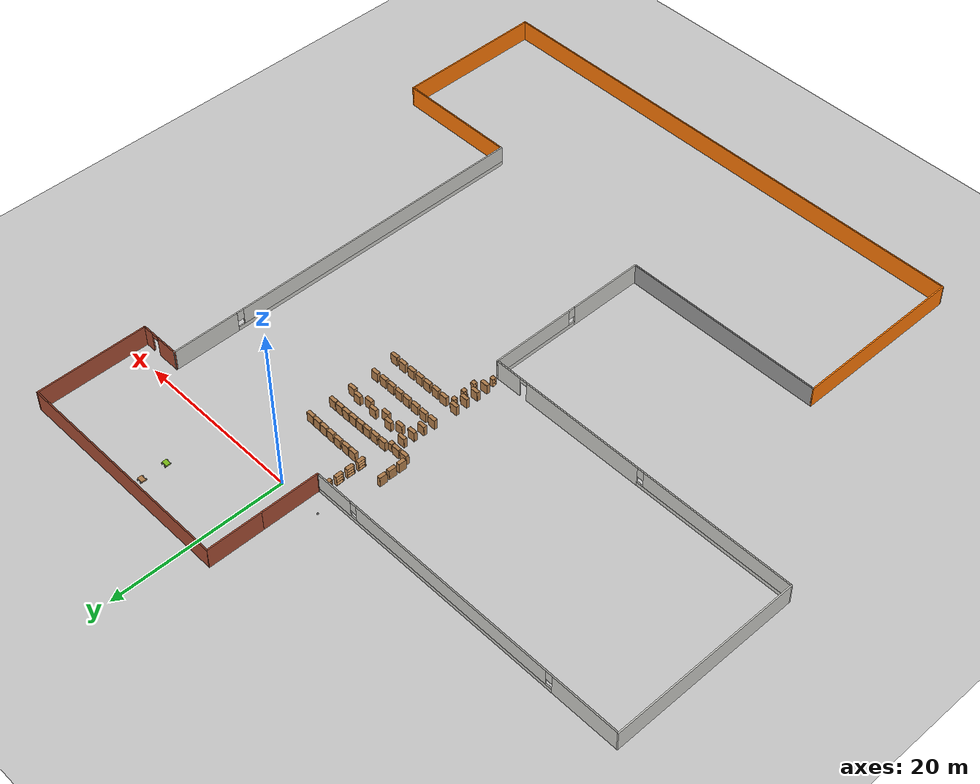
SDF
<sdf version="1.6">
 <world name="default">
  <plugin name="hello" filename="libhello.so"/>
  <light name="sun" type="directional">
   <pose>0 0 10 0 -0 0</pose>
   <diffuse>0.8 0.8 0.8 1</diffuse>
   <specular>0.2 0.2 0.2 1</specular>
   <attenuation>
    <range>1000</range>
    <constant>0.9</constant>
    <linear>0.01</linear>
    <quadratic>0.001</quadratic>
   </attenuation>
   <direction>-0.5 0.1 -0.9</direction>
  </light>
  <model name="ground_plane">
   <static>1</static>
   <link name="link">
    <collision name="collision">
     <geometry><plane><normal>0 0 1</normal><size>100 100</size></plane></geometry>
     <surface>
      <contact><collide_bitmask>65535</collide_bitmask></contact>
      <friction><ode><mu>100</mu><mu2>50</mu2></ode></friction>
     </surface>
    </collision>
    <visual name="visual">
     <cast_shadows>0</cast_shadows>
     <geometry><plane><normal>0 0 1</normal><size>100 100</size></plane></geometry>
     <material>
      <script><uri>file://media/materials/scripts/gazebo.material</uri><name>Gazebo/Grey</name></script>
     </material>
    </visual>
   </link>
  </model>
  <gravity>0 0 -9.8</gravity>
  <magnetic_field>6e-06 2.3e-05 -4.2e-05</magnetic_field>
  <atmosphere type="adiabatic"/>
  <physics name="default_physics" default="0" type="ode">
   <max_step_size>0.001</max_step_size>
   <real_time_factor>1</real_time_factor>
   <real_time_update_rate>1000</real_time_update_rate>
  </physics>
  <scene><ambient>0.4 0.4 0.4 1</ambient><background>0.7 0.7 0.7 1</background><shadows>1</shadows></scene>
  <spherical_coordinates>
   <surface_model>EARTH_WGS84</surface_model>
   <latitude_deg>0</latitude_deg>
   <longitude_deg>0</longitude_deg>
   <elevation>0</elevation>
   <heading_deg>0</heading_deg>
  </spherical_coordinates>
  <model name="Firstfloor">
   <pose>-4.49 -26.435 0 0 -0 0</pose>
   <link name="Wall_0">
    <collision name="Wall_0_Collision">
     <geometry><box><size>6.75 0.15 2.5</size></box></geometry>
     <pose>0 0 1.25 0 -0 0</pose>
    </collision>
    <visual name="Wall_0_Visual">
     <pose>0 0 1.25 0 -0 0</pose>
     <geometry><box><size>6.75 0.15 2.5</size></box></geometry>
     <material>
      <script><uri>file://media/materials/scripts/gazebo.material</uri><name>Gazebo/Bricks</name></script>
      <ambient>1 1 1 1</ambient>
     </material>
     <meta><layer>0</layer></meta>
    </visual>
    <pose>1.45 27.875 0 0 -0 1.5708</pose>
   </link>
   <link name="Wall_1">
    <collision name="Wall_1_Collision">
     <geometry><box><size>6.5 0.15 2.5</size></box></geometry>
     <pose>0 0 1.25 0 -0 0</pose>
    </collision>
    <visual name="Wall_1_Visual">
     <pose>0 0 1.25 0 -0 0</pose>
     <geometry><box><size>6.5 0.15 2.5</size></box></geometry>
     <material>
      <script><uri>file://media/materials/scripts/gazebo.material</uri><name>Gazebo/Bricks</name></script>
      <ambient>1 1 1 1</ambient>
     </material>
     <meta><layer>0</layer></meta>
    </visual>
    <pose>1.45 34.35 0 0 -0 1.5708</pose>
   </link>
   <link name="Wall_10">
    <collision name="Wall_10_Collision">
     <geometry><box><size>24 0.15 2.5</size></box></geometry>
     <pose>0 0 1.25 0 -0 0</pose>
    </collision>
    <visual name="Wall_10_Visual">
     <pose>0 0 1.25 0 -0 0</pose>
     <geometry><box><size>24 0.15 2.5</size></box></geometry>
     <material>
      <script><uri>file://media/materials/scripts/gazebo.material</uri><name>Gazebo/Grey</name></script>
      <ambient>1 1 1 1</ambient>
     </material>
     <meta><layer>0</layer></meta>
    </visual>
    <pose>-11.625 -17.175 0 0 -0 0</pose>
   </link>
   <link name="Wall_11">
    <pose>0.3 -7.375 0 0 -0 1.5708</pose>
    <visual name="Wall_11_Visual_0">
     <pose>-5.38328 0 1.25 0 -0 0</pose>
     <geometry><box><size>8.98345 0.15 2.5</size></box></geometry>
     <material>
      <script><uri>file://media/materials/scripts/gazebo.material</uri><name>Gazebo/CeilingTiled</name></script>
      <ambient>1 1 1 1</ambient>
     </material>
     <meta><layer>0</layer></meta>
    </visual>
    <collision name="Wall_11_Collision_0">
     <geometry><box><size>8.98345 0.15 2.5</size></box></geometry>
     <pose>-5.38328 0 1.25 0 -0 0</pose>
    </collision>
    <visual name="Wall_11_Visual_1">
     <pose>4.49172 0 0.25 0 -0 0</pose>
     <geometry><box><size>10.7666 0.15 0.5</size></box></geometry>
     <material>
      <script><uri>file://media/materials/scripts/gazebo.material</uri><name>Gazebo/CeilingTiled</name></script>
      <ambient>1 1 1 1</ambient>
     </material>
     <meta><layer>0</layer></meta>
    </visual>
    <collision name="Wall_11_Collision_1">
     <geometry><box><size>10.7666 0.15 0.5</size></box></geometry>
     <pose>4.49172 0 0.25 0 -0 0</pose>
    </collision>
    <visual name="Wall_11_Visual_2">
     <pose>4.89173 0 1.5 0 -0 0</pose>
     <geometry><box><size>9.96655 0.15 2</size></box></geometry>
     <material>
      <script><uri>file://media/materials/scripts/gazebo.material</uri><name>Gazebo/CeilingTiled</name></script>
      <ambient>1 1 1 1</ambient>
     </material>
     <meta><layer>0</layer></meta>
    </visual>
    <collision name="Wall_11_Collision_2">
     <geometry><box><size>9.96655 0.15 2</size></box></geometry>
     <pose>4.89173 0 1.5 0 -0 0</pose>
    </collision>
    <visual name="Wall_11_Visual_3">
     <pose>-0.49155 0 1.9 0 -0 0</pose>
     <geometry><box><size>0.8 0.15 1.2</size></box></geometry>
     <material>
      <script><uri>file://media/materials/scripts/gazebo.material</uri><name>Gazebo/CeilingTiled</name></script>
      <ambient>1 1 1 1</ambient>
     </material>
     <meta><layer>0</layer></meta>
    </visual>
    <collision name="Wall_11_Collision_3">
     <geometry><box><size>0.8 0.15 1.2</size></box></geometry>
     <pose>-0.49155 0 1.9 0 -0 0</pose>
    </collision>
   </link>
   <link name="Wall_12">
    <pose>-18.625 2.425 0 0 -0 3.14159</pose>
    <visual name="Wall_12_Visual_0">
     <pose>-17.3553 0 1.25 0 -0 0</pose>
     <geometry><box><size>3.28937 0.15 2.5</size></box></geometry>
     <material>
      <script><uri>file://media/materials/scripts/gazebo.material</uri><name>Gazebo/CeilingTiled</name></script>
      <ambient>1 1 1 1</ambient>
     </material>
     <meta><layer>0</layer></meta>
    </visual>
    <collision name="Wall_12_Collision_0">
     <geometry><box><size>3.28937 0.15 2.5</size></box></geometry>
     <pose>-17.3553 0 1.25 0 -0 0</pose>
    </collision>
    <visual name="Wall_12_Visual_1">
     <pose>-7.35452 0 1.25 0 -0 0</pose>
     <geometry><box><size>14.9122 0.15 2.5</size></box></geometry>
     <material>
      <script><uri>file://media/materials/scripts/gazebo.material</uri><name>Gazebo/CeilingTiled</name></script>
      <ambient>1 1 1 1</ambient>
     </material>
     <meta><layer>0</layer></meta>
    </visual>
    <collision name="Wall_12_Collision_1">
     <geometry><box><size>14.9122 0.15 2.5</size></box></geometry>
     <pose>-7.35452 0 1.25 0 -0 0</pose>
    </collision>
    <visual name="Wall_12_Visual_2">
     <pose>9.5508 0 0.25 0 -0 0</pose>
     <geometry><box><size>18.8984 0.15 0.5</size></box></geometry>
     <material>
      <script><uri>file://media/materials/scripts/gazebo.material</uri><name>Gazebo/CeilingTiled</name></script>
      <ambient>1 1 1 1</ambient>
     </material>
     <meta><layer>0</layer></meta>
    </visual>
    <collision name="Wall_12_Collision_2">
     <geometry><box><size>18.8984 0.15 0.5</size></box></geometry>
     <pose>9.5508 0 0.25 0 -0 0</pose>
    </collision>
    <visual name="Wall_12_Visual_3">
     <pose>9.95079 0 1.5 0 -0 0</pose>
     <geometry><box><size>18.0984 0.15 2</size></box></geometry>
     <material>
      <script><uri>file://media/materials/scripts/gazebo.material</uri><name>Gazebo/CeilingTiled</name></script>
      <ambient>1 1 1 1</ambient>
     </material>
     <meta><layer>0</layer></meta>
    </visual>
    <collision name="Wall_12_Collision_3">
     <geometry><box><size>18.0984 0.15 2</size></box></geometry>
     <pose>9.95079 0 1.5 0 -0 0</pose>
    </collision>
    <visual name="Wall_12_Visual_4">
     <pose>0.501591 0 1.9 0 -0 0</pose>
     <geometry><box><size>0.8 0.15 1.2</size></box></geometry>
     <material>
      <script><uri>file://media/materials/scripts/gazebo.material</uri><name>Gazebo/CeilingTiled</name></script>
      <ambient>1 1 1 1</ambient>
     </material>
     <meta><layer>0</layer></meta>
    </visual>
    <collision name="Wall_12_Collision_4">
     <geometry><box><size>0.8 0.15 1.2</size></box></geometry>
     <pose>0.501591 0 1.9 0 -0 0</pose>
    </collision>
    <visual name="Wall_12_Visual_5">
     <pose>-15.2606 0 2.25 0 -0 0</pose>
     <geometry><box><size>0.9 0.15 0.5</size></box></geometry>
     <material>
      <script><uri>file://media/materials/scripts/gazebo.material</uri><name>Gazebo/CeilingTiled</name></script>
      <ambient>1 1 1 1</ambient>
     </material>
     <meta><layer>0</layer></meta>
    </visual>
    <collision name="Wall_12_Collision_5">
     <geometry><box><size>0.9 0.15 0.5</size></box></geometry>
     <pose>-15.2606 0 2.25 0 -0 0</pose>
    </collision>
   </link>
   <link name="Wall_13">
    <collision name="Wall_13_Collision">
     <geometry><box><size>22.25 0.15 2.5</size></box></geometry>
     <pose>0 0 1.25 0 -0 0</pose>
    </collision>
    <visual name="Wall_13_Visual">
     <pose>0 0 1.25 0 -0 0</pose>
     <geometry><box><size>22.25 0.15 2.5</size></box></geometry>
     <material>
      <script><uri>file://media/materials/scripts/gazebo.material</uri><name>Gazebo/CeilingTiled</name></script>
      <ambient>1 1 1 1</ambient>
     </material>
     <meta><layer>0</layer></meta>
    </visual>
    <pose>-37.55 13.475 0 0 -0 1.5708</pose>
   </link>
   <link name="Wall_14">
    <pose>-18.125 24.525 0 0 -0 0</pose>
    <visual name="Wall_14_Visual_0">
     <pose>-15.5453 0 1.25 0 -0 0</pose>
     <geometry><box><size>7.90934 0.15 2.5</size></box></geometry>
     <material>
      <script><uri>file://media/materials/scripts/gazebo.material</uri><name>Gazebo/CeilingTiled</name></script>
      <ambient>1 1 1 1</ambient>
     </material>
     <meta><layer>0</layer></meta>
    </visual>
    <collision name="Wall_14_Collision_0">
     <geometry><box><size>7.90934 0.15 2.5</size></box></geometry>
     <pose>-15.5453 0 1.25 0 -0 0</pose>
    </collision>
    <visual name="Wall_14_Visual_1">
     <pose>3.95467 0 0.25 0 -0 0</pose>
     <geometry><box><size>31.0907 0.15 0.5</size></box></geometry>
     <material>
      <script><uri>file://media/materials/scripts/gazebo.material</uri><name>Gazebo/CeilingTiled</name></script>
      <ambient>1 1 1 1</ambient>
     </material>
     <meta><layer>0</layer></meta>
    </visual>
    <collision name="Wall_14_Collision_1">
     <geometry><box><size>31.0907 0.15 0.5</size></box></geometry>
     <pose>3.95467 0 0.25 0 -0 0</pose>
    </collision>
    <visual name="Wall_14_Visual_2">
     <pose>1.64004 0 1.5 0 -0 0</pose>
     <geometry><box><size>24.8614 0.15 2</size></box></geometry>
     <material>
      <script><uri>file://media/materials/scripts/gazebo.material</uri><name>Gazebo/CeilingTiled</name></script>
      <ambient>1 1 1 1</ambient>
     </material>
     <meta><layer>0</layer></meta>
    </visual>
    <collision name="Wall_14_Collision_2">
     <geometry><box><size>24.8614 0.15 2</size></box></geometry>
     <pose>1.64004 0 1.5 0 -0 0</pose>
    </collision>
    <visual name="Wall_14_Visual_3">
     <pose>17.1854 0 1.5 0 -0 0</pose>
     <geometry><box><size>4.62927 0.15 2</size></box></geometry>
     <material>
      <script><uri>file://media/materials/scripts/gazebo.material</uri><name>Gazebo/CeilingTiled</name></script>
      <ambient>1 1 1 1</ambient>
     </material>
     <meta><layer>0</layer></meta>
    </visual>
    <collision name="Wall_14_Collision_3">
     <geometry><box><size>4.62927 0.15 2</size></box></geometry>
     <pose>17.1854 0 1.5 0 -0 0</pose>
    </collision>
    <visual name="Wall_14_Visual_4">
     <pose>-11.1907 0 1.9 0 -0 0</pose>
     <geometry><box><size>0.8 0.15 1.2</size></box></geometry>
     <material>
      <script><uri>file://media/materials/scripts/gazebo.material</uri><name>Gazebo/CeilingTiled</name></script>
      <ambient>1 1 1 1</ambient>
     </material>
     <meta><layer>0</layer></meta>
    </visual>
    <collision name="Wall_14_Collision_4">
     <geometry><box><size>0.8 0.15 1.2</size></box></geometry>
     <pose>-11.1907 0 1.9 0 -0 0</pose>
    </collision>
    <visual name="Wall_14_Visual_5">
     <pose>14.4707 0 1.9 0 -0 0</pose>
     <geometry><box><size>0.8 0.15 1.2</size></box></geometry>
     <material>
      <script><uri>file://media/materials/scripts/gazebo.material</uri><name>Gazebo/CeilingTiled</name></script>
      <ambient>1 1 1 1</ambient>
     </material>
     <meta><layer>0</layer></meta>
    </visual>
    <collision name="Wall_14_Collision_5">
     <geometry><box><size>0.8 0.15 1.2</size></box></geometry>
     <pose>14.4707 0 1.9 0 -0 0</pose>
    </collision>
   </link>
   <link name="Wall_16">
    <collision name="Wall_16_Collision">
     <geometry><box><size>0.308114 0.15 2.5</size></box></geometry>
     <pose>0 0 1.25 0 -0 0</pose>
    </collision>
    <visual name="Wall_16_Visual">
     <pose>0 0 1.25 0 -0 0</pose>
     <geometry><box><size>0.308114 0.15 2.5</size></box></geometry>
     <material>
      <script><uri>file://media/materials/scripts/gazebo.material</uri><name>Gazebo/Bricks</name></script>
      <ambient>1 1 1 1</ambient>
     </material>
     <meta><layer>0</layer></meta>
    </visual>
    <pose>1.375 24.55 0 0 -0 0.321751</pose>
   </link>
   <link name="Wall_2">
    <collision name="Wall_2_Collision">
     <geometry><box><size>26.75 0.15 2.5</size></box></geometry>
     <pose>0 0 1.25 0 -0 0</pose>
    </collision>
    <visual name="Wall_2_Visual">
     <pose>0 0 1.25 0 -0 0</pose>
     <geometry><box><size>26.75 0.15 2.5</size></box></geometry>
     <material>
      <script><uri>file://media/materials/scripts/gazebo.material</uri><name>Gazebo/Bricks</name></script>
      <ambient>1 1 1 1</ambient>
     </material>
     <meta><layer>0</layer></meta>
    </visual>
    <pose>14.75 37.525 0 0 -0 0</pose>
   </link>
   <link name="Wall_3">
    <collision name="Wall_3_Collision">
     <geometry><box><size>13 0.15 2.5</size></box></geometry>
     <pose>0 0 1.25 0 -0 0</pose>
    </collision>
    <visual name="Wall_3_Visual">
     <pose>0 0 1.25 0 -0 0</pose>
     <geometry><box><size>13 0.15 2.5</size></box></geometry>
     <material>
      <script><uri>file://media/materials/scripts/gazebo.material</uri><name>Gazebo/Bricks</name></script>
      <ambient>1 1 1 1</ambient>
     </material>
     <meta><layer>0</layer></meta>
    </visual>
    <pose>28.05 31.1 0 0 0 -1.5708</pose>
   </link>
   <link name="Wall_4">
    <pose>25.625 24.675 0 0 -0 3.14159</pose>
    <visual name="Wall_4_Visual_0">
     <pose>-1.81649 0 1.25 0 -0 0</pose>
     <geometry><box><size>1.36703 0.15 2.5</size></box></geometry>
     <material>
      <script><uri>file://media/materials/scripts/gazebo.material</uri><name>Gazebo/Bricks</name></script>
      <ambient>1 1 1 1</ambient>
     </material>
     <meta><layer>0</layer></meta>
    </visual>
    <collision name="Wall_4_Collision_0">
     <geometry><box><size>1.36703 0.15 2.5</size></box></geometry>
     <pose>-1.81649 0 1.25 0 -0 0</pose>
    </collision>
    <visual name="Wall_4_Visual_1">
     <pose>1.13351 0 1.25 0 -0 0</pose>
     <geometry><box><size>2.73297 0.15 2.5</size></box></geometry>
     <material>
      <script><uri>file://media/materials/scripts/gazebo.material</uri><name>Gazebo/Bricks</name></script>
      <ambient>1 1 1 1</ambient>
     </material>
     <meta><layer>0</layer></meta>
    </visual>
    <collision name="Wall_4_Collision_1">
     <geometry><box><size>2.73297 0.15 2.5</size></box></geometry>
     <pose>1.13351 0 1.25 0 -0 0</pose>
    </collision>
    <visual name="Wall_4_Visual_2">
     <pose>-0.682972 0 2.25 0 -0 0</pose>
     <geometry><box><size>0.9 0.15 0.5</size></box></geometry>
     <material>
      <script><uri>file://media/materials/scripts/gazebo.material</uri><name>Gazebo/Bricks</name></script>
      <ambient>1 1 1 1</ambient>
     </material>
     <meta><layer>0</layer></meta>
    </visual>
    <collision name="Wall_4_Collision_2">
     <geometry><box><size>0.9 0.15 0.5</size></box></geometry>
     <pose>-0.682972 0 2.25 0 -0 0</pose>
    </collision>
   </link>
   <link name="Wall_5">
    <pose>23.2 2.375 0 0 0 -1.5708</pose>
    <visual name="Wall_5_Visual_0">
     <pose>-18.4256 0 1.25 0 -0 0</pose>
     <geometry><box><size>7.89886 0.15 2.5</size></box></geometry>
     <material>
      <script><uri>file://media/materials/scripts/gazebo.material</uri><name>Gazebo/CeilingTiled</name></script>
      <ambient>1 1 1 1</ambient>
     </material>
     <meta><layer>0</layer></meta>
    </visual>
    <collision name="Wall_5_Collision_0">
     <geometry><box><size>7.89886 0.15 2.5</size></box></geometry>
     <pose>-18.4256 0 1.25 0 -0 0</pose>
    </collision>
    <visual name="Wall_5_Visual_1">
     <pose>3.94943 0 0.25 0 -0 0</pose>
     <geometry><box><size>36.8511 0.15 0.5</size></box></geometry>
     <material>
      <script><uri>file://media/materials/scripts/gazebo.material</uri><name>Gazebo/CeilingTiled</name></script>
      <ambient>1 1 1 1</ambient>
     </material>
     <meta><layer>0</layer></meta>
    </visual>
    <collision name="Wall_5_Collision_1">
     <geometry><box><size>36.8511 0.15 0.5</size></box></geometry>
     <pose>3.94943 0 0.25 0 -0 0</pose>
    </collision>
    <visual name="Wall_5_Visual_2">
     <pose>4.34943 0 1.5 0 -0 0</pose>
     <geometry><box><size>36.0511 0.15 2</size></box></geometry>
     <material>
      <script><uri>file://media/materials/scripts/gazebo.material</uri><name>Gazebo/CeilingTiled</name></script>
      <ambient>1 1 1 1</ambient>
     </material>
     <meta><layer>0</layer></meta>
    </visual>
    <collision name="Wall_5_Collision_2">
     <geometry><box><size>36.0511 0.15 2</size></box></geometry>
     <pose>4.34943 0 1.5 0 -0 0</pose>
    </collision>
    <visual name="Wall_5_Visual_3">
     <pose>-14.0761 0 1.9 0 -0 0</pose>
     <geometry><box><size>0.8 0.15 1.2</size></box></geometry>
     <material>
      <script><uri>file://media/materials/scripts/gazebo.material</uri><name>Gazebo/CeilingTiled</name></script>
      <ambient>1 1 1 1</ambient>
     </material>
     <meta><layer>0</layer></meta>
    </visual>
    <collision name="Wall_5_Collision_3">
     <geometry><box><size>0.8 0.15 1.2</size></box></geometry>
     <pose>-14.0761 0 1.9 0 -0 0</pose>
    </collision>
   </link>
   <link name="Wall_6">
    <collision name="Wall_6_Collision">
     <geometry><box><size>14.5 0.15 2.5</size></box></geometry>
     <pose>0 0 1.25 0 -0 0</pose>
    </collision>
    <visual name="Wall_6_Visual">
     <pose>0 0 1.25 0 -0 0</pose>
     <geometry><box><size>14.5 0.15 2.5</size></box></geometry>
     <material>
      <script><uri>file://media/materials/scripts/gazebo.material</uri><name>Gazebo/Grey</name></script>
      <ambient>0.996078 0.47451 0.0196078 1</ambient>
     </material>
     <meta><layer>0</layer></meta>
    </visual>
    <pose>30.375 -19.925 0 0 -0 0</pose>
   </link>
   <link name="Wall_7">
    <collision name="Wall_7_Collision">
     <geometry><box><size>17.75 0.15 2.5</size></box></geometry>
     <pose>0 0 1.25 0 -0 0</pose>
    </collision>
    <visual name="Wall_7_Visual">
     <pose>0 0 1.25 0 -0 0</pose>
     <geometry><box><size>17.75 0.15 2.5</size></box></geometry>
     <material>
      <script><uri>file://media/materials/scripts/gazebo.material</uri><name>Gazebo/Grey</name></script>
      <ambient>0.996078 0.47451 0.0196078 1</ambient>
     </material>
     <meta><layer>0</layer></meta>
    </visual>
    <pose>37.55 -28.725 0 0 0 -1.5708</pose>
   </link>
   <link name="Wall_8">
    <collision name="Wall_8_Collision">
     <geometry><box><size>61.25 0.15 2.5</size></box></geometry>
     <pose>0 0 1.25 0 -0 0</pose>
    </collision>
    <visual name="Wall_8_Visual">
     <pose>0 0 1.25 0 -0 0</pose>
     <geometry><box><size>61.25 0.15 2.5</size></box></geometry>
     <material>
      <script><uri>file://media/materials/scripts/gazebo.material</uri><name>Gazebo/Grey</name></script>
      <ambient>0.996078 0.47451 0.0196078 1</ambient>
     </material>
     <meta><layer>0</layer></meta>
    </visual>
    <pose>7 -37.525 0 0 -0 3.14159</pose>
   </link>
   <link name="Wall_9">
    <collision name="Wall_9_Collision">
     <geometry><box><size>20.5 0.15 2.5</size></box></geometry>
     <pose>0 0 1.25 0 -0 0</pose>
    </collision>
    <visual name="Wall_9_Visual">
     <pose>0 0 1.25 0 -0 0</pose>
     <geometry><box><size>20.5 0.15 2.5</size></box></geometry>
     <material>
      <script><uri>file://media/materials/scripts/gazebo.material</uri><name>Gazebo/Grey</name></script>
      <ambient>0.996078 0.47451 0.0196078 1</ambient>
     </material>
     <meta><layer>0</layer></meta>
    </visual>
    <pose>-23.55 -27.35 0 0 -0 1.5708</pose>
   </link>
   <static>1</static>
  </model>
  <model name="cabinet">
   <static>1</static>
   <link name="cabinet_bottom_plate">
    <inertial>
     <pose>0 0 -1 0 -0 0</pose>
     <inertia><ixx>2.05</ixx><ixy>0</ixy><ixz>0</ixz><iyy>2.05</iyy><iyz>0</iyz><izz>2.05</izz></inertia>
     <mass>25</mass>
    </inertial>
    <collision name="cabinet_bottom_plate_geom">
     <pose>0 0 0.01 0 -0 0</pose>
     <geometry><box><size>0.45 0.45 0.02</size></box></geometry>
    </collision>
    <visual name="cabinet_bottom_plate_geom_visual">
     <pose>0 0 0.01 0 -0 0</pose>
     <geometry><box><size>0.45 0.45 0.02</size></box></geometry>
     <material>
      <script><uri>file://media/materials/scripts/gazebo.material</uri><name>Gazebo/Wood</name></script>
     </material>
    </visual>
    <collision name="cabinet_bottom_plate_geom_cabinet_back_plate">
     <pose>0.235 0 0.51 0 -0 0</pose>
     <geometry><box><size>0.02 0.45 1.02</size></box></geometry>
    </collision>
    <visual name="cabinet_bottom_plate_geom_cabinet_back_plate_visual">
     <pose>0.235 0 0.51 0 -0 0</pose>
     <geometry><box><size>0.02 0.45 1.02</size></box></geometry>
     <material>
      <script><uri>file://media/materials/scripts/gazebo.material</uri><name>Gazebo/Wood</name></script>
     </material>
    </visual>
    <collision name="cabinet_bottom_plate_geom_cabinet_left_plate">
     <pose>0 0.235 0.51 0 -0 0</pose>
     <geometry><box><size>0.45 0.02 1.02</size></box></geometry>
    </collision>
    <visual name="cabinet_bottom_plate_geom_cabinet_left_plate_visual">
     <pose>0 0.235 0.51 0 -0 0</pose>
     <geometry><box><size>0.45 0.02 1.02</size></box></geometry>
     <material>
      <script><uri>file://media/materials/scripts/gazebo.material</uri><name>Gazebo/Wood</name></script>
     </material>
    </visual>
    <collision name="cabinet_bottom_plate_geom_cabinet_middle_plate">
     <pose>0 0 0.51 0 -0 0</pose>
     <geometry><box><size>0.45 0.45 0.02</size></box></geometry>
    </collision>
    <visual name="cabinet_bottom_plate_geom_cabinet_middle_plate_visual">
     <pose>0 0 0.51 0 -0 0</pose>
     <geometry><box><size>0.45 0.45 0.02</size></box></geometry>
     <material>
      <script><uri>file://media/materials/scripts/gazebo.material</uri><name>Gazebo/Wood</name></script>
     </material>
    </visual>
    <collision name="cabinet_bottom_plate_geom_cabinet_right_plate">
     <pose>0 -0.235 0.51 0 -0 0</pose>
     <geometry><box><size>0.45 0.02 1.02</size></box></geometry>
    </collision>
    <visual name="cabinet_bottom_plate_geom_cabinet_right_plate_visual">
     <pose>0 -0.235 0.51 0 -0 0</pose>
     <geometry><box><size>0.45 0.02 1.02</size></box></geometry>
     <material>
      <script><uri>file://media/materials/scripts/gazebo.material</uri><name>Gazebo/Wood</name></script>
     </material>
    </visual>
    <collision name="cabinet_bottom_plate_geom_cabinet_top_plate">
     <pose>0 0 1.01 0 -0 0</pose>
     <geometry><box><size>0.45 0.45 0.02</size></box></geometry>
    </collision>
    <visual name="cabinet_bottom_plate_geom_cabinet_top_plate_visual">
     <pose>0 0 1.01 0 -0 0</pose>
     <geometry><box><size>0.45 0.45 0.02</size></box></geometry>
     <material>
      <script><uri>file://media/materials/scripts/gazebo.material</uri><name>Gazebo/Wood</name></script>
     </material>
    </visual>
   </link>
   <pose>-2.66725 -1.57685 0 0 -0 3.13621</pose>
  </model>
  <model name="cabinet_0">
   <static>1</static>
   <link name="cabinet_bottom_plate">
    <inertial>
     <pose>0 0 -1 0 -0 0</pose>
     <inertia><ixx>2.05</ixx><ixy>0</ixy><ixz>0</ixz><iyy>2.05</iyy><iyz>0</iyz><izz>2.05</izz></inertia>
     <mass>25</mass>
    </inertial>
    <collision name="cabinet_bottom_plate_geom">
     <pose>0 0 0.01 0 -0 0</pose>
     <geometry><box><size>0.45 0.45 0.02</size></box></geometry>
    </collision>
    <visual name="cabinet_bottom_plate_geom_visual">
     <pose>0 0 0.01 0 -0 0</pose>
     <geometry><box><size>0.45 0.45 0.02</size></box></geometry>
     <material>
      <script><uri>file://media/materials/scripts/gazebo.material</uri><name>Gazebo/Wood</name></script>
     </material>
    </visual>
    <collision name="cabinet_bottom_plate_geom_cabinet_back_plate">
     <pose>0.235 0 0.51 0 -0 0</pose>
     <geometry><box><size>0.02 0.45 1.02</size></box></geometry>
    </collision>
    <visual name="cabinet_bottom_plate_geom_cabinet_back_plate_visual">
     <pose>0.235 0 0.51 0 -0 0</pose>
     <geometry><box><size>0.02 0.45 1.02</size></box></geometry>
     <material>
      <script><uri>file://media/materials/scripts/gazebo.material</uri><name>Gazebo/Wood</name></script>
     </material>
    </visual>
    <collision name="cabinet_bottom_plate_geom_cabinet_left_plate">
     <pose>0 0.235 0.51 0 -0 0</pose>
     <geometry><box><size>0.45 0.02 1.02</size></box></geometry>
    </collision>
    <visual name="cabinet_bottom_plate_geom_cabinet_left_plate_visual">
     <pose>0 0.235 0.51 0 -0 0</pose>
     <geometry><box><size>0.45 0.02 1.02</size></box></geometry>
     <material>
      <script><uri>file://media/materials/scripts/gazebo.material</uri><name>Gazebo/Wood</name></script>
     </material>
    </visual>
    <collision name="cabinet_bottom_plate_geom_cabinet_middle_plate">
     <pose>0 0 0.51 0 -0 0</pose>
     <geometry><box><size>0.45 0.45 0.02</size></box></geometry>
    </collision>
    <visual name="cabinet_bottom_plate_geom_cabinet_middle_plate_visual">
     <pose>0 0 0.51 0 -0 0</pose>
     <geometry><box><size>0.45 0.45 0.02</size></box></geometry>
     <material>
      <script><uri>file://media/materials/scripts/gazebo.material</uri><name>Gazebo/Wood</name></script>
     </material>
    </visual>
    <collision name="cabinet_bottom_plate_geom_cabinet_right_plate">
     <pose>0 -0.235 0.51 0 -0 0</pose>
     <geometry><box><size>0.45 0.02 1.02</size></box></geometry>
    </collision>
    <visual name="cabinet_bottom_plate_geom_cabinet_right_plate_visual">
     <pose>0 -0.235 0.51 0 -0 0</pose>
     <geometry><box><size>0.45 0.02 1.02</size></box></geometry>
     <material>
      <script><uri>file://media/materials/scripts/gazebo.material</uri><name>Gazebo/Wood</name></script>
     </material>
    </visual>
    <collision name="cabinet_bottom_plate_geom_cabinet_top_plate">
     <pose>0 0 1.01 0 -0 0</pose>
     <geometry><box><size>0.45 0.45 0.02</size></box></geometry>
    </collision>
    <visual name="cabinet_bottom_plate_geom_cabinet_top_plate_visual">
     <pose>0 0 1.01 0 -0 0</pose>
     <geometry><box><size>0.45 0.45 0.02</size></box></geometry>
     <material>
      <script><uri>file://media/materials/scripts/gazebo.material</uri><name>Gazebo/Wood</name></script>
     </material>
    </visual>
   </link>
   <pose>-2.71114 -0.407385 0 0 0 -3.12251</pose>
  </model>
  <model name="bookshelf">
   <static>1</static>
   <link name="link">
    <inertial><mass>1</mass></inertial>
    <collision name="back">
     <pose>0 0.005 0.6 0 -0 0</pose>
     <geometry><box><size>0.9 0.01 1.2</size></box></geometry>
    </collision>
    <visual name="visual1">
     <pose>0 0.005 0.6 0 -0 0</pose>
     <geometry><box><size>0.9 0.01 1.2</size></box></geometry>
     <material>
      <script><uri>file://media/materials/scripts/gazebo.material</uri><name>Gazebo/Wood</name></script>
     </material>
    </visual>
    <collision name="left_side">
     <pose>0.45 -0.195 0.6 0 -0 0</pose>
     <geometry><box><size>0.02 0.4 1.2</size></box></geometry>
    </collision>
    <visual name="visual2">
     <pose>0.45 -0.195 0.6 0 -0 0</pose>
     <geometry><box><size>0.02 0.4 1.2</size></box></geometry>
     <material>
      <script><uri>file://media/materials/scripts/gazebo.material</uri><name>Gazebo/Wood</name></script>
     </material>
    </visual>
    <collision name="right_side">
     <pose>-0.45 -0.195 0.6 0 -0 0</pose>
     <geometry><box><size>0.02 0.4 1.2</size></box></geometry>
    </collision>
    <visual name="visual3">
     <pose>-0.45 -0.195 0.6 0 -0 0</pose>
     <geometry><box><size>0.02 0.4 1.2</size></box></geometry>
     <material>
      <script><uri>file://media/materials/scripts/gazebo.material</uri><name>Gazebo/Wood</name></script>
     </material>
    </visual>
    <collision name="bottom">
     <pose>0 -0.195 0.03 0 -0 0</pose>
     <geometry><box><size>0.88 0.4 0.06</size></box></geometry>
    </collision>
    <visual name="visual4">
     <pose>0 -0.195 0.03 0 -0 0</pose>
     <geometry><box><size>0.88 0.4 0.06</size></box></geometry>
     <material>
      <script><uri>file://media/materials/scripts/gazebo.material</uri><name>Gazebo/Wood</name></script>
     </material>
    </visual>
    <collision name="top">
     <pose>0 -0.195 1.19 0 -0 0</pose>
     <geometry><box><size>0.88 0.4 0.02</size></box></geometry>
    </collision>
    <visual name="visual5">
     <pose>0 -0.195 1.19 0 -0 0</pose>
     <geometry><box><size>0.88 0.4 0.02</size></box></geometry>
     <material>
      <script><uri>file://media/materials/scripts/gazebo.material</uri><name>Gazebo/Wood</name></script>
     </material>
    </visual>
    <collision name="low_shelf">
     <pose>0 -0.195 0.43 0 -0 0</pose>
     <geometry><box><size>0.88 0.4 0.02</size></box></geometry>
    </collision>
    <visual name="visual6">
     <pose>0 -0.195 0.43 0 -0 0</pose>
     <geometry><box><size>0.88 0.4 0.02</size></box></geometry>
     <material>
      <script><uri>file://media/materials/scripts/gazebo.material</uri><name>Gazebo/Wood</name></script>
     </material>
    </visual>
    <collision name="high_shelf">
     <pose>0 -0.195 0.8 0 -0 0</pose>
     <geometry><box><size>0.88 0.4 0.02</size></box></geometry>
    </collision>
    <visual name="visual7">
     <pose>0 -0.195 0.8 0 -0 0</pose>
     <geometry><box><size>0.88 0.4 0.02</size></box></geometry>
     <material>
      <script><uri>file://media/materials/scripts/gazebo.material</uri><name>Gazebo/Wood</name></script>
     </material>
    </visual>
   </link>
   <pose>-1.04196 -9.56477 0 0 -0 0</pose>
  </model>
  <model name="bookshelf_clone">
   <static>1</static>
   <link name="link">
    <inertial><mass>1</mass></inertial>
    <collision name="back">
     <pose>0 0.005 0.6 0 -0 0</pose>
     <geometry><box><size>0.9 0.01 1.2</size></box></geometry>
    </collision>
    <visual name="visual1">
     <pose>0 0.005 0.6 0 -0 0</pose>
     <geometry><box><size>0.9 0.01 1.2</size></box></geometry>
     <material>
      <script><uri>file://media/materials/scripts/gazebo.material</uri><name>Gazebo/Wood</name></script>
     </material>
    </visual>
    <collision name="left_side">
     <pose>0.45 -0.195 0.6 0 -0 0</pose>
     <geometry><box><size>0.02 0.4 1.2</size></box></geometry>
    </collision>
    <visual name="visual2">
     <pose>0.45 -0.195 0.6 0 -0 0</pose>
     <geometry><box><size>0.02 0.4 1.2</size></box></geometry>
     <material>
      <script><uri>file://media/materials/scripts/gazebo.material</uri><name>Gazebo/Wood</name></script>
     </material>
    </visual>
    <collision name="right_side">
     <pose>-0.45 -0.195 0.6 0 -0 0</pose>
     <geometry><box><size>0.02 0.4 1.2</size></box></geometry>
    </collision>
    <visual name="visual3">
     <pose>-0.45 -0.195 0.6 0 -0 0</pose>
     <geometry><box><size>0.02 0.4 1.2</size></box></geometry>
     <material>
      <script><uri>file://media/materials/scripts/gazebo.material</uri><name>Gazebo/Wood</name></script>
     </material>
    </visual>
    <collision name="bottom">
     <pose>0 -0.195 0.03 0 -0 0</pose>
     <geometry><box><size>0.88 0.4 0.06</size></box></geometry>
    </collision>
    <visual name="visual4">
     <pose>0 -0.195 0.03 0 -0 0</pose>
     <geometry><box><size>0.88 0.4 0.06</size></box></geometry>
     <material>
      <script><uri>file://media/materials/scripts/gazebo.material</uri><name>Gazebo/Wood</name></script>
     </material>
    </visual>
    <collision name="top">
     <pose>0 -0.195 1.19 0 -0 0</pose>
     <geometry><box><size>0.88 0.4 0.02</size></box></geometry>
    </collision>
    <visual name="visual5">
     <pose>0 -0.195 1.19 0 -0 0</pose>
     <geometry><box><size>0.88 0.4 0.02</size></box></geometry>
     <material>
      <script><uri>file://media/materials/scripts/gazebo.material</uri><name>Gazebo/Wood</name></script>
     </material>
    </visual>
    <collision name="low_shelf">
     <pose>0 -0.195 0.43 0 -0 0</pose>
     <geometry><box><size>0.88 0.4 0.02</size></box></geometry>
    </collision>
    <visual name="visual6">
     <pose>0 -0.195 0.43 0 -0 0</pose>
     <geometry><box><size>0.88 0.4 0.02</size></box></geometry>
     <material>
      <script><uri>file://media/materials/scripts/gazebo.material</uri><name>Gazebo/Wood</name></script>
     </material>
    </visual>
    <collision name="high_shelf">
     <pose>0 -0.195 0.8 0 -0 0</pose>
     <geometry><box><size>0.88 0.4 0.02</size></box></geometry>
    </collision>
    <visual name="visual7">
     <pose>0 -0.195 0.8 0 -0 0</pose>
     <geometry><box><size>0.88 0.4 0.02</size></box></geometry>
     <material>
      <script><uri>file://media/materials/scripts/gazebo.material</uri><name>Gazebo/Wood</name></script>
     </material>
    </visual>
   </link>
   <pose>-0.018383 -9.55291 0 0 -0 0</pose>
  </model>
  <model name="bookshelf_clone_0">
   <static>1</static>
   <link name="link">
    <inertial><mass>1</mass></inertial>
    <collision name="back">
     <pose>0 0.005 0.6 0 -0 0</pose>
     <geometry><box><size>0.9 0.01 1.2</size></box></geometry>
    </collision>
    <visual name="visual1">
     <pose>0 0.005 0.6 0 -0 0</pose>
     <geometry><box><size>0.9 0.01 1.2</size></box></geometry>
     <material>
      <script><uri>file://media/materials/scripts/gazebo.material</uri><name>Gazebo/Wood</name></script>
     </material>
    </visual>
    <collision name="left_side">
     <pose>0.45 -0.195 0.6 0 -0 0</pose>
     <geometry><box><size>0.02 0.4 1.2</size></box></geometry>
    </collision>
    <visual name="visual2">
     <pose>0.45 -0.195 0.6 0 -0 0</pose>
     <geometry><box><size>0.02 0.4 1.2</size></box></geometry>
     <material>
      <script><uri>file://media/materials/scripts/gazebo.material</uri><name>Gazebo/Wood</name></script>
     </material>
    </visual>
    <collision name="right_side">
     <pose>-0.45 -0.195 0.6 0 -0 0</pose>
     <geometry><box><size>0.02 0.4 1.2</size></box></geometry>
    </collision>
    <visual name="visual3">
     <pose>-0.45 -0.195 0.6 0 -0 0</pose>
     <geometry><box><size>0.02 0.4 1.2</size></box></geometry>
     <material>
      <script><uri>file://media/materials/scripts/gazebo.material</uri><name>Gazebo/Wood</name></script>
     </material>
    </visual>
    <collision name="bottom">
     <pose>0 -0.195 0.03 0 -0 0</pose>
     <geometry><box><size>0.88 0.4 0.06</size></box></geometry>
    </collision>
    <visual name="visual4">
     <pose>0 -0.195 0.03 0 -0 0</pose>
     <geometry><box><size>0.88 0.4 0.06</size></box></geometry>
     <material>
      <script><uri>file://media/materials/scripts/gazebo.material</uri><name>Gazebo/Wood</name></script>
     </material>
    </visual>
    <collision name="top">
     <pose>0 -0.195 1.19 0 -0 0</pose>
     <geometry><box><size>0.88 0.4 0.02</size></box></geometry>
    </collision>
    <visual name="visual5">
     <pose>0 -0.195 1.19 0 -0 0</pose>
     <geometry><box><size>0.88 0.4 0.02</size></box></geometry>
     <material>
      <script><uri>file://media/materials/scripts/gazebo.material</uri><name>Gazebo/Wood</name></script>
     </material>
    </visual>
    <collision name="low_shelf">
     <pose>0 -0.195 0.43 0 -0 0</pose>
     <geometry><box><size>0.88 0.4 0.02</size></box></geometry>
    </collision>
    <visual name="visual6">
     <pose>0 -0.195 0.43 0 -0 0</pose>
     <geometry><box><size>0.88 0.4 0.02</size></box></geometry>
     <material>
      <script><uri>file://media/materials/scripts/gazebo.material</uri><name>Gazebo/Wood</name></script>
     </material>
    </visual>
    <collision name="high_shelf">
     <pose>0 -0.195 0.8 0 -0 0</pose>
     <geometry><box><size>0.88 0.4 0.02</size></box></geometry>
    </collision>
    <visual name="visual7">
     <pose>0 -0.195 0.8 0 -0 0</pose>
     <geometry><box><size>0.88 0.4 0.02</size></box></geometry>
     <material>
      <script><uri>file://media/materials/scripts/gazebo.material</uri><name>Gazebo/Wood</name></script>
     </material>
    </visual>
   </link>
   <pose>1.00551 -9.55613 0 0 -0 0</pose>
  </model>
  <model name="bookshelf_clone_1">
   <static>1</static>
   <link name="link">
    <inertial><mass>1</mass></inertial>
    <collision name="back">
     <pose>0 0.005 0.6 0 -0 0</pose>
     <geometry><box><size>0.9 0.01 1.2</size></box></geometry>
    </collision>
    <visual name="visual1">
     <pose>0 0.005 0.6 0 -0 0</pose>
     <geometry><box><size>0.9 0.01 1.2</size></box></geometry>
     <material>
      <script><uri>file://media/materials/scripts/gazebo.material</uri><name>Gazebo/Wood</name></script>
     </material>
    </visual>
    <collision name="left_side">
     <pose>0.45 -0.195 0.6 0 -0 0</pose>
     <geometry><box><size>0.02 0.4 1.2</size></box></geometry>
    </collision>
    <visual name="visual2">
     <pose>0.45 -0.195 0.6 0 -0 0</pose>
     <geometry><box><size>0.02 0.4 1.2</size></box></geometry>
     <material>
      <script><uri>file://media/materials/scripts/gazebo.material</uri><name>Gazebo/Wood</name></script>
     </material>
    </visual>
    <collision name="right_side">
     <pose>-0.45 -0.195 0.6 0 -0 0</pose>
     <geometry><box><size>0.02 0.4 1.2</size></box></geometry>
    </collision>
    <visual name="visual3">
     <pose>-0.45 -0.195 0.6 0 -0 0</pose>
     <geometry><box><size>0.02 0.4 1.2</size></box></geometry>
     <material>
      <script><uri>file://media/materials/scripts/gazebo.material</uri><name>Gazebo/Wood</name></script>
     </material>
    </visual>
    <collision name="bottom">
     <pose>0 -0.195 0.03 0 -0 0</pose>
     <geometry><box><size>0.88 0.4 0.06</size></box></geometry>
    </collision>
    <visual name="visual4">
     <pose>0 -0.195 0.03 0 -0 0</pose>
     <geometry><box><size>0.88 0.4 0.06</size></box></geometry>
     <material>
      <script><uri>file://media/materials/scripts/gazebo.material</uri><name>Gazebo/Wood</name></script>
     </material>
    </visual>
    <collision name="top">
     <pose>0 -0.195 1.19 0 -0 0</pose>
     <geometry><box><size>0.88 0.4 0.02</size></box></geometry>
    </collision>
    <visual name="visual5">
     <pose>0 -0.195 1.19 0 -0 0</pose>
     <geometry><box><size>0.88 0.4 0.02</size></box></geometry>
     <material>
      <script><uri>file://media/materials/scripts/gazebo.material</uri><name>Gazebo/Wood</name></script>
     </material>
    </visual>
    <collision name="low_shelf">
     <pose>0 -0.195 0.43 0 -0 0</pose>
     <geometry><box><size>0.88 0.4 0.02</size></box></geometry>
    </collision>
    <visual name="visual6">
     <pose>0 -0.195 0.43 0 -0 0</pose>
     <geometry><box><size>0.88 0.4 0.02</size></box></geometry>
     <material>
      <script><uri>file://media/materials/scripts/gazebo.material</uri><name>Gazebo/Wood</name></script>
     </material>
    </visual>
    <collision name="high_shelf">
     <pose>0 -0.195 0.8 0 -0 0</pose>
     <geometry><box><size>0.88 0.4 0.02</size></box></geometry>
    </collision>
    <visual name="visual7">
     <pose>0 -0.195 0.8 0 -0 0</pose>
     <geometry><box><size>0.88 0.4 0.02</size></box></geometry>
     <material>
      <script><uri>file://media/materials/scripts/gazebo.material</uri><name>Gazebo/Wood</name></script>
     </material>
    </visual>
   </link>
   <pose>2.0034 -9.54641 0 0 -0 0</pose>
  </model>
  <model name="bookshelf_clone_2">
   <static>1</static>
   <link name="link">
    <inertial><mass>1</mass></inertial>
    <collision name="back">
     <pose>0 0.005 0.6 0 -0 0</pose>
     <geometry><box><size>0.9 0.01 1.2</size></box></geometry>
    </collision>
    <visual name="visual1">
     <pose>0 0.005 0.6 0 -0 0</pose>
     <geometry><box><size>0.9 0.01 1.2</size></box></geometry>
     <material>
      <script><uri>file://media/materials/scripts/gazebo.material</uri><name>Gazebo/Wood</name></script>
     </material>
    </visual>
    <collision name="left_side">
     <pose>0.45 -0.195 0.6 0 -0 0</pose>
     <geometry><box><size>0.02 0.4 1.2</size></box></geometry>
    </collision>
    <visual name="visual2">
     <pose>0.45 -0.195 0.6 0 -0 0</pose>
     <geometry><box><size>0.02 0.4 1.2</size></box></geometry>
     <material>
      <script><uri>file://media/materials/scripts/gazebo.material</uri><name>Gazebo/Wood</name></script>
     </material>
    </visual>
    <collision name="right_side">
     <pose>-0.45 -0.195 0.6 0 -0 0</pose>
     <geometry><box><size>0.02 0.4 1.2</size></box></geometry>
    </collision>
    <visual name="visual3">
     <pose>-0.45 -0.195 0.6 0 -0 0</pose>
     <geometry><box><size>0.02 0.4 1.2</size></box></geometry>
     <material>
      <script><uri>file://media/materials/scripts/gazebo.material</uri><name>Gazebo/Wood</name></script>
     </material>
    </visual>
    <collision name="bottom">
     <pose>0 -0.195 0.03 0 -0 0</pose>
     <geometry><box><size>0.88 0.4 0.06</size></box></geometry>
    </collision>
    <visual name="visual4">
     <pose>0 -0.195 0.03 0 -0 0</pose>
     <geometry><box><size>0.88 0.4 0.06</size></box></geometry>
     <material>
      <script><uri>file://media/materials/scripts/gazebo.material</uri><name>Gazebo/Wood</name></script>
     </material>
    </visual>
    <collision name="top">
     <pose>0 -0.195 1.19 0 -0 0</pose>
     <geometry><box><size>0.88 0.4 0.02</size></box></geometry>
    </collision>
    <visual name="visual5">
     <pose>0 -0.195 1.19 0 -0 0</pose>
     <geometry><box><size>0.88 0.4 0.02</size></box></geometry>
     <material>
      <script><uri>file://media/materials/scripts/gazebo.material</uri><name>Gazebo/Wood</name></script>
     </material>
    </visual>
    <collision name="low_shelf">
     <pose>0 -0.195 0.43 0 -0 0</pose>
     <geometry><box><size>0.88 0.4 0.02</size></box></geometry>
    </collision>
    <visual name="visual6">
     <pose>0 -0.195 0.43 0 -0 0</pose>
     <geometry><box><size>0.88 0.4 0.02</size></box></geometry>
     <material>
      <script><uri>file://media/materials/scripts/gazebo.material</uri><name>Gazebo/Wood</name></script>
     </material>
    </visual>
    <collision name="high_shelf">
     <pose>0 -0.195 0.8 0 -0 0</pose>
     <geometry><box><size>0.88 0.4 0.02</size></box></geometry>
    </collision>
    <visual name="visual7">
     <pose>0 -0.195 0.8 0 -0 0</pose>
     <geometry><box><size>0.88 0.4 0.02</size></box></geometry>
     <material>
      <script><uri>file://media/materials/scripts/gazebo.material</uri><name>Gazebo/Wood</name></script>
     </material>
    </visual>
   </link>
   <pose>3.01253 -9.55844 0 0 -0 0</pose>
  </model>
  <model name="bookshelf_clone_3">
   <static>1</static>
   <link name="link">
    <inertial><mass>1</mass></inertial>
    <collision name="back">
     <pose>0 0.005 0.6 0 -0 0</pose>
     <geometry><box><size>0.9 0.01 1.2</size></box></geometry>
    </collision>
    <visual name="visual1">
     <pose>0 0.005 0.6 0 -0 0</pose>
     <geometry><box><size>0.9 0.01 1.2</size></box></geometry>
     <material>
      <script><uri>file://media/materials/scripts/gazebo.material</uri><name>Gazebo/Wood</name></script>
     </material>
    </visual>
    <collision name="left_side">
     <pose>0.45 -0.195 0.6 0 -0 0</pose>
     <geometry><box><size>0.02 0.4 1.2</size></box></geometry>
    </collision>
    <visual name="visual2">
     <pose>0.45 -0.195 0.6 0 -0 0</pose>
     <geometry><box><size>0.02 0.4 1.2</size></box></geometry>
     <material>
      <script><uri>file://media/materials/scripts/gazebo.material</uri><name>Gazebo/Wood</name></script>
     </material>
    </visual>
    <collision name="right_side">
     <pose>-0.45 -0.195 0.6 0 -0 0</pose>
     <geometry><box><size>0.02 0.4 1.2</size></box></geometry>
    </collision>
    <visual name="visual3">
     <pose>-0.45 -0.195 0.6 0 -0 0</pose>
     <geometry><box><size>0.02 0.4 1.2</size></box></geometry>
     <material>
      <script><uri>file://media/materials/scripts/gazebo.material</uri><name>Gazebo/Wood</name></script>
     </material>
    </visual>
    <collision name="bottom">
     <pose>0 -0.195 0.03 0 -0 0</pose>
     <geometry><box><size>0.88 0.4 0.06</size></box></geometry>
    </collision>
    <visual name="visual4">
     <pose>0 -0.195 0.03 0 -0 0</pose>
     <geometry><box><size>0.88 0.4 0.06</size></box></geometry>
     <material>
      <script><uri>file://media/materials/scripts/gazebo.material</uri><name>Gazebo/Wood</name></script>
     </material>
    </visual>
    <collision name="top">
     <pose>0 -0.195 1.19 0 -0 0</pose>
     <geometry><box><size>0.88 0.4 0.02</size></box></geometry>
    </collision>
    <visual name="visual5">
     <pose>0 -0.195 1.19 0 -0 0</pose>
     <geometry><box><size>0.88 0.4 0.02</size></box></geometry>
     <material>
      <script><uri>file://media/materials/scripts/gazebo.material</uri><name>Gazebo/Wood</name></script>
     </material>
    </visual>
    <collision name="low_shelf">
     <pose>0 -0.195 0.43 0 -0 0</pose>
     <geometry><box><size>0.88 0.4 0.02</size></box></geometry>
    </collision>
    <visual name="visual6">
     <pose>0 -0.195 0.43 0 -0 0</pose>
     <geometry><box><size>0.88 0.4 0.02</size></box></geometry>
     <material>
      <script><uri>file://media/materials/scripts/gazebo.material</uri><name>Gazebo/Wood</name></script>
     </material>
    </visual>
    <collision name="high_shelf">
     <pose>0 -0.195 0.8 0 -0 0</pose>
     <geometry><box><size>0.88 0.4 0.02</size></box></geometry>
    </collision>
    <visual name="visual7">
     <pose>0 -0.195 0.8 0 -0 0</pose>
     <geometry><box><size>0.88 0.4 0.02</size></box></geometry>
     <material>
      <script><uri>file://media/materials/scripts/gazebo.material</uri><name>Gazebo/Wood</name></script>
     </material>
    </visual>
   </link>
   <pose>4.005 -9.56624 0 0 -0 0</pose>
  </model>
  <model name="bookshelf_clone_4">
   <static>1</static>
   <link name="link">
    <inertial><mass>1</mass></inertial>
    <collision name="back">
     <pose>0 0.005 0.6 0 -0 0</pose>
     <geometry><box><size>0.9 0.01 1.2</size></box></geometry>
    </collision>
    <visual name="visual1">
     <pose>0 0.005 0.6 0 -0 0</pose>
     <geometry><box><size>0.9 0.01 1.2</size></box></geometry>
     <material>
      <script><uri>file://media/materials/scripts/gazebo.material</uri><name>Gazebo/Wood</name></script>
     </material>
    </visual>
    <collision name="left_side">
     <pose>0.45 -0.195 0.6 0 -0 0</pose>
     <geometry><box><size>0.02 0.4 1.2</size></box></geometry>
    </collision>
    <visual name="visual2">
     <pose>0.45 -0.195 0.6 0 -0 0</pose>
     <geometry><box><size>0.02 0.4 1.2</size></box></geometry>
     <material>
      <script><uri>file://media/materials/scripts/gazebo.material</uri><name>Gazebo/Wood</name></script>
     </material>
    </visual>
    <collision name="right_side">
     <pose>-0.45 -0.195 0.6 0 -0 0</pose>
     <geometry><box><size>0.02 0.4 1.2</size></box></geometry>
    </collision>
    <visual name="visual3">
     <pose>-0.45 -0.195 0.6 0 -0 0</pose>
     <geometry><box><size>0.02 0.4 1.2</size></box></geometry>
     <material>
      <script><uri>file://media/materials/scripts/gazebo.material</uri><name>Gazebo/Wood</name></script>
     </material>
    </visual>
    <collision name="bottom">
     <pose>0 -0.195 0.03 0 -0 0</pose>
     <geometry><box><size>0.88 0.4 0.06</size></box></geometry>
    </collision>
    <visual name="visual4">
     <pose>0 -0.195 0.03 0 -0 0</pose>
     <geometry><box><size>0.88 0.4 0.06</size></box></geometry>
     <material>
      <script><uri>file://media/materials/scripts/gazebo.material</uri><name>Gazebo/Wood</name></script>
     </material>
    </visual>
    <collision name="top">
     <pose>0 -0.195 1.19 0 -0 0</pose>
     <geometry><box><size>0.88 0.4 0.02</size></box></geometry>
    </collision>
    <visual name="visual5">
     <pose>0 -0.195 1.19 0 -0 0</pose>
     <geometry><box><size>0.88 0.4 0.02</size></box></geometry>
     <material>
      <script><uri>file://media/materials/scripts/gazebo.material</uri><name>Gazebo/Wood</name></script>
     </material>
    </visual>
    <collision name="low_shelf">
     <pose>0 -0.195 0.43 0 -0 0</pose>
     <geometry><box><size>0.88 0.4 0.02</size></box></geometry>
    </collision>
    <visual name="visual6">
     <pose>0 -0.195 0.43 0 -0 0</pose>
     <geometry><box><size>0.88 0.4 0.02</size></box></geometry>
     <material>
      <script><uri>file://media/materials/scripts/gazebo.material</uri><name>Gazebo/Wood</name></script>
     </material>
    </visual>
    <collision name="high_shelf">
     <pose>0 -0.195 0.8 0 -0 0</pose>
     <geometry><box><size>0.88 0.4 0.02</size></box></geometry>
    </collision>
    <visual name="visual7">
     <pose>0 -0.195 0.8 0 -0 0</pose>
     <geometry><box><size>0.88 0.4 0.02</size></box></geometry>
     <material>
      <script><uri>file://media/materials/scripts/gazebo.material</uri><name>Gazebo/Wood</name></script>
     </material>
    </visual>
   </link>
   <pose>-1.26677 -6.66712 0 0 -0 0</pose>
  </model>
  <model name="bookshelf_clone_5">
   <static>1</static>
   <link name="link">
    <inertial><mass>1</mass></inertial>
    <collision name="back">
     <pose>0 0.005 0.6 0 -0 0</pose>
     <geometry><box><size>0.9 0.01 1.2</size></box></geometry>
    </collision>
    <visual name="visual1">
     <pose>0 0.005 0.6 0 -0 0</pose>
     <geometry><box><size>0.9 0.01 1.2</size></box></geometry>
     <material>
      <script><uri>file://media/materials/scripts/gazebo.material</uri><name>Gazebo/Wood</name></script>
     </material>
    </visual>
    <collision name="left_side">
     <pose>0.45 -0.195 0.6 0 -0 0</pose>
     <geometry><box><size>0.02 0.4 1.2</size></box></geometry>
    </collision>
    <visual name="visual2">
     <pose>0.45 -0.195 0.6 0 -0 0</pose>
     <geometry><box><size>0.02 0.4 1.2</size></box></geometry>
     <material>
      <script><uri>file://media/materials/scripts/gazebo.material</uri><name>Gazebo/Wood</name></script>
     </material>
    </visual>
    <collision name="right_side">
     <pose>-0.45 -0.195 0.6 0 -0 0</pose>
     <geometry><box><size>0.02 0.4 1.2</size></box></geometry>
    </collision>
    <visual name="visual3">
     <pose>-0.45 -0.195 0.6 0 -0 0</pose>
     <geometry><box><size>0.02 0.4 1.2</size></box></geometry>
     <material>
      <script><uri>file://media/materials/scripts/gazebo.material</uri><name>Gazebo/Wood</name></script>
     </material>
    </visual>
    <collision name="bottom">
     <pose>0 -0.195 0.03 0 -0 0</pose>
     <geometry><box><size>0.88 0.4 0.06</size></box></geometry>
    </collision>
    <visual name="visual4">
     <pose>0 -0.195 0.03 0 -0 0</pose>
     <geometry><box><size>0.88 0.4 0.06</size></box></geometry>
     <material>
      <script><uri>file://media/materials/scripts/gazebo.material</uri><name>Gazebo/Wood</name></script>
     </material>
    </visual>
    <collision name="top">
     <pose>0 -0.195 1.19 0 -0 0</pose>
     <geometry><box><size>0.88 0.4 0.02</size></box></geometry>
    </collision>
    <visual name="visual5">
     <pose>0 -0.195 1.19 0 -0 0</pose>
     <geometry><box><size>0.88 0.4 0.02</size></box></geometry>
     <material>
      <script><uri>file://media/materials/scripts/gazebo.material</uri><name>Gazebo/Wood</name></script>
     </material>
    </visual>
    <collision name="low_shelf">
     <pose>0 -0.195 0.43 0 -0 0</pose>
     <geometry><box><size>0.88 0.4 0.02</size></box></geometry>
    </collision>
    <visual name="visual6">
     <pose>0 -0.195 0.43 0 -0 0</pose>
     <geometry><box><size>0.88 0.4 0.02</size></box></geometry>
     <material>
      <script><uri>file://media/materials/scripts/gazebo.material</uri><name>Gazebo/Wood</name></script>
     </material>
    </visual>
    <collision name="high_shelf">
     <pose>0 -0.195 0.8 0 -0 0</pose>
     <geometry><box><size>0.88 0.4 0.02</size></box></geometry>
    </collision>
    <visual name="visual7">
     <pose>0 -0.195 0.8 0 -0 0</pose>
     <geometry><box><size>0.88 0.4 0.02</size></box></geometry>
     <material>
      <script><uri>file://media/materials/scripts/gazebo.material</uri><name>Gazebo/Wood</name></script>
     </material>
    </visual>
   </link>
   <pose>-0.148558 -6.65978 0 0 -0 0</pose>
  </model>
  <model name="bookshelf_clone_6">
   <static>1</static>
   <link name="link">
    <inertial><mass>1</mass></inertial>
    <collision name="back">
     <pose>0 0.005 0.6 0 -0 0</pose>
     <geometry><box><size>0.9 0.01 1.2</size></box></geometry>
    </collision>
    <visual name="visual1">
     <pose>0 0.005 0.6 0 -0 0</pose>
     <geometry><box><size>0.9 0.01 1.2</size></box></geometry>
     <material>
      <script><uri>file://media/materials/scripts/gazebo.material</uri><name>Gazebo/Wood</name></script>
     </material>
    </visual>
    <collision name="left_side">
     <pose>0.45 -0.195 0.6 0 -0 0</pose>
     <geometry><box><size>0.02 0.4 1.2</size></box></geometry>
    </collision>
    <visual name="visual2">
     <pose>0.45 -0.195 0.6 0 -0 0</pose>
     <geometry><box><size>0.02 0.4 1.2</size></box></geometry>
     <material>
      <script><uri>file://media/materials/scripts/gazebo.material</uri><name>Gazebo/Wood</name></script>
     </material>
    </visual>
    <collision name="right_side">
     <pose>-0.45 -0.195 0.6 0 -0 0</pose>
     <geometry><box><size>0.02 0.4 1.2</size></box></geometry>
    </collision>
    <visual name="visual3">
     <pose>-0.45 -0.195 0.6 0 -0 0</pose>
     <geometry><box><size>0.02 0.4 1.2</size></box></geometry>
     <material>
      <script><uri>file://media/materials/scripts/gazebo.material</uri><name>Gazebo/Wood</name></script>
     </material>
    </visual>
    <collision name="bottom">
     <pose>0 -0.195 0.03 0 -0 0</pose>
     <geometry><box><size>0.88 0.4 0.06</size></box></geometry>
    </collision>
    <visual name="visual4">
     <pose>0 -0.195 0.03 0 -0 0</pose>
     <geometry><box><size>0.88 0.4 0.06</size></box></geometry>
     <material>
      <script><uri>file://media/materials/scripts/gazebo.material</uri><name>Gazebo/Wood</name></script>
     </material>
    </visual>
    <collision name="top">
     <pose>0 -0.195 1.19 0 -0 0</pose>
     <geometry><box><size>0.88 0.4 0.02</size></box></geometry>
    </collision>
    <visual name="visual5">
     <pose>0 -0.195 1.19 0 -0 0</pose>
     <geometry><box><size>0.88 0.4 0.02</size></box></geometry>
     <material>
      <script><uri>file://media/materials/scripts/gazebo.material</uri><name>Gazebo/Wood</name></script>
     </material>
    </visual>
    <collision name="low_shelf">
     <pose>0 -0.195 0.43 0 -0 0</pose>
     <geometry><box><size>0.88 0.4 0.02</size></box></geometry>
    </collision>
    <visual name="visual6">
     <pose>0 -0.195 0.43 0 -0 0</pose>
     <geometry><box><size>0.88 0.4 0.02</size></box></geometry>
     <material>
      <script><uri>file://media/materials/scripts/gazebo.material</uri><name>Gazebo/Wood</name></script>
     </material>
    </visual>
    <collision name="high_shelf">
     <pose>0 -0.195 0.8 0 -0 0</pose>
     <geometry><box><size>0.88 0.4 0.02</size></box></geometry>
    </collision>
    <visual name="visual7">
     <pose>0 -0.195 0.8 0 -0 0</pose>
     <geometry><box><size>0.88 0.4 0.02</size></box></geometry>
     <material>
      <script><uri>file://media/materials/scripts/gazebo.material</uri><name>Gazebo/Wood</name></script>
     </material>
    </visual>
   </link>
   <pose>0.958237 -6.69543 0 0 -0 0</pose>
  </model>
  <model name="bookshelf_clone_7">
   <static>1</static>
   <link name="link">
    <inertial><mass>1</mass></inertial>
    <collision name="back">
     <pose>0 0.005 0.6 0 -0 0</pose>
     <geometry><box><size>0.9 0.01 1.2</size></box></geometry>
    </collision>
    <visual name="visual1">
     <pose>0 0.005 0.6 0 -0 0</pose>
     <geometry><box><size>0.9 0.01 1.2</size></box></geometry>
     <material>
      <script><uri>file://media/materials/scripts/gazebo.material</uri><name>Gazebo/Wood</name></script>
     </material>
    </visual>
    <collision name="left_side">
     <pose>0.45 -0.195 0.6 0 -0 0</pose>
     <geometry><box><size>0.02 0.4 1.2</size></box></geometry>
    </collision>
    <visual name="visual2">
     <pose>0.45 -0.195 0.6 0 -0 0</pose>
     <geometry><box><size>0.02 0.4 1.2</size></box></geometry>
     <material>
      <script><uri>file://media/materials/scripts/gazebo.material</uri><name>Gazebo/Wood</name></script>
     </material>
    </visual>
    <collision name="right_side">
     <pose>-0.45 -0.195 0.6 0 -0 0</pose>
     <geometry><box><size>0.02 0.4 1.2</size></box></geometry>
    </collision>
    <visual name="visual3">
     <pose>-0.45 -0.195 0.6 0 -0 0</pose>
     <geometry><box><size>0.02 0.4 1.2</size></box></geometry>
     <material>
      <script><uri>file://media/materials/scripts/gazebo.material</uri><name>Gazebo/Wood</name></script>
     </material>
    </visual>
    <collision name="bottom">
     <pose>0 -0.195 0.03 0 -0 0</pose>
     <geometry><box><size>0.88 0.4 0.06</size></box></geometry>
    </collision>
    <visual name="visual4">
     <pose>0 -0.195 0.03 0 -0 0</pose>
     <geometry><box><size>0.88 0.4 0.06</size></box></geometry>
     <material>
      <script><uri>file://media/materials/scripts/gazebo.material</uri><name>Gazebo/Wood</name></script>
     </material>
    </visual>
    <collision name="top">
     <pose>0 -0.195 1.19 0 -0 0</pose>
     <geometry><box><size>0.88 0.4 0.02</size></box></geometry>
    </collision>
    <visual name="visual5">
     <pose>0 -0.195 1.19 0 -0 0</pose>
     <geometry><box><size>0.88 0.4 0.02</size></box></geometry>
     <material>
      <script><uri>file://media/materials/scripts/gazebo.material</uri><name>Gazebo/Wood</name></script>
     </material>
    </visual>
    <collision name="low_shelf">
     <pose>0 -0.195 0.43 0 -0 0</pose>
     <geometry><box><size>0.88 0.4 0.02</size></box></geometry>
    </collision>
    <visual name="visual6">
     <pose>0 -0.195 0.43 0 -0 0</pose>
     <geometry><box><size>0.88 0.4 0.02</size></box></geometry>
     <material>
      <script><uri>file://media/materials/scripts/gazebo.material</uri><name>Gazebo/Wood</name></script>
     </material>
    </visual>
    <collision name="high_shelf">
     <pose>0 -0.195 0.8 0 -0 0</pose>
     <geometry><box><size>0.88 0.4 0.02</size></box></geometry>
    </collision>
    <visual name="visual7">
     <pose>0 -0.195 0.8 0 -0 0</pose>
     <geometry><box><size>0.88 0.4 0.02</size></box></geometry>
     <material>
      <script><uri>file://media/materials/scripts/gazebo.material</uri><name>Gazebo/Wood</name></script>
     </material>
    </visual>
   </link>
   <pose>2.00782 -6.71921 0 0 -0 0</pose>
  </model>
  <model name="bookshelf_clone_8">
   <static>1</static>
   <link name="link">
    <inertial><mass>1</mass></inertial>
    <collision name="back">
     <pose>0 0.005 0.6 0 -0 0</pose>
     <geometry><box><size>0.9 0.01 1.2</size></box></geometry>
    </collision>
    <visual name="visual1">
     <pose>0 0.005 0.6 0 -0 0</pose>
     <geometry><box><size>0.9 0.01 1.2</size></box></geometry>
     <material>
      <script><uri>file://media/materials/scripts/gazebo.material</uri><name>Gazebo/Wood</name></script>
     </material>
    </visual>
    <collision name="left_side">
     <pose>0.45 -0.195 0.6 0 -0 0</pose>
     <geometry><box><size>0.02 0.4 1.2</size></box></geometry>
    </collision>
    <visual name="visual2">
     <pose>0.45 -0.195 0.6 0 -0 0</pose>
     <geometry><box><size>0.02 0.4 1.2</size></box></geometry>
     <material>
      <script><uri>file://media/materials/scripts/gazebo.material</uri><name>Gazebo/Wood</name></script>
     </material>
    </visual>
    <collision name="right_side">
     <pose>-0.45 -0.195 0.6 0 -0 0</pose>
     <geometry><box><size>0.02 0.4 1.2</size></box></geometry>
    </collision>
    <visual name="visual3">
     <pose>-0.45 -0.195 0.6 0 -0 0</pose>
     <geometry><box><size>0.02 0.4 1.2</size></box></geometry>
     <material>
      <script><uri>file://media/materials/scripts/gazebo.material</uri><name>Gazebo/Wood</name></script>
     </material>
    </visual>
    <collision name="bottom">
     <pose>0 -0.195 0.03 0 -0 0</pose>
     <geometry><box><size>0.88 0.4 0.06</size></box></geometry>
    </collision>
    <visual name="visual4">
     <pose>0 -0.195 0.03 0 -0 0</pose>
     <geometry><box><size>0.88 0.4 0.06</size></box></geometry>
     <material>
      <script><uri>file://media/materials/scripts/gazebo.material</uri><name>Gazebo/Wood</name></script>
     </material>
    </visual>
    <collision name="top">
     <pose>0 -0.195 1.19 0 -0 0</pose>
     <geometry><box><size>0.88 0.4 0.02</size></box></geometry>
    </collision>
    <visual name="visual5">
     <pose>0 -0.195 1.19 0 -0 0</pose>
     <geometry><box><size>0.88 0.4 0.02</size></box></geometry>
     <material>
      <script><uri>file://media/materials/scripts/gazebo.material</uri><name>Gazebo/Wood</name></script>
     </material>
    </visual>
    <collision name="low_shelf">
     <pose>0 -0.195 0.43 0 -0 0</pose>
     <geometry><box><size>0.88 0.4 0.02</size></box></geometry>
    </collision>
    <visual name="visual6">
     <pose>0 -0.195 0.43 0 -0 0</pose>
     <geometry><box><size>0.88 0.4 0.02</size></box></geometry>
     <material>
      <script><uri>file://media/materials/scripts/gazebo.material</uri><name>Gazebo/Wood</name></script>
     </material>
    </visual>
    <collision name="high_shelf">
     <pose>0 -0.195 0.8 0 -0 0</pose>
     <geometry><box><size>0.88 0.4 0.02</size></box></geometry>
    </collision>
    <visual name="visual7">
     <pose>0 -0.195 0.8 0 -0 0</pose>
     <geometry><box><size>0.88 0.4 0.02</size></box></geometry>
     <material>
      <script><uri>file://media/materials/scripts/gazebo.material</uri><name>Gazebo/Wood</name></script>
     </material>
    </visual>
   </link>
   <pose>3.03691 -6.75489 0 0 -0 0</pose>
  </model>
  <model name="bookshelf_clone_9">
   <static>1</static>
   <link name="link">
    <inertial><mass>1</mass></inertial>
    <collision name="back">
     <pose>0 0.005 0.6 0 -0 0</pose>
     <geometry><box><size>0.9 0.01 1.2</size></box></geometry>
    </collision>
    <visual name="visual1">
     <pose>0 0.005 0.6 0 -0 0</pose>
     <geometry><box><size>0.9 0.01 1.2</size></box></geometry>
     <material>
      <script><uri>file://media/materials/scripts/gazebo.material</uri><name>Gazebo/Wood</name></script>
     </material>
    </visual>
    <collision name="left_side">
     <pose>0.45 -0.195 0.6 0 -0 0</pose>
     <geometry><box><size>0.02 0.4 1.2</size></box></geometry>
    </collision>
    <visual name="visual2">
     <pose>0.45 -0.195 0.6 0 -0 0</pose>
     <geometry><box><size>0.02 0.4 1.2</size></box></geometry>
     <material>
      <script><uri>file://media/materials/scripts/gazebo.material</uri><name>Gazebo/Wood</name></script>
     </material>
    </visual>
    <collision name="right_side">
     <pose>-0.45 -0.195 0.6 0 -0 0</pose>
     <geometry><box><size>0.02 0.4 1.2</size></box></geometry>
    </collision>
    <visual name="visual3">
     <pose>-0.45 -0.195 0.6 0 -0 0</pose>
     <geometry><box><size>0.02 0.4 1.2</size></box></geometry>
     <material>
      <script><uri>file://media/materials/scripts/gazebo.material</uri><name>Gazebo/Wood</name></script>
     </material>
    </visual>
    <collision name="bottom">
     <pose>0 -0.195 0.03 0 -0 0</pose>
     <geometry><box><size>0.88 0.4 0.06</size></box></geometry>
    </collision>
    <visual name="visual4">
     <pose>0 -0.195 0.03 0 -0 0</pose>
     <geometry><box><size>0.88 0.4 0.06</size></box></geometry>
     <material>
      <script><uri>file://media/materials/scripts/gazebo.material</uri><name>Gazebo/Wood</name></script>
     </material>
    </visual>
    <collision name="top">
     <pose>0 -0.195 1.19 0 -0 0</pose>
     <geometry><box><size>0.88 0.4 0.02</size></box></geometry>
    </collision>
    <visual name="visual5">
     <pose>0 -0.195 1.19 0 -0 0</pose>
     <geometry><box><size>0.88 0.4 0.02</size></box></geometry>
     <material>
      <script><uri>file://media/materials/scripts/gazebo.material</uri><name>Gazebo/Wood</name></script>
     </material>
    </visual>
    <collision name="low_shelf">
     <pose>0 -0.195 0.43 0 -0 0</pose>
     <geometry><box><size>0.88 0.4 0.02</size></box></geometry>
    </collision>
    <visual name="visual6">
     <pose>0 -0.195 0.43 0 -0 0</pose>
     <geometry><box><size>0.88 0.4 0.02</size></box></geometry>
     <material>
      <script><uri>file://media/materials/scripts/gazebo.material</uri><name>Gazebo/Wood</name></script>
     </material>
    </visual>
    <collision name="high_shelf">
     <pose>0 -0.195 0.8 0 -0 0</pose>
     <geometry><box><size>0.88 0.4 0.02</size></box></geometry>
    </collision>
    <visual name="visual7">
     <pose>0 -0.195 0.8 0 -0 0</pose>
     <geometry><box><size>0.88 0.4 0.02</size></box></geometry>
     <material>
      <script><uri>file://media/materials/scripts/gazebo.material</uri><name>Gazebo/Wood</name></script>
     </material>
    </visual>
   </link>
   <pose>4.08308 -6.794 0 0 -0 0</pose>
  </model>
  <model name="bookshelf_clone_10">
   <static>1</static>
   <link name="link">
    <inertial><mass>1</mass></inertial>
    <collision name="back">
     <pose>0 0.005 0.6 0 -0 0</pose>
     <geometry><box><size>0.9 0.01 1.2</size></box></geometry>
    </collision>
    <visual name="visual1">
     <pose>0 0.005 0.6 0 -0 0</pose>
     <geometry><box><size>0.9 0.01 1.2</size></box></geometry>
     <material>
      <script><uri>file://media/materials/scripts/gazebo.material</uri><name>Gazebo/Wood</name></script>
     </material>
    </visual>
    <collision name="left_side">
     <pose>0.45 -0.195 0.6 0 -0 0</pose>
     <geometry><box><size>0.02 0.4 1.2</size></box></geometry>
    </collision>
    <visual name="visual2">
     <pose>0.45 -0.195 0.6 0 -0 0</pose>
     <geometry><box><size>0.02 0.4 1.2</size></box></geometry>
     <material>
      <script><uri>file://media/materials/scripts/gazebo.material</uri><name>Gazebo/Wood</name></script>
     </material>
    </visual>
    <collision name="right_side">
     <pose>-0.45 -0.195 0.6 0 -0 0</pose>
     <geometry><box><size>0.02 0.4 1.2</size></box></geometry>
    </collision>
    <visual name="visual3">
     <pose>-0.45 -0.195 0.6 0 -0 0</pose>
     <geometry><box><size>0.02 0.4 1.2</size></box></geometry>
     <material>
      <script><uri>file://media/materials/scripts/gazebo.material</uri><name>Gazebo/Wood</name></script>
     </material>
    </visual>
    <collision name="bottom">
     <pose>0 -0.195 0.03 0 -0 0</pose>
     <geometry><box><size>0.88 0.4 0.06</size></box></geometry>
    </collision>
    <visual name="visual4">
     <pose>0 -0.195 0.03 0 -0 0</pose>
     <geometry><box><size>0.88 0.4 0.06</size></box></geometry>
     <material>
      <script><uri>file://media/materials/scripts/gazebo.material</uri><name>Gazebo/Wood</name></script>
     </material>
    </visual>
    <collision name="top">
     <pose>0 -0.195 1.19 0 -0 0</pose>
     <geometry><box><size>0.88 0.4 0.02</size></box></geometry>
    </collision>
    <visual name="visual5">
     <pose>0 -0.195 1.19 0 -0 0</pose>
     <geometry><box><size>0.88 0.4 0.02</size></box></geometry>
     <material>
      <script><uri>file://media/materials/scripts/gazebo.material</uri><name>Gazebo/Wood</name></script>
     </material>
    </visual>
    <collision name="low_shelf">
     <pose>0 -0.195 0.43 0 -0 0</pose>
     <geometry><box><size>0.88 0.4 0.02</size></box></geometry>
    </collision>
    <visual name="visual6">
     <pose>0 -0.195 0.43 0 -0 0</pose>
     <geometry><box><size>0.88 0.4 0.02</size></box></geometry>
     <material>
      <script><uri>file://media/materials/scripts/gazebo.material</uri><name>Gazebo/Wood</name></script>
     </material>
    </visual>
    <collision name="high_shelf">
     <pose>0 -0.195 0.8 0 -0 0</pose>
     <geometry><box><size>0.88 0.4 0.02</size></box></geometry>
    </collision>
    <visual name="visual7">
     <pose>0 -0.195 0.8 0 -0 0</pose>
     <geometry><box><size>0.88 0.4 0.02</size></box></geometry>
     <material>
      <script><uri>file://media/materials/scripts/gazebo.material</uri><name>Gazebo/Wood</name></script>
     </material>
    </visual>
   </link>
   <pose>-2.30032 -6.65567 0 0 -0 0</pose>
  </model>
  <model name="bookshelf_clone_11">
   <static>1</static>
   <link name="link">
    <inertial><mass>1</mass></inertial>
    <collision name="back">
     <pose>0 0.005 0.6 0 -0 0</pose>
     <geometry><box><size>0.9 0.01 1.2</size></box></geometry>
    </collision>
    <visual name="visual1">
     <pose>0 0.005 0.6 0 -0 0</pose>
     <geometry><box><size>0.9 0.01 1.2</size></box></geometry>
     <material>
      <script><uri>file://media/materials/scripts/gazebo.material</uri><name>Gazebo/Wood</name></script>
     </material>
    </visual>
    <collision name="left_side">
     <pose>0.45 -0.195 0.6 0 -0 0</pose>
     <geometry><box><size>0.02 0.4 1.2</size></box></geometry>
    </collision>
    <visual name="visual2">
     <pose>0.45 -0.195 0.6 0 -0 0</pose>
     <geometry><box><size>0.02 0.4 1.2</size></box></geometry>
     <material>
      <script><uri>file://media/materials/scripts/gazebo.material</uri><name>Gazebo/Wood</name></script>
     </material>
    </visual>
    <collision name="right_side">
     <pose>-0.45 -0.195 0.6 0 -0 0</pose>
     <geometry><box><size>0.02 0.4 1.2</size></box></geometry>
    </collision>
    <visual name="visual3">
     <pose>-0.45 -0.195 0.6 0 -0 0</pose>
     <geometry><box><size>0.02 0.4 1.2</size></box></geometry>
     <material>
      <script><uri>file://media/materials/scripts/gazebo.material</uri><name>Gazebo/Wood</name></script>
     </material>
    </visual>
    <collision name="bottom">
     <pose>0 -0.195 0.03 0 -0 0</pose>
     <geometry><box><size>0.88 0.4 0.06</size></box></geometry>
    </collision>
    <visual name="visual4">
     <pose>0 -0.195 0.03 0 -0 0</pose>
     <geometry><box><size>0.88 0.4 0.06</size></box></geometry>
     <material>
      <script><uri>file://media/materials/scripts/gazebo.material</uri><name>Gazebo/Wood</name></script>
     </material>
    </visual>
    <collision name="top">
     <pose>0 -0.195 1.19 0 -0 0</pose>
     <geometry><box><size>0.88 0.4 0.02</size></box></geometry>
    </collision>
    <visual name="visual5">
     <pose>0 -0.195 1.19 0 -0 0</pose>
     <geometry><box><size>0.88 0.4 0.02</size></box></geometry>
     <material>
      <script><uri>file://media/materials/scripts/gazebo.material</uri><name>Gazebo/Wood</name></script>
     </material>
    </visual>
    <collision name="low_shelf">
     <pose>0 -0.195 0.43 0 -0 0</pose>
     <geometry><box><size>0.88 0.4 0.02</size></box></geometry>
    </collision>
    <visual name="visual6">
     <pose>0 -0.195 0.43 0 -0 0</pose>
     <geometry><box><size>0.88 0.4 0.02</size></box></geometry>
     <material>
      <script><uri>file://media/materials/scripts/gazebo.material</uri><name>Gazebo/Wood</name></script>
     </material>
    </visual>
    <collision name="high_shelf">
     <pose>0 -0.195 0.8 0 -0 0</pose>
     <geometry><box><size>0.88 0.4 0.02</size></box></geometry>
    </collision>
    <visual name="visual7">
     <pose>0 -0.195 0.8 0 -0 0</pose>
     <geometry><box><size>0.88 0.4 0.02</size></box></geometry>
     <material>
      <script><uri>file://media/materials/scripts/gazebo.material</uri><name>Gazebo/Wood</name></script>
     </material>
    </visual>
   </link>
   <pose>-2.13004 -9.5778 0 0 -0 0</pose>
  </model>
  <model name="bookshelf_clone_12">
   <static>1</static>
   <link name="link">
    <inertial><mass>1</mass></inertial>
    <collision name="back">
     <pose>0 0.005 0.6 0 -0 0</pose>
     <geometry><box><size>0.9 0.01 1.2</size></box></geometry>
    </collision>
    <visual name="visual1">
     <pose>0 0.005 0.6 0 -0 0</pose>
     <geometry><box><size>0.9 0.01 1.2</size></box></geometry>
     <material>
      <script><uri>file://media/materials/scripts/gazebo.material</uri><name>Gazebo/Wood</name></script>
     </material>
    </visual>
    <collision name="left_side">
     <pose>0.45 -0.195 0.6 0 -0 0</pose>
     <geometry><box><size>0.02 0.4 1.2</size></box></geometry>
    </collision>
    <visual name="visual2">
     <pose>0.45 -0.195 0.6 0 -0 0</pose>
     <geometry><box><size>0.02 0.4 1.2</size></box></geometry>
     <material>
      <script><uri>file://media/materials/scripts/gazebo.material</uri><name>Gazebo/Wood</name></script>
     </material>
    </visual>
    <collision name="right_side">
     <pose>-0.45 -0.195 0.6 0 -0 0</pose>
     <geometry><box><size>0.02 0.4 1.2</size></box></geometry>
    </collision>
    <visual name="visual3">
     <pose>-0.45 -0.195 0.6 0 -0 0</pose>
     <geometry><box><size>0.02 0.4 1.2</size></box></geometry>
     <material>
      <script><uri>file://media/materials/scripts/gazebo.material</uri><name>Gazebo/Wood</name></script>
     </material>
    </visual>
    <collision name="bottom">
     <pose>0 -0.195 0.03 0 -0 0</pose>
     <geometry><box><size>0.88 0.4 0.06</size></box></geometry>
    </collision>
    <visual name="visual4">
     <pose>0 -0.195 0.03 0 -0 0</pose>
     <geometry><box><size>0.88 0.4 0.06</size></box></geometry>
     <material>
      <script><uri>file://media/materials/scripts/gazebo.material</uri><name>Gazebo/Wood</name></script>
     </material>
    </visual>
    <collision name="top">
     <pose>0 -0.195 1.19 0 -0 0</pose>
     <geometry><box><size>0.88 0.4 0.02</size></box></geometry>
    </collision>
    <visual name="visual5">
     <pose>0 -0.195 1.19 0 -0 0</pose>
     <geometry><box><size>0.88 0.4 0.02</size></box></geometry>
     <material>
      <script><uri>file://media/materials/scripts/gazebo.material</uri><name>Gazebo/Wood</name></script>
     </material>
    </visual>
    <collision name="low_shelf">
     <pose>0 -0.195 0.43 0 -0 0</pose>
     <geometry><box><size>0.88 0.4 0.02</size></box></geometry>
    </collision>
    <visual name="visual6">
     <pose>0 -0.195 0.43 0 -0 0</pose>
     <geometry><box><size>0.88 0.4 0.02</size></box></geometry>
     <material>
      <script><uri>file://media/materials/scripts/gazebo.material</uri><name>Gazebo/Wood</name></script>
     </material>
    </visual>
    <collision name="high_shelf">
     <pose>0 -0.195 0.8 0 -0 0</pose>
     <geometry><box><size>0.88 0.4 0.02</size></box></geometry>
    </collision>
    <visual name="visual7">
     <pose>0 -0.195 0.8 0 -0 0</pose>
     <geometry><box><size>0.88 0.4 0.02</size></box></geometry>
     <material>
      <script><uri>file://media/materials/scripts/gazebo.material</uri><name>Gazebo/Wood</name></script>
     </material>
    </visual>
   </link>
   <pose>-3.4403 -6.60692 0 0 0 -1.55637</pose>
  </model>
  <model name="bookshelf_clone_13">
   <static>1</static>
   <link name="link">
    <inertial><mass>1</mass></inertial>
    <collision name="back">
     <pose>0 0.005 0.6 0 -0 0</pose>
     <geometry><box><size>0.9 0.01 1.2</size></box></geometry>
    </collision>
    <visual name="visual1">
     <pose>0 0.005 0.6 0 -0 0</pose>
     <geometry><box><size>0.9 0.01 1.2</size></box></geometry>
     <material>
      <script><uri>file://media/materials/scripts/gazebo.material</uri><name>Gazebo/Wood</name></script>
     </material>
    </visual>
    <collision name="left_side">
     <pose>0.45 -0.195 0.6 0 -0 0</pose>
     <geometry><box><size>0.02 0.4 1.2</size></box></geometry>
    </collision>
    <visual name="visual2">
     <pose>0.45 -0.195 0.6 0 -0 0</pose>
     <geometry><box><size>0.02 0.4 1.2</size></box></geometry>
     <material>
      <script><uri>file://media/materials/scripts/gazebo.material</uri><name>Gazebo/Wood</name></script>
     </material>
    </visual>
    <collision name="right_side">
     <pose>-0.45 -0.195 0.6 0 -0 0</pose>
     <geometry><box><size>0.02 0.4 1.2</size></box></geometry>
    </collision>
    <visual name="visual3">
     <pose>-0.45 -0.195 0.6 0 -0 0</pose>
     <geometry><box><size>0.02 0.4 1.2</size></box></geometry>
     <material>
      <script><uri>file://media/materials/scripts/gazebo.material</uri><name>Gazebo/Wood</name></script>
     </material>
    </visual>
    <collision name="bottom">
     <pose>0 -0.195 0.03 0 -0 0</pose>
     <geometry><box><size>0.88 0.4 0.06</size></box></geometry>
    </collision>
    <visual name="visual4">
     <pose>0 -0.195 0.03 0 -0 0</pose>
     <geometry><box><size>0.88 0.4 0.06</size></box></geometry>
     <material>
      <script><uri>file://media/materials/scripts/gazebo.material</uri><name>Gazebo/Wood</name></script>
     </material>
    </visual>
    <collision name="top">
     <pose>0 -0.195 1.19 0 -0 0</pose>
     <geometry><box><size>0.88 0.4 0.02</size></box></geometry>
    </collision>
    <visual name="visual5">
     <pose>0 -0.195 1.19 0 -0 0</pose>
     <geometry><box><size>0.88 0.4 0.02</size></box></geometry>
     <material>
      <script><uri>file://media/materials/scripts/gazebo.material</uri><name>Gazebo/Wood</name></script>
     </material>
    </visual>
    <collision name="low_shelf">
     <pose>0 -0.195 0.43 0 -0 0</pose>
     <geometry><box><size>0.88 0.4 0.02</size></box></geometry>
    </collision>
    <visual name="visual6">
     <pose>0 -0.195 0.43 0 -0 0</pose>
     <geometry><box><size>0.88 0.4 0.02</size></box></geometry>
     <material>
      <script><uri>file://media/materials/scripts/gazebo.material</uri><name>Gazebo/Wood</name></script>
     </material>
    </visual>
    <collision name="high_shelf">
     <pose>0 -0.195 0.8 0 -0 0</pose>
     <geometry><box><size>0.88 0.4 0.02</size></box></geometry>
    </collision>
    <visual name="visual7">
     <pose>0 -0.195 0.8 0 -0 0</pose>
     <geometry><box><size>0.88 0.4 0.02</size></box></geometry>
     <material>
      <script><uri>file://media/materials/scripts/gazebo.material</uri><name>Gazebo/Wood</name></script>
     </material>
    </visual>
   </link>
   <pose>-3.4011 -5.27808 0 0 0 -1.58075</pose>
  </model>
  <model name="bookshelf_clone_14">
   <static>1</static>
   <link name="link">
    <inertial><mass>1</mass></inertial>
    <collision name="back">
     <pose>0 0.005 0.6 0 -0 0</pose>
     <geometry><box><size>0.9 0.01 1.2</size></box></geometry>
    </collision>
    <visual name="visual1">
     <pose>0 0.005 0.6 0 -0 0</pose>
     <geometry><box><size>0.9 0.01 1.2</size></box></geometry>
     <material>
      <script><uri>file://media/materials/scripts/gazebo.material</uri><name>Gazebo/Wood</name></script>
     </material>
    </visual>
    <collision name="left_side">
     <pose>0.45 -0.195 0.6 0 -0 0</pose>
     <geometry><box><size>0.02 0.4 1.2</size></box></geometry>
    </collision>
    <visual name="visual2">
     <pose>0.45 -0.195 0.6 0 -0 0</pose>
     <geometry><box><size>0.02 0.4 1.2</size></box></geometry>
     <material>
      <script><uri>file://media/materials/scripts/gazebo.material</uri><name>Gazebo/Wood</name></script>
     </material>
    </visual>
    <collision name="right_side">
     <pose>-0.45 -0.195 0.6 0 -0 0</pose>
     <geometry><box><size>0.02 0.4 1.2</size></box></geometry>
    </collision>
    <visual name="visual3">
     <pose>-0.45 -0.195 0.6 0 -0 0</pose>
     <geometry><box><size>0.02 0.4 1.2</size></box></geometry>
     <material>
      <script><uri>file://media/materials/scripts/gazebo.material</uri><name>Gazebo/Wood</name></script>
     </material>
    </visual>
    <collision name="bottom">
     <pose>0 -0.195 0.03 0 -0 0</pose>
     <geometry><box><size>0.88 0.4 0.06</size></box></geometry>
    </collision>
    <visual name="visual4">
     <pose>0 -0.195 0.03 0 -0 0</pose>
     <geometry><box><size>0.88 0.4 0.06</size></box></geometry>
     <material>
      <script><uri>file://media/materials/scripts/gazebo.material</uri><name>Gazebo/Wood</name></script>
     </material>
    </visual>
    <collision name="top">
     <pose>0 -0.195 1.19 0 -0 0</pose>
     <geometry><box><size>0.88 0.4 0.02</size></box></geometry>
    </collision>
    <visual name="visual5">
     <pose>0 -0.195 1.19 0 -0 0</pose>
     <geometry><box><size>0.88 0.4 0.02</size></box></geometry>
     <material>
      <script><uri>file://media/materials/scripts/gazebo.material</uri><name>Gazebo/Wood</name></script>
     </material>
    </visual>
    <collision name="low_shelf">
     <pose>0 -0.195 0.43 0 -0 0</pose>
     <geometry><box><size>0.88 0.4 0.02</size></box></geometry>
    </collision>
    <visual name="visual6">
     <pose>0 -0.195 0.43 0 -0 0</pose>
     <geometry><box><size>0.88 0.4 0.02</size></box></geometry>
     <material>
      <script><uri>file://media/materials/scripts/gazebo.material</uri><name>Gazebo/Wood</name></script>
     </material>
    </visual>
    <collision name="high_shelf">
     <pose>0 -0.195 0.8 0 -0 0</pose>
     <geometry><box><size>0.88 0.4 0.02</size></box></geometry>
    </collision>
    <visual name="visual7">
     <pose>0 -0.195 0.8 0 -0 0</pose>
     <geometry><box><size>0.88 0.4 0.02</size></box></geometry>
     <material>
      <script><uri>file://media/materials/scripts/gazebo.material</uri><name>Gazebo/Wood</name></script>
     </material>
    </visual>
   </link>
   <pose>-3.3953 -3.91707 0 0 0 -1.5487</pose>
  </model>
  <model name="bookshelf_clone_15">
   <static>1</static>
   <link name="link">
    <inertial><mass>1</mass></inertial>
    <collision name="back">
     <pose>0 0.005 0.6 0 -0 0</pose>
     <geometry><box><size>0.9 0.01 1.2</size></box></geometry>
    </collision>
    <visual name="visual1">
     <pose>0 0.005 0.6 0 -0 0</pose>
     <geometry><box><size>0.9 0.01 1.2</size></box></geometry>
     <material>
      <script><uri>file://media/materials/scripts/gazebo.material</uri><name>Gazebo/Wood</name></script>
     </material>
    </visual>
    <collision name="left_side">
     <pose>0.45 -0.195 0.6 0 -0 0</pose>
     <geometry><box><size>0.02 0.4 1.2</size></box></geometry>
    </collision>
    <visual name="visual2">
     <pose>0.45 -0.195 0.6 0 -0 0</pose>
     <geometry><box><size>0.02 0.4 1.2</size></box></geometry>
     <material>
      <script><uri>file://media/materials/scripts/gazebo.material</uri><name>Gazebo/Wood</name></script>
     </material>
    </visual>
    <collision name="right_side">
     <pose>-0.45 -0.195 0.6 0 -0 0</pose>
     <geometry><box><size>0.02 0.4 1.2</size></box></geometry>
    </collision>
    <visual name="visual3">
     <pose>-0.45 -0.195 0.6 0 -0 0</pose>
     <geometry><box><size>0.02 0.4 1.2</size></box></geometry>
     <material>
      <script><uri>file://media/materials/scripts/gazebo.material</uri><name>Gazebo/Wood</name></script>
     </material>
    </visual>
    <collision name="bottom">
     <pose>0 -0.195 0.03 0 -0 0</pose>
     <geometry><box><size>0.88 0.4 0.06</size></box></geometry>
    </collision>
    <visual name="visual4">
     <pose>0 -0.195 0.03 0 -0 0</pose>
     <geometry><box><size>0.88 0.4 0.06</size></box></geometry>
     <material>
      <script><uri>file://media/materials/scripts/gazebo.material</uri><name>Gazebo/Wood</name></script>
     </material>
    </visual>
    <collision name="top">
     <pose>0 -0.195 1.19 0 -0 0</pose>
     <geometry><box><size>0.88 0.4 0.02</size></box></geometry>
    </collision>
    <visual name="visual5">
     <pose>0 -0.195 1.19 0 -0 0</pose>
     <geometry><box><size>0.88 0.4 0.02</size></box></geometry>
     <material>
      <script><uri>file://media/materials/scripts/gazebo.material</uri><name>Gazebo/Wood</name></script>
     </material>
    </visual>
    <collision name="low_shelf">
     <pose>0 -0.195 0.43 0 -0 0</pose>
     <geometry><box><size>0.88 0.4 0.02</size></box></geometry>
    </collision>
    <visual name="visual6">
     <pose>0 -0.195 0.43 0 -0 0</pose>
     <geometry><box><size>0.88 0.4 0.02</size></box></geometry>
     <material>
      <script><uri>file://media/materials/scripts/gazebo.material</uri><name>Gazebo/Wood</name></script>
     </material>
    </visual>
    <collision name="high_shelf">
     <pose>0 -0.195 0.8 0 -0 0</pose>
     <geometry><box><size>0.88 0.4 0.02</size></box></geometry>
    </collision>
    <visual name="visual7">
     <pose>0 -0.195 0.8 0 -0 0</pose>
     <geometry><box><size>0.88 0.4 0.02</size></box></geometry>
     <material>
      <script><uri>file://media/materials/scripts/gazebo.material</uri><name>Gazebo/Wood</name></script>
     </material>
    </visual>
   </link>
   <pose>-3.34459 -2.58556 0 0 0 -1.55186</pose>
  </model>
  <model name="bookshelf_clone_16">
   <static>1</static>
   <link name="link">
    <inertial><mass>1</mass></inertial>
    <collision name="back">
     <pose>0 0.005 0.6 0 -0 0</pose>
     <geometry><box><size>0.9 0.01 1.2</size></box></geometry>
    </collision>
    <visual name="visual1">
     <pose>0 0.005 0.6 0 -0 0</pose>
     <geometry><box><size>0.9 0.01 1.2</size></box></geometry>
     <material>
      <script><uri>file://media/materials/scripts/gazebo.material</uri><name>Gazebo/Wood</name></script>
     </material>
    </visual>
    <collision name="left_side">
     <pose>0.45 -0.195 0.6 0 -0 0</pose>
     <geometry><box><size>0.02 0.4 1.2</size></box></geometry>
    </collision>
    <visual name="visual2">
     <pose>0.45 -0.195 0.6 0 -0 0</pose>
     <geometry><box><size>0.02 0.4 1.2</size></box></geometry>
     <material>
      <script><uri>file://media/materials/scripts/gazebo.material</uri><name>Gazebo/Wood</name></script>
     </material>
    </visual>
    <collision name="right_side">
     <pose>-0.45 -0.195 0.6 0 -0 0</pose>
     <geometry><box><size>0.02 0.4 1.2</size></box></geometry>
    </collision>
    <visual name="visual3">
     <pose>-0.45 -0.195 0.6 0 -0 0</pose>
     <geometry><box><size>0.02 0.4 1.2</size></box></geometry>
     <material>
      <script><uri>file://media/materials/scripts/gazebo.material</uri><name>Gazebo/Wood</name></script>
     </material>
    </visual>
    <collision name="bottom">
     <pose>0 -0.195 0.03 0 -0 0</pose>
     <geometry><box><size>0.88 0.4 0.06</size></box></geometry>
    </collision>
    <visual name="visual4">
     <pose>0 -0.195 0.03 0 -0 0</pose>
     <geometry><box><size>0.88 0.4 0.06</size></box></geometry>
     <material>
      <script><uri>file://media/materials/scripts/gazebo.material</uri><name>Gazebo/Wood</name></script>
     </material>
    </visual>
    <collision name="top">
     <pose>0 -0.195 1.19 0 -0 0</pose>
     <geometry><box><size>0.88 0.4 0.02</size></box></geometry>
    </collision>
    <visual name="visual5">
     <pose>0 -0.195 1.19 0 -0 0</pose>
     <geometry><box><size>0.88 0.4 0.02</size></box></geometry>
     <material>
      <script><uri>file://media/materials/scripts/gazebo.material</uri><name>Gazebo/Wood</name></script>
     </material>
    </visual>
    <collision name="low_shelf">
     <pose>0 -0.195 0.43 0 -0 0</pose>
     <geometry><box><size>0.88 0.4 0.02</size></box></geometry>
    </collision>
    <visual name="visual6">
     <pose>0 -0.195 0.43 0 -0 0</pose>
     <geometry><box><size>0.88 0.4 0.02</size></box></geometry>
     <material>
      <script><uri>file://media/materials/scripts/gazebo.material</uri><name>Gazebo/Wood</name></script>
     </material>
    </visual>
    <collision name="high_shelf">
     <pose>0 -0.195 0.8 0 -0 0</pose>
     <geometry><box><size>0.88 0.4 0.02</size></box></geometry>
    </collision>
    <visual name="visual7">
     <pose>0 -0.195 0.8 0 -0 0</pose>
     <geometry><box><size>0.88 0.4 0.02</size></box></geometry>
     <material>
      <script><uri>file://media/materials/scripts/gazebo.material</uri><name>Gazebo/Wood</name></script>
     </material>
    </visual>
   </link>
   <pose>-3.25509 -9.58988 0 0 -0 0</pose>
  </model>
  <model name="cabinet_1">
   <static>1</static>
   <link name="cabinet_bottom_plate">
    <inertial>
     <pose>0 0 -1 0 -0 0</pose>
     <inertia><ixx>2.05</ixx><ixy>0</ixy><ixz>0</ixz><iyy>2.05</iyy><iyz>0</iyz><izz>2.05</izz></inertia>
     <mass>25</mass>
    </inertial>
    <collision name="cabinet_bottom_plate_geom">
     <pose>0 0 0.01 0 -0 0</pose>
     <geometry><box><size>0.45 0.45 0.02</size></box></geometry>
    </collision>
    <visual name="cabinet_bottom_plate_geom_visual">
     <pose>0 0 0.01 0 -0 0</pose>
     <geometry><box><size>0.45 0.45 0.02</size></box></geometry>
     <material>
      <script><uri>file://media/materials/scripts/gazebo.material</uri><name>Gazebo/Wood</name></script>
     </material>
    </visual>
    <collision name="cabinet_bottom_plate_geom_cabinet_back_plate">
     <pose>0.235 0 0.51 0 -0 0</pose>
     <geometry><box><size>0.02 0.45 1.02</size></box></geometry>
    </collision>
    <visual name="cabinet_bottom_plate_geom_cabinet_back_plate_visual">
     <pose>0.235 0 0.51 0 -0 0</pose>
     <geometry><box><size>0.02 0.45 1.02</size></box></geometry>
     <material>
      <script><uri>file://media/materials/scripts/gazebo.material</uri><name>Gazebo/Wood</name></script>
     </material>
    </visual>
    <collision name="cabinet_bottom_plate_geom_cabinet_left_plate">
     <pose>0 0.235 0.51 0 -0 0</pose>
     <geometry><box><size>0.45 0.02 1.02</size></box></geometry>
    </collision>
    <visual name="cabinet_bottom_plate_geom_cabinet_left_plate_visual">
     <pose>0 0.235 0.51 0 -0 0</pose>
     <geometry><box><size>0.45 0.02 1.02</size></box></geometry>
     <material>
      <script><uri>file://media/materials/scripts/gazebo.material</uri><name>Gazebo/Wood</name></script>
     </material>
    </visual>
    <collision name="cabinet_bottom_plate_geom_cabinet_middle_plate">
     <pose>0 0 0.51 0 -0 0</pose>
     <geometry><box><size>0.45 0.45 0.02</size></box></geometry>
    </collision>
    <visual name="cabinet_bottom_plate_geom_cabinet_middle_plate_visual">
     <pose>0 0 0.51 0 -0 0</pose>
     <geometry><box><size>0.45 0.45 0.02</size></box></geometry>
     <material>
      <script><uri>file://media/materials/scripts/gazebo.material</uri><name>Gazebo/Wood</name></script>
     </material>
    </visual>
    <collision name="cabinet_bottom_plate_geom_cabinet_right_plate">
     <pose>0 -0.235 0.51 0 -0 0</pose>
     <geometry><box><size>0.45 0.02 1.02</size></box></geometry>
    </collision>
    <visual name="cabinet_bottom_plate_geom_cabinet_right_plate_visual">
     <pose>0 -0.235 0.51 0 -0 0</pose>
     <geometry><box><size>0.45 0.02 1.02</size></box></geometry>
     <material>
      <script><uri>file://media/materials/scripts/gazebo.material</uri><name>Gazebo/Wood</name></script>
     </material>
    </visual>
    <collision name="cabinet_bottom_plate_geom_cabinet_top_plate">
     <pose>0 0 1.01 0 -0 0</pose>
     <geometry><box><size>0.45 0.45 0.02</size></box></geometry>
    </collision>
    <visual name="cabinet_bottom_plate_geom_cabinet_top_plate_visual">
     <pose>0 0 1.01 0 -0 0</pose>
     <geometry><box><size>0.45 0.45 0.02</size></box></geometry>
     <material>
      <script><uri>file://media/materials/scripts/gazebo.material</uri><name>Gazebo/Wood</name></script>
     </material>
    </visual>
   </link>
   <pose>-3.97477 -10.2411 0 0 -0 0</pose>
  </model>
  <model name="bookshelf_clone_17">
   <static>1</static>
   <link name="link">
    <inertial><mass>1</mass></inertial>
    <collision name="back">
     <pose>0 0.005 0.6 0 -0 0</pose>
     <geometry><box><size>0.9 0.01 1.2</size></box></geometry>
    </collision>
    <visual name="visual1">
     <pose>0 0.005 0.6 0 -0 0</pose>
     <geometry><box><size>0.9 0.01 1.2</size></box></geometry>
     <material>
      <script><uri>file://media/materials/scripts/gazebo.material</uri><name>Gazebo/Wood</name></script>
     </material>
    </visual>
    <collision name="left_side">
     <pose>0.45 -0.195 0.6 0 -0 0</pose>
     <geometry><box><size>0.02 0.4 1.2</size></box></geometry>
    </collision>
    <visual name="visual2">
     <pose>0.45 -0.195 0.6 0 -0 0</pose>
     <geometry><box><size>0.02 0.4 1.2</size></box></geometry>
     <material>
      <script><uri>file://media/materials/scripts/gazebo.material</uri><name>Gazebo/Wood</name></script>
     </material>
    </visual>
    <collision name="right_side">
     <pose>-0.45 -0.195 0.6 0 -0 0</pose>
     <geometry><box><size>0.02 0.4 1.2</size></box></geometry>
    </collision>
    <visual name="visual3">
     <pose>-0.45 -0.195 0.6 0 -0 0</pose>
     <geometry><box><size>0.02 0.4 1.2</size></box></geometry>
     <material>
      <script><uri>file://media/materials/scripts/gazebo.material</uri><name>Gazebo/Wood</name></script>
     </material>
    </visual>
    <collision name="bottom">
     <pose>0 -0.195 0.03 0 -0 0</pose>
     <geometry><box><size>0.88 0.4 0.06</size></box></geometry>
    </collision>
    <visual name="visual4">
     <pose>0 -0.195 0.03 0 -0 0</pose>
     <geometry><box><size>0.88 0.4 0.06</size></box></geometry>
     <material>
      <script><uri>file://media/materials/scripts/gazebo.material</uri><name>Gazebo/Wood</name></script>
     </material>
    </visual>
    <collision name="top">
     <pose>0 -0.195 1.19 0 -0 0</pose>
     <geometry><box><size>0.88 0.4 0.02</size></box></geometry>
    </collision>
    <visual name="visual5">
     <pose>0 -0.195 1.19 0 -0 0</pose>
     <geometry><box><size>0.88 0.4 0.02</size></box></geometry>
     <material>
      <script><uri>file://media/materials/scripts/gazebo.material</uri><name>Gazebo/Wood</name></script>
     </material>
    </visual>
    <collision name="low_shelf">
     <pose>0 -0.195 0.43 0 -0 0</pose>
     <geometry><box><size>0.88 0.4 0.02</size></box></geometry>
    </collision>
    <visual name="visual6">
     <pose>0 -0.195 0.43 0 -0 0</pose>
     <geometry><box><size>0.88 0.4 0.02</size></box></geometry>
     <material>
      <script><uri>file://media/materials/scripts/gazebo.material</uri><name>Gazebo/Wood</name></script>
     </material>
    </visual>
    <collision name="high_shelf">
     <pose>0 -0.195 0.8 0 -0 0</pose>
     <geometry><box><size>0.88 0.4 0.02</size></box></geometry>
    </collision>
    <visual name="visual7">
     <pose>0 -0.195 0.8 0 -0 0</pose>
     <geometry><box><size>0.88 0.4 0.02</size></box></geometry>
     <material>
      <script><uri>file://media/materials/scripts/gazebo.material</uri><name>Gazebo/Wood</name></script>
     </material>
    </visual>
   </link>
   <pose>-4.19592 -11.2009 0 0 -0 0</pose>
  </model>
  <model name="bookshelf_clone_18">
   <static>1</static>
   <link name="link">
    <inertial><mass>1</mass></inertial>
    <collision name="back">
     <pose>0 0.005 0.6 0 -0 0</pose>
     <geometry><box><size>0.9 0.01 1.2</size></box></geometry>
    </collision>
    <visual name="visual1">
     <pose>0 0.005 0.6 0 -0 0</pose>
     <geometry><box><size>0.9 0.01 1.2</size></box></geometry>
     <material>
      <script><uri>file://media/materials/scripts/gazebo.material</uri><name>Gazebo/Wood</name></script>
     </material>
    </visual>
    <collision name="left_side">
     <pose>0.45 -0.195 0.6 0 -0 0</pose>
     <geometry><box><size>0.02 0.4 1.2</size></box></geometry>
    </collision>
    <visual name="visual2">
     <pose>0.45 -0.195 0.6 0 -0 0</pose>
     <geometry><box><size>0.02 0.4 1.2</size></box></geometry>
     <material>
      <script><uri>file://media/materials/scripts/gazebo.material</uri><name>Gazebo/Wood</name></script>
     </material>
    </visual>
    <collision name="right_side">
     <pose>-0.45 -0.195 0.6 0 -0 0</pose>
     <geometry><box><size>0.02 0.4 1.2</size></box></geometry>
    </collision>
    <visual name="visual3">
     <pose>-0.45 -0.195 0.6 0 -0 0</pose>
     <geometry><box><size>0.02 0.4 1.2</size></box></geometry>
     <material>
      <script><uri>file://media/materials/scripts/gazebo.material</uri><name>Gazebo/Wood</name></script>
     </material>
    </visual>
    <collision name="bottom">
     <pose>0 -0.195 0.03 0 -0 0</pose>
     <geometry><box><size>0.88 0.4 0.06</size></box></geometry>
    </collision>
    <visual name="visual4">
     <pose>0 -0.195 0.03 0 -0 0</pose>
     <geometry><box><size>0.88 0.4 0.06</size></box></geometry>
     <material>
      <script><uri>file://media/materials/scripts/gazebo.material</uri><name>Gazebo/Wood</name></script>
     </material>
    </visual>
    <collision name="top">
     <pose>0 -0.195 1.19 0 -0 0</pose>
     <geometry><box><size>0.88 0.4 0.02</size></box></geometry>
    </collision>
    <visual name="visual5">
     <pose>0 -0.195 1.19 0 -0 0</pose>
     <geometry><box><size>0.88 0.4 0.02</size></box></geometry>
     <material>
      <script><uri>file://media/materials/scripts/gazebo.material</uri><name>Gazebo/Wood</name></script>
     </material>
    </visual>
    <collision name="low_shelf">
     <pose>0 -0.195 0.43 0 -0 0</pose>
     <geometry><box><size>0.88 0.4 0.02</size></box></geometry>
    </collision>
    <visual name="visual6">
     <pose>0 -0.195 0.43 0 -0 0</pose>
     <geometry><box><size>0.88 0.4 0.02</size></box></geometry>
     <material>
      <script><uri>file://media/materials/scripts/gazebo.material</uri><name>Gazebo/Wood</name></script>
     </material>
    </visual>
    <collision name="high_shelf">
     <pose>0 -0.195 0.8 0 -0 0</pose>
     <geometry><box><size>0.88 0.4 0.02</size></box></geometry>
    </collision>
    <visual name="visual7">
     <pose>0 -0.195 0.8 0 -0 0</pose>
     <geometry><box><size>0.88 0.4 0.02</size></box></geometry>
     <material>
      <script><uri>file://media/materials/scripts/gazebo.material</uri><name>Gazebo/Wood</name></script>
     </material>
    </visual>
   </link>
   <pose>-4.26956 -12.4317 0 0 -0 0</pose>
  </model>
  <model name="bookshelf_clone_19">
   <static>1</static>
   <link name="link">
    <inertial><mass>1</mass></inertial>
    <collision name="back">
     <pose>0 0.005 0.6 0 -0 0</pose>
     <geometry><box><size>0.9 0.01 1.2</size></box></geometry>
    </collision>
    <visual name="visual1">
     <pose>0 0.005 0.6 0 -0 0</pose>
     <geometry><box><size>0.9 0.01 1.2</size></box></geometry>
     <material>
      <script><uri>file://media/materials/scripts/gazebo.material</uri><name>Gazebo/Wood</name></script>
     </material>
    </visual>
    <collision name="left_side">
     <pose>0.45 -0.195 0.6 0 -0 0</pose>
     <geometry><box><size>0.02 0.4 1.2</size></box></geometry>
    </collision>
    <visual name="visual2">
     <pose>0.45 -0.195 0.6 0 -0 0</pose>
     <geometry><box><size>0.02 0.4 1.2</size></box></geometry>
     <material>
      <script><uri>file://media/materials/scripts/gazebo.material</uri><name>Gazebo/Wood</name></script>
     </material>
    </visual>
    <collision name="right_side">
     <pose>-0.45 -0.195 0.6 0 -0 0</pose>
     <geometry><box><size>0.02 0.4 1.2</size></box></geometry>
    </collision>
    <visual name="visual3">
     <pose>-0.45 -0.195 0.6 0 -0 0</pose>
     <geometry><box><size>0.02 0.4 1.2</size></box></geometry>
     <material>
      <script><uri>file://media/materials/scripts/gazebo.material</uri><name>Gazebo/Wood</name></script>
     </material>
    </visual>
    <collision name="bottom">
     <pose>0 -0.195 0.03 0 -0 0</pose>
     <geometry><box><size>0.88 0.4 0.06</size></box></geometry>
    </collision>
    <visual name="visual4">
     <pose>0 -0.195 0.03 0 -0 0</pose>
     <geometry><box><size>0.88 0.4 0.06</size></box></geometry>
     <material>
      <script><uri>file://media/materials/scripts/gazebo.material</uri><name>Gazebo/Wood</name></script>
     </material>
    </visual>
    <collision name="top">
     <pose>0 -0.195 1.19 0 -0 0</pose>
     <geometry><box><size>0.88 0.4 0.02</size></box></geometry>
    </collision>
    <visual name="visual5">
     <pose>0 -0.195 1.19 0 -0 0</pose>
     <geometry><box><size>0.88 0.4 0.02</size></box></geometry>
     <material>
      <script><uri>file://media/materials/scripts/gazebo.material</uri><name>Gazebo/Wood</name></script>
     </material>
    </visual>
    <collision name="low_shelf">
     <pose>0 -0.195 0.43 0 -0 0</pose>
     <geometry><box><size>0.88 0.4 0.02</size></box></geometry>
    </collision>
    <visual name="visual6">
     <pose>0 -0.195 0.43 0 -0 0</pose>
     <geometry><box><size>0.88 0.4 0.02</size></box></geometry>
     <material>
      <script><uri>file://media/materials/scripts/gazebo.material</uri><name>Gazebo/Wood</name></script>
     </material>
    </visual>
    <collision name="high_shelf">
     <pose>0 -0.195 0.8 0 -0 0</pose>
     <geometry><box><size>0.88 0.4 0.02</size></box></geometry>
    </collision>
    <visual name="visual7">
     <pose>0 -0.195 0.8 0 -0 0</pose>
     <geometry><box><size>0.88 0.4 0.02</size></box></geometry>
     <material>
      <script><uri>file://media/materials/scripts/gazebo.material</uri><name>Gazebo/Wood</name></script>
     </material>
    </visual>
   </link>
   <pose>-4.3579 -13.6064 0 0 -0 0</pose>
  </model>
  <model name="bookshelf_clone_20">
   <static>1</static>
   <link name="link">
    <inertial><mass>1</mass></inertial>
    <collision name="back">
     <pose>0 0.005 0.6 0 -0 0</pose>
     <geometry><box><size>0.9 0.01 1.2</size></box></geometry>
    </collision>
    <visual name="visual1">
     <pose>0 0.005 0.6 0 -0 0</pose>
     <geometry><box><size>0.9 0.01 1.2</size></box></geometry>
     <material>
      <script><uri>file://media/materials/scripts/gazebo.material</uri><name>Gazebo/Wood</name></script>
     </material>
    </visual>
    <collision name="left_side">
     <pose>0.45 -0.195 0.6 0 -0 0</pose>
     <geometry><box><size>0.02 0.4 1.2</size></box></geometry>
    </collision>
    <visual name="visual2">
     <pose>0.45 -0.195 0.6 0 -0 0</pose>
     <geometry><box><size>0.02 0.4 1.2</size></box></geometry>
     <material>
      <script><uri>file://media/materials/scripts/gazebo.material</uri><name>Gazebo/Wood</name></script>
     </material>
    </visual>
    <collision name="right_side">
     <pose>-0.45 -0.195 0.6 0 -0 0</pose>
     <geometry><box><size>0.02 0.4 1.2</size></box></geometry>
    </collision>
    <visual name="visual3">
     <pose>-0.45 -0.195 0.6 0 -0 0</pose>
     <geometry><box><size>0.02 0.4 1.2</size></box></geometry>
     <material>
      <script><uri>file://media/materials/scripts/gazebo.material</uri><name>Gazebo/Wood</name></script>
     </material>
    </visual>
    <collision name="bottom">
     <pose>0 -0.195 0.03 0 -0 0</pose>
     <geometry><box><size>0.88 0.4 0.06</size></box></geometry>
    </collision>
    <visual name="visual4">
     <pose>0 -0.195 0.03 0 -0 0</pose>
     <geometry><box><size>0.88 0.4 0.06</size></box></geometry>
     <material>
      <script><uri>file://media/materials/scripts/gazebo.material</uri><name>Gazebo/Wood</name></script>
     </material>
    </visual>
    <collision name="top">
     <pose>0 -0.195 1.19 0 -0 0</pose>
     <geometry><box><size>0.88 0.4 0.02</size></box></geometry>
    </collision>
    <visual name="visual5">
     <pose>0 -0.195 1.19 0 -0 0</pose>
     <geometry><box><size>0.88 0.4 0.02</size></box></geometry>
     <material>
      <script><uri>file://media/materials/scripts/gazebo.material</uri><name>Gazebo/Wood</name></script>
     </material>
    </visual>
    <collision name="low_shelf">
     <pose>0 -0.195 0.43 0 -0 0</pose>
     <geometry><box><size>0.88 0.4 0.02</size></box></geometry>
    </collision>
    <visual name="visual6">
     <pose>0 -0.195 0.43 0 -0 0</pose>
     <geometry><box><size>0.88 0.4 0.02</size></box></geometry>
     <material>
      <script><uri>file://media/materials/scripts/gazebo.material</uri><name>Gazebo/Wood</name></script>
     </material>
    </visual>
    <collision name="high_shelf">
     <pose>0 -0.195 0.8 0 -0 0</pose>
     <geometry><box><size>0.88 0.4 0.02</size></box></geometry>
    </collision>
    <visual name="visual7">
     <pose>0 -0.195 0.8 0 -0 0</pose>
     <geometry><box><size>0.88 0.4 0.02</size></box></geometry>
     <material>
      <script><uri>file://media/materials/scripts/gazebo.material</uri><name>Gazebo/Wood</name></script>
     </material>
    </visual>
   </link>
   <pose>-4.44997 -14.9019 0 0 -0 0</pose>
  </model>
  <model name="bookshelf_clone_21">
   <static>1</static>
   <link name="link">
    <inertial><mass>1</mass></inertial>
    <collision name="back">
     <pose>0 0.005 0.6 0 -0 0</pose>
     <geometry><box><size>0.9 0.01 1.2</size></box></geometry>
    </collision>
    <visual name="visual1">
     <pose>0 0.005 0.6 0 -0 0</pose>
     <geometry><box><size>0.9 0.01 1.2</size></box></geometry>
     <material>
      <script><uri>file://media/materials/scripts/gazebo.material</uri><name>Gazebo/Wood</name></script>
     </material>
    </visual>
    <collision name="left_side">
     <pose>0.45 -0.195 0.6 0 -0 0</pose>
     <geometry><box><size>0.02 0.4 1.2</size></box></geometry>
    </collision>
    <visual name="visual2">
     <pose>0.45 -0.195 0.6 0 -0 0</pose>
     <geometry><box><size>0.02 0.4 1.2</size></box></geometry>
     <material>
      <script><uri>file://media/materials/scripts/gazebo.material</uri><name>Gazebo/Wood</name></script>
     </material>
    </visual>
    <collision name="right_side">
     <pose>-0.45 -0.195 0.6 0 -0 0</pose>
     <geometry><box><size>0.02 0.4 1.2</size></box></geometry>
    </collision>
    <visual name="visual3">
     <pose>-0.45 -0.195 0.6 0 -0 0</pose>
     <geometry><box><size>0.02 0.4 1.2</size></box></geometry>
     <material>
      <script><uri>file://media/materials/scripts/gazebo.material</uri><name>Gazebo/Wood</name></script>
     </material>
    </visual>
    <collision name="bottom">
     <pose>0 -0.195 0.03 0 -0 0</pose>
     <geometry><box><size>0.88 0.4 0.06</size></box></geometry>
    </collision>
    <visual name="visual4">
     <pose>0 -0.195 0.03 0 -0 0</pose>
     <geometry><box><size>0.88 0.4 0.06</size></box></geometry>
     <material>
      <script><uri>file://media/materials/scripts/gazebo.material</uri><name>Gazebo/Wood</name></script>
     </material>
    </visual>
    <collision name="top">
     <pose>0 -0.195 1.19 0 -0 0</pose>
     <geometry><box><size>0.88 0.4 0.02</size></box></geometry>
    </collision>
    <visual name="visual5">
     <pose>0 -0.195 1.19 0 -0 0</pose>
     <geometry><box><size>0.88 0.4 0.02</size></box></geometry>
     <material>
      <script><uri>file://media/materials/scripts/gazebo.material</uri><name>Gazebo/Wood</name></script>
     </material>
    </visual>
    <collision name="low_shelf">
     <pose>0 -0.195 0.43 0 -0 0</pose>
     <geometry><box><size>0.88 0.4 0.02</size></box></geometry>
    </collision>
    <visual name="visual6">
     <pose>0 -0.195 0.43 0 -0 0</pose>
     <geometry><box><size>0.88 0.4 0.02</size></box></geometry>
     <material>
      <script><uri>file://media/materials/scripts/gazebo.material</uri><name>Gazebo/Wood</name></script>
     </material>
    </visual>
    <collision name="high_shelf">
     <pose>0 -0.195 0.8 0 -0 0</pose>
     <geometry><box><size>0.88 0.4 0.02</size></box></geometry>
    </collision>
    <visual name="visual7">
     <pose>0 -0.195 0.8 0 -0 0</pose>
     <geometry><box><size>0.88 0.4 0.02</size></box></geometry>
     <material>
      <script><uri>file://media/materials/scripts/gazebo.material</uri><name>Gazebo/Wood</name></script>
     </material>
    </visual>
   </link>
   <pose>-4.61221 -17.6478 0 0 -0 0</pose>
  </model>
  <model name="bookshelf_clone_22">
   <static>1</static>
   <link name="link">
    <inertial><mass>1</mass></inertial>
    <collision name="back">
     <pose>0 0.005 0.6 0 -0 0</pose>
     <geometry><box><size>0.9 0.01 1.2</size></box></geometry>
    </collision>
    <visual name="visual1">
     <pose>0 0.005 0.6 0 -0 0</pose>
     <geometry><box><size>0.9 0.01 1.2</size></box></geometry>
     <material>
      <script><uri>file://media/materials/scripts/gazebo.material</uri><name>Gazebo/Wood</name></script>
     </material>
    </visual>
    <collision name="left_side">
     <pose>0.45 -0.195 0.6 0 -0 0</pose>
     <geometry><box><size>0.02 0.4 1.2</size></box></geometry>
    </collision>
    <visual name="visual2">
     <pose>0.45 -0.195 0.6 0 -0 0</pose>
     <geometry><box><size>0.02 0.4 1.2</size></box></geometry>
     <material>
      <script><uri>file://media/materials/scripts/gazebo.material</uri><name>Gazebo/Wood</name></script>
     </material>
    </visual>
    <collision name="right_side">
     <pose>-0.45 -0.195 0.6 0 -0 0</pose>
     <geometry><box><size>0.02 0.4 1.2</size></box></geometry>
    </collision>
    <visual name="visual3">
     <pose>-0.45 -0.195 0.6 0 -0 0</pose>
     <geometry><box><size>0.02 0.4 1.2</size></box></geometry>
     <material>
      <script><uri>file://media/materials/scripts/gazebo.material</uri><name>Gazebo/Wood</name></script>
     </material>
    </visual>
    <collision name="bottom">
     <pose>0 -0.195 0.03 0 -0 0</pose>
     <geometry><box><size>0.88 0.4 0.06</size></box></geometry>
    </collision>
    <visual name="visual4">
     <pose>0 -0.195 0.03 0 -0 0</pose>
     <geometry><box><size>0.88 0.4 0.06</size></box></geometry>
     <material>
      <script><uri>file://media/materials/scripts/gazebo.material</uri><name>Gazebo/Wood</name></script>
     </material>
    </visual>
    <collision name="top">
     <pose>0 -0.195 1.19 0 -0 0</pose>
     <geometry><box><size>0.88 0.4 0.02</size></box></geometry>
    </collision>
    <visual name="visual5">
     <pose>0 -0.195 1.19 0 -0 0</pose>
     <geometry><box><size>0.88 0.4 0.02</size></box></geometry>
     <material>
      <script><uri>file://media/materials/scripts/gazebo.material</uri><name>Gazebo/Wood</name></script>
     </material>
    </visual>
    <collision name="low_shelf">
     <pose>0 -0.195 0.43 0 -0 0</pose>
     <geometry><box><size>0.88 0.4 0.02</size></box></geometry>
    </collision>
    <visual name="visual6">
     <pose>0 -0.195 0.43 0 -0 0</pose>
     <geometry><box><size>0.88 0.4 0.02</size></box></geometry>
     <material>
      <script><uri>file://media/materials/scripts/gazebo.material</uri><name>Gazebo/Wood</name></script>
     </material>
    </visual>
    <collision name="high_shelf">
     <pose>0 -0.195 0.8 0 -0 0</pose>
     <geometry><box><size>0.88 0.4 0.02</size></box></geometry>
    </collision>
    <visual name="visual7">
     <pose>0 -0.195 0.8 0 -0 0</pose>
     <geometry><box><size>0.88 0.4 0.02</size></box></geometry>
     <material>
      <script><uri>file://media/materials/scripts/gazebo.material</uri><name>Gazebo/Wood</name></script>
     </material>
    </visual>
   </link>
   <pose>-4.59534 -19.022 0 0 -0 0</pose>
  </model>
  <model name="bookshelf_clone_23">
   <static>1</static>
   <link name="link">
    <inertial><mass>1</mass></inertial>
    <collision name="back">
     <pose>0 0.005 0.6 0 -0 0</pose>
     <geometry><box><size>0.9 0.01 1.2</size></box></geometry>
    </collision>
    <visual name="visual1">
     <pose>0 0.005 0.6 0 -0 0</pose>
     <geometry><box><size>0.9 0.01 1.2</size></box></geometry>
     <material>
      <script><uri>file://media/materials/scripts/gazebo.material</uri><name>Gazebo/Wood</name></script>
     </material>
    </visual>
    <collision name="left_side">
     <pose>0.45 -0.195 0.6 0 -0 0</pose>
     <geometry><box><size>0.02 0.4 1.2</size></box></geometry>
    </collision>
    <visual name="visual2">
     <pose>0.45 -0.195 0.6 0 -0 0</pose>
     <geometry><box><size>0.02 0.4 1.2</size></box></geometry>
     <material>
      <script><uri>file://media/materials/scripts/gazebo.material</uri><name>Gazebo/Wood</name></script>
     </material>
    </visual>
    <collision name="right_side">
     <pose>-0.45 -0.195 0.6 0 -0 0</pose>
     <geometry><box><size>0.02 0.4 1.2</size></box></geometry>
    </collision>
    <visual name="visual3">
     <pose>-0.45 -0.195 0.6 0 -0 0</pose>
     <geometry><box><size>0.02 0.4 1.2</size></box></geometry>
     <material>
      <script><uri>file://media/materials/scripts/gazebo.material</uri><name>Gazebo/Wood</name></script>
     </material>
    </visual>
    <collision name="bottom">
     <pose>0 -0.195 0.03 0 -0 0</pose>
     <geometry><box><size>0.88 0.4 0.06</size></box></geometry>
    </collision>
    <visual name="visual4">
     <pose>0 -0.195 0.03 0 -0 0</pose>
     <geometry><box><size>0.88 0.4 0.06</size></box></geometry>
     <material>
      <script><uri>file://media/materials/scripts/gazebo.material</uri><name>Gazebo/Wood</name></script>
     </material>
    </visual>
    <collision name="top">
     <pose>0 -0.195 1.19 0 -0 0</pose>
     <geometry><box><size>0.88 0.4 0.02</size></box></geometry>
    </collision>
    <visual name="visual5">
     <pose>0 -0.195 1.19 0 -0 0</pose>
     <geometry><box><size>0.88 0.4 0.02</size></box></geometry>
     <material>
      <script><uri>file://media/materials/scripts/gazebo.material</uri><name>Gazebo/Wood</name></script>
     </material>
    </visual>
    <collision name="low_shelf">
     <pose>0 -0.195 0.43 0 -0 0</pose>
     <geometry><box><size>0.88 0.4 0.02</size></box></geometry>
    </collision>
    <visual name="visual6">
     <pose>0 -0.195 0.43 0 -0 0</pose>
     <geometry><box><size>0.88 0.4 0.02</size></box></geometry>
     <material>
      <script><uri>file://media/materials/scripts/gazebo.material</uri><name>Gazebo/Wood</name></script>
     </material>
    </visual>
    <collision name="high_shelf">
     <pose>0 -0.195 0.8 0 -0 0</pose>
     <geometry><box><size>0.88 0.4 0.02</size></box></geometry>
    </collision>
    <visual name="visual7">
     <pose>0 -0.195 0.8 0 -0 0</pose>
     <geometry><box><size>0.88 0.4 0.02</size></box></geometry>
     <material>
      <script><uri>file://media/materials/scripts/gazebo.material</uri><name>Gazebo/Wood</name></script>
     </material>
    </visual>
   </link>
   <pose>-4.62843 -20.3895 0 0 -0 0</pose>
  </model>
  <model name="bookshelf_clone_24">
   <static>1</static>
   <link name="link">
    <inertial><mass>1</mass></inertial>
    <collision name="back">
     <pose>0 0.005 0.6 0 -0 0</pose>
     <geometry><box><size>0.9 0.01 1.2</size></box></geometry>
    </collision>
    <visual name="visual1">
     <pose>0 0.005 0.6 0 -0 0</pose>
     <geometry><box><size>0.9 0.01 1.2</size></box></geometry>
     <material>
      <script><uri>file://media/materials/scripts/gazebo.material</uri><name>Gazebo/Wood</name></script>
     </material>
    </visual>
    <collision name="left_side">
     <pose>0.45 -0.195 0.6 0 -0 0</pose>
     <geometry><box><size>0.02 0.4 1.2</size></box></geometry>
    </collision>
    <visual name="visual2">
     <pose>0.45 -0.195 0.6 0 -0 0</pose>
     <geometry><box><size>0.02 0.4 1.2</size></box></geometry>
     <material>
      <script><uri>file://media/materials/scripts/gazebo.material</uri><name>Gazebo/Wood</name></script>
     </material>
    </visual>
    <collision name="right_side">
     <pose>-0.45 -0.195 0.6 0 -0 0</pose>
     <geometry><box><size>0.02 0.4 1.2</size></box></geometry>
    </collision>
    <visual name="visual3">
     <pose>-0.45 -0.195 0.6 0 -0 0</pose>
     <geometry><box><size>0.02 0.4 1.2</size></box></geometry>
     <material>
      <script><uri>file://media/materials/scripts/gazebo.material</uri><name>Gazebo/Wood</name></script>
     </material>
    </visual>
    <collision name="bottom">
     <pose>0 -0.195 0.03 0 -0 0</pose>
     <geometry><box><size>0.88 0.4 0.06</size></box></geometry>
    </collision>
    <visual name="visual4">
     <pose>0 -0.195 0.03 0 -0 0</pose>
     <geometry><box><size>0.88 0.4 0.06</size></box></geometry>
     <material>
      <script><uri>file://media/materials/scripts/gazebo.material</uri><name>Gazebo/Wood</name></script>
     </material>
    </visual>
    <collision name="top">
     <pose>0 -0.195 1.19 0 -0 0</pose>
     <geometry><box><size>0.88 0.4 0.02</size></box></geometry>
    </collision>
    <visual name="visual5">
     <pose>0 -0.195 1.19 0 -0 0</pose>
     <geometry><box><size>0.88 0.4 0.02</size></box></geometry>
     <material>
      <script><uri>file://media/materials/scripts/gazebo.material</uri><name>Gazebo/Wood</name></script>
     </material>
    </visual>
    <collision name="low_shelf">
     <pose>0 -0.195 0.43 0 -0 0</pose>
     <geometry><box><size>0.88 0.4 0.02</size></box></geometry>
    </collision>
    <visual name="visual6">
     <pose>0 -0.195 0.43 0 -0 0</pose>
     <geometry><box><size>0.88 0.4 0.02</size></box></geometry>
     <material>
      <script><uri>file://media/materials/scripts/gazebo.material</uri><name>Gazebo/Wood</name></script>
     </material>
    </visual>
    <collision name="high_shelf">
     <pose>0 -0.195 0.8 0 -0 0</pose>
     <geometry><box><size>0.88 0.4 0.02</size></box></geometry>
    </collision>
    <visual name="visual7">
     <pose>0 -0.195 0.8 0 -0 0</pose>
     <geometry><box><size>0.88 0.4 0.02</size></box></geometry>
     <material>
      <script><uri>file://media/materials/scripts/gazebo.material</uri><name>Gazebo/Wood</name></script>
     </material>
    </visual>
   </link>
   <pose>-4.59523 -21.7292 0 0 -0 0</pose>
  </model>
  <model name="cabinet_1_clone">
   <static>1</static>
   <link name="cabinet_bottom_plate">
    <inertial>
     <pose>0 0 -1 0 -0 0</pose>
     <inertia><ixx>2.05</ixx><ixy>0</ixy><ixz>0</ixz><iyy>2.05</iyy><iyz>0</iyz><izz>2.05</izz></inertia>
     <mass>25</mass>
    </inertial>
    <collision name="cabinet_bottom_plate_geom">
     <pose>0 0 0.01 0 -0 0</pose>
     <geometry><box><size>0.45 0.45 0.02</size></box></geometry>
    </collision>
    <visual name="cabinet_bottom_plate_geom_visual">
     <pose>0 0 0.01 0 -0 0</pose>
     <geometry><box><size>0.45 0.45 0.02</size></box></geometry>
     <material>
      <script><uri>file://media/materials/scripts/gazebo.material</uri><name>Gazebo/Wood</name></script>
     </material>
    </visual>
    <collision name="cabinet_bottom_plate_geom_cabinet_back_plate">
     <pose>0.235 0 0.51 0 -0 0</pose>
     <geometry><box><size>0.02 0.45 1.02</size></box></geometry>
    </collision>
    <visual name="cabinet_bottom_plate_geom_cabinet_back_plate_visual">
     <pose>0.235 0 0.51 0 -0 0</pose>
     <geometry><box><size>0.02 0.45 1.02</size></box></geometry>
     <material>
      <script><uri>file://media/materials/scripts/gazebo.material</uri><name>Gazebo/Wood</name></script>
     </material>
    </visual>
    <collision name="cabinet_bottom_plate_geom_cabinet_left_plate">
     <pose>0 0.235 0.51 0 -0 0</pose>
     <geometry><box><size>0.45 0.02 1.02</size></box></geometry>
    </collision>
    <visual name="cabinet_bottom_plate_geom_cabinet_left_plate_visual">
     <pose>0 0.235 0.51 0 -0 0</pose>
     <geometry><box><size>0.45 0.02 1.02</size></box></geometry>
     <material>
      <script><uri>file://media/materials/scripts/gazebo.material</uri><name>Gazebo/Wood</name></script>
     </material>
    </visual>
    <collision name="cabinet_bottom_plate_geom_cabinet_middle_plate">
     <pose>0 0 0.51 0 -0 0</pose>
     <geometry><box><size>0.45 0.45 0.02</size></box></geometry>
    </collision>
    <visual name="cabinet_bottom_plate_geom_cabinet_middle_plate_visual">
     <pose>0 0 0.51 0 -0 0</pose>
     <geometry><box><size>0.45 0.45 0.02</size></box></geometry>
     <material>
      <script><uri>file://media/materials/scripts/gazebo.material</uri><name>Gazebo/Wood</name></script>
     </material>
    </visual>
    <collision name="cabinet_bottom_plate_geom_cabinet_right_plate">
     <pose>0 -0.235 0.51 0 -0 0</pose>
     <geometry><box><size>0.45 0.02 1.02</size></box></geometry>
    </collision>
    <visual name="cabinet_bottom_plate_geom_cabinet_right_plate_visual">
     <pose>0 -0.235 0.51 0 -0 0</pose>
     <geometry><box><size>0.45 0.02 1.02</size></box></geometry>
     <material>
      <script><uri>file://media/materials/scripts/gazebo.material</uri><name>Gazebo/Wood</name></script>
     </material>
    </visual>
    <collision name="cabinet_bottom_plate_geom_cabinet_top_plate">
     <pose>0 0 1.01 0 -0 0</pose>
     <geometry><box><size>0.45 0.45 0.02</size></box></geometry>
    </collision>
    <visual name="cabinet_bottom_plate_geom_cabinet_top_plate_visual">
     <pose>0 0 1.01 0 -0 0</pose>
     <geometry><box><size>0.45 0.45 0.02</size></box></geometry>
     <material>
      <script><uri>file://media/materials/scripts/gazebo.material</uri><name>Gazebo/Wood</name></script>
     </material>
    </visual>
   </link>
   <pose>-4.54025 -23.0519 0 0 -0 0</pose>
  </model>
  <model name="bookshelf_clone_17_clone">
   <static>1</static>
   <link name="link">
    <inertial><mass>1</mass></inertial>
    <collision name="back">
     <pose>0 0.005 0.6 0 -0 0</pose>
     <geometry><box><size>0.9 0.01 1.2</size></box></geometry>
    </collision>
    <visual name="visual1">
     <pose>0 0.005 0.6 0 -0 0</pose>
     <geometry><box><size>0.9 0.01 1.2</size></box></geometry>
     <material>
      <script><uri>file://media/materials/scripts/gazebo.material</uri><name>Gazebo/Wood</name></script>
     </material>
    </visual>
    <collision name="left_side">
     <pose>0.45 -0.195 0.6 0 -0 0</pose>
     <geometry><box><size>0.02 0.4 1.2</size></box></geometry>
    </collision>
    <visual name="visual2">
     <pose>0.45 -0.195 0.6 0 -0 0</pose>
     <geometry><box><size>0.02 0.4 1.2</size></box></geometry>
     <material>
      <script><uri>file://media/materials/scripts/gazebo.material</uri><name>Gazebo/Wood</name></script>
     </material>
    </visual>
    <collision name="right_side">
     <pose>-0.45 -0.195 0.6 0 -0 0</pose>
     <geometry><box><size>0.02 0.4 1.2</size></box></geometry>
    </collision>
    <visual name="visual3">
     <pose>-0.45 -0.195 0.6 0 -0 0</pose>
     <geometry><box><size>0.02 0.4 1.2</size></box></geometry>
     <material>
      <script><uri>file://media/materials/scripts/gazebo.material</uri><name>Gazebo/Wood</name></script>
     </material>
    </visual>
    <collision name="bottom">
     <pose>0 -0.195 0.03 0 -0 0</pose>
     <geometry><box><size>0.88 0.4 0.06</size></box></geometry>
    </collision>
    <visual name="visual4">
     <pose>0 -0.195 0.03 0 -0 0</pose>
     <geometry><box><size>0.88 0.4 0.06</size></box></geometry>
     <material>
      <script><uri>file://media/materials/scripts/gazebo.material</uri><name>Gazebo/Wood</name></script>
     </material>
    </visual>
    <collision name="top">
     <pose>0 -0.195 1.19 0 -0 0</pose>
     <geometry><box><size>0.88 0.4 0.02</size></box></geometry>
    </collision>
    <visual name="visual5">
     <pose>0 -0.195 1.19 0 -0 0</pose>
     <geometry><box><size>0.88 0.4 0.02</size></box></geometry>
     <material>
      <script><uri>file://media/materials/scripts/gazebo.material</uri><name>Gazebo/Wood</name></script>
     </material>
    </visual>
    <collision name="low_shelf">
     <pose>0 -0.195 0.43 0 -0 0</pose>
     <geometry><box><size>0.88 0.4 0.02</size></box></geometry>
    </collision>
    <visual name="visual6">
     <pose>0 -0.195 0.43 0 -0 0</pose>
     <geometry><box><size>0.88 0.4 0.02</size></box></geometry>
     <material>
      <script><uri>file://media/materials/scripts/gazebo.material</uri><name>Gazebo/Wood</name></script>
     </material>
    </visual>
    <collision name="high_shelf">
     <pose>0 -0.195 0.8 0 -0 0</pose>
     <geometry><box><size>0.88 0.4 0.02</size></box></geometry>
    </collision>
    <visual name="visual7">
     <pose>0 -0.195 0.8 0 -0 0</pose>
     <geometry><box><size>0.88 0.4 0.02</size></box></geometry>
     <material>
      <script><uri>file://media/materials/scripts/gazebo.material</uri><name>Gazebo/Wood</name></script>
     </material>
    </visual>
   </link>
   <pose>-2.84988 -12.129 0 0 -0 0</pose>
  </model>
  <model name="bookshelf_clone_17_clone_1">
   <static>1</static>
   <link name="link">
    <inertial><mass>1</mass></inertial>
    <collision name="back">
     <pose>0 0.005 0.6 0 -0 0</pose>
     <geometry><box><size>0.9 0.01 1.2</size></box></geometry>
    </collision>
    <visual name="visual1">
     <pose>0 0.005 0.6 0 -0 0</pose>
     <geometry><box><size>0.9 0.01 1.2</size></box></geometry>
     <material>
      <script><uri>file://media/materials/scripts/gazebo.material</uri><name>Gazebo/Wood</name></script>
     </material>
    </visual>
    <collision name="left_side">
     <pose>0.45 -0.195 0.6 0 -0 0</pose>
     <geometry><box><size>0.02 0.4 1.2</size></box></geometry>
    </collision>
    <visual name="visual2">
     <pose>0.45 -0.195 0.6 0 -0 0</pose>
     <geometry><box><size>0.02 0.4 1.2</size></box></geometry>
     <material>
      <script><uri>file://media/materials/scripts/gazebo.material</uri><name>Gazebo/Wood</name></script>
     </material>
    </visual>
    <collision name="right_side">
     <pose>-0.45 -0.195 0.6 0 -0 0</pose>
     <geometry><box><size>0.02 0.4 1.2</size></box></geometry>
    </collision>
    <visual name="visual3">
     <pose>-0.45 -0.195 0.6 0 -0 0</pose>
     <geometry><box><size>0.02 0.4 1.2</size></box></geometry>
     <material>
      <script><uri>file://media/materials/scripts/gazebo.material</uri><name>Gazebo/Wood</name></script>
     </material>
    </visual>
    <collision name="bottom">
     <pose>0 -0.195 0.03 0 -0 0</pose>
     <geometry><box><size>0.88 0.4 0.06</size></box></geometry>
    </collision>
    <visual name="visual4">
     <pose>0 -0.195 0.03 0 -0 0</pose>
     <geometry><box><size>0.88 0.4 0.06</size></box></geometry>
     <material>
      <script><uri>file://media/materials/scripts/gazebo.material</uri><name>Gazebo/Wood</name></script>
     </material>
    </visual>
    <collision name="top">
     <pose>0 -0.195 1.19 0 -0 0</pose>
     <geometry><box><size>0.88 0.4 0.02</size></box></geometry>
    </collision>
    <visual name="visual5">
     <pose>0 -0.195 1.19 0 -0 0</pose>
     <geometry><box><size>0.88 0.4 0.02</size></box></geometry>
     <material>
      <script><uri>file://media/materials/scripts/gazebo.material</uri><name>Gazebo/Wood</name></script>
     </material>
    </visual>
    <collision name="low_shelf">
     <pose>0 -0.195 0.43 0 -0 0</pose>
     <geometry><box><size>0.88 0.4 0.02</size></box></geometry>
    </collision>
    <visual name="visual6">
     <pose>0 -0.195 0.43 0 -0 0</pose>
     <geometry><box><size>0.88 0.4 0.02</size></box></geometry>
     <material>
      <script><uri>file://media/materials/scripts/gazebo.material</uri><name>Gazebo/Wood</name></script>
     </material>
    </visual>
    <collision name="high_shelf">
     <pose>0 -0.195 0.8 0 -0 0</pose>
     <geometry><box><size>0.88 0.4 0.02</size></box></geometry>
    </collision>
    <visual name="visual7">
     <pose>0 -0.195 0.8 0 -0 0</pose>
     <geometry><box><size>0.88 0.4 0.02</size></box></geometry>
     <material>
      <script><uri>file://media/materials/scripts/gazebo.material</uri><name>Gazebo/Wood</name></script>
     </material>
    </visual>
   </link>
   <pose>-1.75218 -11.6638 0 0 -0 0</pose>
  </model>
  <model name="bookshelf_clone_17_clone_2">
   <static>1</static>
   <link name="link">
    <inertial><mass>1</mass></inertial>
    <collision name="back">
     <pose>0 0.005 0.6 0 -0 0</pose>
     <geometry><box><size>0.9 0.01 1.2</size></box></geometry>
    </collision>
    <visual name="visual1">
     <pose>0 0.005 0.6 0 -0 0</pose>
     <geometry><box><size>0.9 0.01 1.2</size></box></geometry>
     <material>
      <script><uri>file://media/materials/scripts/gazebo.material</uri><name>Gazebo/Wood</name></script>
     </material>
    </visual>
    <collision name="left_side">
     <pose>0.45 -0.195 0.6 0 -0 0</pose>
     <geometry><box><size>0.02 0.4 1.2</size></box></geometry>
    </collision>
    <visual name="visual2">
     <pose>0.45 -0.195 0.6 0 -0 0</pose>
     <geometry><box><size>0.02 0.4 1.2</size></box></geometry>
     <material>
      <script><uri>file://media/materials/scripts/gazebo.material</uri><name>Gazebo/Wood</name></script>
     </material>
    </visual>
    <collision name="right_side">
     <pose>-0.45 -0.195 0.6 0 -0 0</pose>
     <geometry><box><size>0.02 0.4 1.2</size></box></geometry>
    </collision>
    <visual name="visual3">
     <pose>-0.45 -0.195 0.6 0 -0 0</pose>
     <geometry><box><size>0.02 0.4 1.2</size></box></geometry>
     <material>
      <script><uri>file://media/materials/scripts/gazebo.material</uri><name>Gazebo/Wood</name></script>
     </material>
    </visual>
    <collision name="bottom">
     <pose>0 -0.195 0.03 0 -0 0</pose>
     <geometry><box><size>0.88 0.4 0.06</size></box></geometry>
    </collision>
    <visual name="visual4">
     <pose>0 -0.195 0.03 0 -0 0</pose>
     <geometry><box><size>0.88 0.4 0.06</size></box></geometry>
     <material>
      <script><uri>file://media/materials/scripts/gazebo.material</uri><name>Gazebo/Wood</name></script>
     </material>
    </visual>
    <collision name="top">
     <pose>0 -0.195 1.19 0 -0 0</pose>
     <geometry><box><size>0.88 0.4 0.02</size></box></geometry>
    </collision>
    <visual name="visual5">
     <pose>0 -0.195 1.19 0 -0 0</pose>
     <geometry><box><size>0.88 0.4 0.02</size></box></geometry>
     <material>
      <script><uri>file://media/materials/scripts/gazebo.material</uri><name>Gazebo/Wood</name></script>
     </material>
    </visual>
    <collision name="low_shelf">
     <pose>0 -0.195 0.43 0 -0 0</pose>
     <geometry><box><size>0.88 0.4 0.02</size></box></geometry>
    </collision>
    <visual name="visual6">
     <pose>0 -0.195 0.43 0 -0 0</pose>
     <geometry><box><size>0.88 0.4 0.02</size></box></geometry>
     <material>
      <script><uri>file://media/materials/scripts/gazebo.material</uri><name>Gazebo/Wood</name></script>
     </material>
    </visual>
    <collision name="high_shelf">
     <pose>0 -0.195 0.8 0 -0 0</pose>
     <geometry><box><size>0.88 0.4 0.02</size></box></geometry>
    </collision>
    <visual name="visual7">
     <pose>0 -0.195 0.8 0 -0 0</pose>
     <geometry><box><size>0.88 0.4 0.02</size></box></geometry>
     <material>
      <script><uri>file://media/materials/scripts/gazebo.material</uri><name>Gazebo/Wood</name></script>
     </material>
    </visual>
   </link>
   <pose>-0.739591 -12.2077 0 0 -0 0</pose>
  </model>
  <model name="bookshelf_clone_17_clone_3">
   <static>1</static>
   <link name="link">
    <inertial><mass>1</mass></inertial>
    <collision name="back">
     <pose>0 0.005 0.6 0 -0 0</pose>
     <geometry><box><size>0.9 0.01 1.2</size></box></geometry>
    </collision>
    <visual name="visual1">
     <pose>0 0.005 0.6 0 -0 0</pose>
     <geometry><box><size>0.9 0.01 1.2</size></box></geometry>
     <material>
      <script><uri>file://media/materials/scripts/gazebo.material</uri><name>Gazebo/Wood</name></script>
     </material>
    </visual>
    <collision name="left_side">
     <pose>0.45 -0.195 0.6 0 -0 0</pose>
     <geometry><box><size>0.02 0.4 1.2</size></box></geometry>
    </collision>
    <visual name="visual2">
     <pose>0.45 -0.195 0.6 0 -0 0</pose>
     <geometry><box><size>0.02 0.4 1.2</size></box></geometry>
     <material>
      <script><uri>file://media/materials/scripts/gazebo.material</uri><name>Gazebo/Wood</name></script>
     </material>
    </visual>
    <collision name="right_side">
     <pose>-0.45 -0.195 0.6 0 -0 0</pose>
     <geometry><box><size>0.02 0.4 1.2</size></box></geometry>
    </collision>
    <visual name="visual3">
     <pose>-0.45 -0.195 0.6 0 -0 0</pose>
     <geometry><box><size>0.02 0.4 1.2</size></box></geometry>
     <material>
      <script><uri>file://media/materials/scripts/gazebo.material</uri><name>Gazebo/Wood</name></script>
     </material>
    </visual>
    <collision name="bottom">
     <pose>0 -0.195 0.03 0 -0 0</pose>
     <geometry><box><size>0.88 0.4 0.06</size></box></geometry>
    </collision>
    <visual name="visual4">
     <pose>0 -0.195 0.03 0 -0 0</pose>
     <geometry><box><size>0.88 0.4 0.06</size></box></geometry>
     <material>
      <script><uri>file://media/materials/scripts/gazebo.material</uri><name>Gazebo/Wood</name></script>
     </material>
    </visual>
    <collision name="top">
     <pose>0 -0.195 1.19 0 -0 0</pose>
     <geometry><box><size>0.88 0.4 0.02</size></box></geometry>
    </collision>
    <visual name="visual5">
     <pose>0 -0.195 1.19 0 -0 0</pose>
     <geometry><box><size>0.88 0.4 0.02</size></box></geometry>
     <material>
      <script><uri>file://media/materials/scripts/gazebo.material</uri><name>Gazebo/Wood</name></script>
     </material>
    </visual>
    <collision name="low_shelf">
     <pose>0 -0.195 0.43 0 -0 0</pose>
     <geometry><box><size>0.88 0.4 0.02</size></box></geometry>
    </collision>
    <visual name="visual6">
     <pose>0 -0.195 0.43 0 -0 0</pose>
     <geometry><box><size>0.88 0.4 0.02</size></box></geometry>
     <material>
      <script><uri>file://media/materials/scripts/gazebo.material</uri><name>Gazebo/Wood</name></script>
     </material>
    </visual>
    <collision name="high_shelf">
     <pose>0 -0.195 0.8 0 -0 0</pose>
     <geometry><box><size>0.88 0.4 0.02</size></box></geometry>
    </collision>
    <visual name="visual7">
     <pose>0 -0.195 0.8 0 -0 0</pose>
     <geometry><box><size>0.88 0.4 0.02</size></box></geometry>
     <material>
      <script><uri>file://media/materials/scripts/gazebo.material</uri><name>Gazebo/Wood</name></script>
     </material>
    </visual>
   </link>
   <pose>0.460769 -11.6594 0 0 -0 0</pose>
  </model>
  <model name="bookshelf_clone_17_clone_4">
   <static>1</static>
   <link name="link">
    <inertial><mass>1</mass></inertial>
    <collision name="back">
     <pose>0 0.005 0.6 0 -0 0</pose>
     <geometry><box><size>0.9 0.01 1.2</size></box></geometry>
    </collision>
    <visual name="visual1">
     <pose>0 0.005 0.6 0 -0 0</pose>
     <geometry><box><size>0.9 0.01 1.2</size></box></geometry>
     <material>
      <script><uri>file://media/materials/scripts/gazebo.material</uri><name>Gazebo/Wood</name></script>
     </material>
    </visual>
    <collision name="left_side">
     <pose>0.45 -0.195 0.6 0 -0 0</pose>
     <geometry><box><size>0.02 0.4 1.2</size></box></geometry>
    </collision>
    <visual name="visual2">
     <pose>0.45 -0.195 0.6 0 -0 0</pose>
     <geometry><box><size>0.02 0.4 1.2</size></box></geometry>
     <material>
      <script><uri>file://media/materials/scripts/gazebo.material</uri><name>Gazebo/Wood</name></script>
     </material>
    </visual>
    <collision name="right_side">
     <pose>-0.45 -0.195 0.6 0 -0 0</pose>
     <geometry><box><size>0.02 0.4 1.2</size></box></geometry>
    </collision>
    <visual name="visual3">
     <pose>-0.45 -0.195 0.6 0 -0 0</pose>
     <geometry><box><size>0.02 0.4 1.2</size></box></geometry>
     <material>
      <script><uri>file://media/materials/scripts/gazebo.material</uri><name>Gazebo/Wood</name></script>
     </material>
    </visual>
    <collision name="bottom">
     <pose>0 -0.195 0.03 0 -0 0</pose>
     <geometry><box><size>0.88 0.4 0.06</size></box></geometry>
    </collision>
    <visual name="visual4">
     <pose>0 -0.195 0.03 0 -0 0</pose>
     <geometry><box><size>0.88 0.4 0.06</size></box></geometry>
     <material>
      <script><uri>file://media/materials/scripts/gazebo.material</uri><name>Gazebo/Wood</name></script>
     </material>
    </visual>
    <collision name="top">
     <pose>0 -0.195 1.19 0 -0 0</pose>
     <geometry><box><size>0.88 0.4 0.02</size></box></geometry>
    </collision>
    <visual name="visual5">
     <pose>0 -0.195 1.19 0 -0 0</pose>
     <geometry><box><size>0.88 0.4 0.02</size></box></geometry>
     <material>
      <script><uri>file://media/materials/scripts/gazebo.material</uri><name>Gazebo/Wood</name></script>
     </material>
    </visual>
    <collision name="low_shelf">
     <pose>0 -0.195 0.43 0 -0 0</pose>
     <geometry><box><size>0.88 0.4 0.02</size></box></geometry>
    </collision>
    <visual name="visual6">
     <pose>0 -0.195 0.43 0 -0 0</pose>
     <geometry><box><size>0.88 0.4 0.02</size></box></geometry>
     <material>
      <script><uri>file://media/materials/scripts/gazebo.material</uri><name>Gazebo/Wood</name></script>
     </material>
    </visual>
    <collision name="high_shelf">
     <pose>0 -0.195 0.8 0 -0 0</pose>
     <geometry><box><size>0.88 0.4 0.02</size></box></geometry>
    </collision>
    <visual name="visual7">
     <pose>0 -0.195 0.8 0 -0 0</pose>
     <geometry><box><size>0.88 0.4 0.02</size></box></geometry>
     <material>
      <script><uri>file://media/materials/scripts/gazebo.material</uri><name>Gazebo/Wood</name></script>
     </material>
    </visual>
   </link>
   <pose>1.60845 -12.1001 0 0 -0 0</pose>
  </model>
  <model name="bookshelf_clone_17_clone_5">
   <static>1</static>
   <link name="link">
    <inertial><mass>1</mass></inertial>
    <collision name="back">
     <pose>0 0.005 0.6 0 -0 0</pose>
     <geometry><box><size>0.9 0.01 1.2</size></box></geometry>
    </collision>
    <visual name="visual1">
     <pose>0 0.005 0.6 0 -0 0</pose>
     <geometry><box><size>0.9 0.01 1.2</size></box></geometry>
     <material>
      <script><uri>file://media/materials/scripts/gazebo.material</uri><name>Gazebo/Wood</name></script>
     </material>
    </visual>
    <collision name="left_side">
     <pose>0.45 -0.195 0.6 0 -0 0</pose>
     <geometry><box><size>0.02 0.4 1.2</size></box></geometry>
    </collision>
    <visual name="visual2">
     <pose>0.45 -0.195 0.6 0 -0 0</pose>
     <geometry><box><size>0.02 0.4 1.2</size></box></geometry>
     <material>
      <script><uri>file://media/materials/scripts/gazebo.material</uri><name>Gazebo/Wood</name></script>
     </material>
    </visual>
    <collision name="right_side">
     <pose>-0.45 -0.195 0.6 0 -0 0</pose>
     <geometry><box><size>0.02 0.4 1.2</size></box></geometry>
    </collision>
    <visual name="visual3">
     <pose>-0.45 -0.195 0.6 0 -0 0</pose>
     <geometry><box><size>0.02 0.4 1.2</size></box></geometry>
     <material>
      <script><uri>file://media/materials/scripts/gazebo.material</uri><name>Gazebo/Wood</name></script>
     </material>
    </visual>
    <collision name="bottom">
     <pose>0 -0.195 0.03 0 -0 0</pose>
     <geometry><box><size>0.88 0.4 0.06</size></box></geometry>
    </collision>
    <visual name="visual4">
     <pose>0 -0.195 0.03 0 -0 0</pose>
     <geometry><box><size>0.88 0.4 0.06</size></box></geometry>
     <material>
      <script><uri>file://media/materials/scripts/gazebo.material</uri><name>Gazebo/Wood</name></script>
     </material>
    </visual>
    <collision name="top">
     <pose>0 -0.195 1.19 0 -0 0</pose>
     <geometry><box><size>0.88 0.4 0.02</size></box></geometry>
    </collision>
    <visual name="visual5">
     <pose>0 -0.195 1.19 0 -0 0</pose>
     <geometry><box><size>0.88 0.4 0.02</size></box></geometry>
     <material>
      <script><uri>file://media/materials/scripts/gazebo.material</uri><name>Gazebo/Wood</name></script>
     </material>
    </visual>
    <collision name="low_shelf">
     <pose>0 -0.195 0.43 0 -0 0</pose>
     <geometry><box><size>0.88 0.4 0.02</size></box></geometry>
    </collision>
    <visual name="visual6">
     <pose>0 -0.195 0.43 0 -0 0</pose>
     <geometry><box><size>0.88 0.4 0.02</size></box></geometry>
     <material>
      <script><uri>file://media/materials/scripts/gazebo.material</uri><name>Gazebo/Wood</name></script>
     </material>
    </visual>
    <collision name="high_shelf">
     <pose>0 -0.195 0.8 0 -0 0</pose>
     <geometry><box><size>0.88 0.4 0.02</size></box></geometry>
    </collision>
    <visual name="visual7">
     <pose>0 -0.195 0.8 0 -0 0</pose>
     <geometry><box><size>0.88 0.4 0.02</size></box></geometry>
     <material>
      <script><uri>file://media/materials/scripts/gazebo.material</uri><name>Gazebo/Wood</name></script>
     </material>
    </visual>
   </link>
   <pose>2.84355 -11.7312 0 0 -0 0</pose>
  </model>
  <model name="bookshelf_clone_17_clone_6">
   <static>1</static>
   <link name="link">
    <inertial><mass>1</mass></inertial>
    <collision name="back">
     <pose>0 0.005 0.6 0 -0 0</pose>
     <geometry><box><size>0.9 0.01 1.2</size></box></geometry>
    </collision>
    <visual name="visual1">
     <pose>0 0.005 0.6 0 -0 0</pose>
     <geometry><box><size>0.9 0.01 1.2</size></box></geometry>
     <material>
      <script><uri>file://media/materials/scripts/gazebo.material</uri><name>Gazebo/Wood</name></script>
     </material>
    </visual>
    <collision name="left_side">
     <pose>0.45 -0.195 0.6 0 -0 0</pose>
     <geometry><box><size>0.02 0.4 1.2</size></box></geometry>
    </collision>
    <visual name="visual2">
     <pose>0.45 -0.195 0.6 0 -0 0</pose>
     <geometry><box><size>0.02 0.4 1.2</size></box></geometry>
     <material>
      <script><uri>file://media/materials/scripts/gazebo.material</uri><name>Gazebo/Wood</name></script>
     </material>
    </visual>
    <collision name="right_side">
     <pose>-0.45 -0.195 0.6 0 -0 0</pose>
     <geometry><box><size>0.02 0.4 1.2</size></box></geometry>
    </collision>
    <visual name="visual3">
     <pose>-0.45 -0.195 0.6 0 -0 0</pose>
     <geometry><box><size>0.02 0.4 1.2</size></box></geometry>
     <material>
      <script><uri>file://media/materials/scripts/gazebo.material</uri><name>Gazebo/Wood</name></script>
     </material>
    </visual>
    <collision name="bottom">
     <pose>0 -0.195 0.03 0 -0 0</pose>
     <geometry><box><size>0.88 0.4 0.06</size></box></geometry>
    </collision>
    <visual name="visual4">
     <pose>0 -0.195 0.03 0 -0 0</pose>
     <geometry><box><size>0.88 0.4 0.06</size></box></geometry>
     <material>
      <script><uri>file://media/materials/scripts/gazebo.material</uri><name>Gazebo/Wood</name></script>
     </material>
    </visual>
    <collision name="top">
     <pose>0 -0.195 1.19 0 -0 0</pose>
     <geometry><box><size>0.88 0.4 0.02</size></box></geometry>
    </collision>
    <visual name="visual5">
     <pose>0 -0.195 1.19 0 -0 0</pose>
     <geometry><box><size>0.88 0.4 0.02</size></box></geometry>
     <material>
      <script><uri>file://media/materials/scripts/gazebo.material</uri><name>Gazebo/Wood</name></script>
     </material>
    </visual>
    <collision name="low_shelf">
     <pose>0 -0.195 0.43 0 -0 0</pose>
     <geometry><box><size>0.88 0.4 0.02</size></box></geometry>
    </collision>
    <visual name="visual6">
     <pose>0 -0.195 0.43 0 -0 0</pose>
     <geometry><box><size>0.88 0.4 0.02</size></box></geometry>
     <material>
      <script><uri>file://media/materials/scripts/gazebo.material</uri><name>Gazebo/Wood</name></script>
     </material>
    </visual>
    <collision name="high_shelf">
     <pose>0 -0.195 0.8 0 -0 0</pose>
     <geometry><box><size>0.88 0.4 0.02</size></box></geometry>
    </collision>
    <visual name="visual7">
     <pose>0 -0.195 0.8 0 -0 0</pose>
     <geometry><box><size>0.88 0.4 0.02</size></box></geometry>
     <material>
      <script><uri>file://media/materials/scripts/gazebo.material</uri><name>Gazebo/Wood</name></script>
     </material>
    </visual>
   </link>
   <pose>4.00325 -12.0098 0 0 -0 0</pose>
  </model>
  <model name="bookshelf_clone_17_clone_7">
   <static>1</static>
   <link name="link">
    <inertial><mass>1</mass></inertial>
    <collision name="back">
     <pose>0 0.005 0.6 0 -0 0</pose>
     <geometry><box><size>0.9 0.01 1.2</size></box></geometry>
    </collision>
    <visual name="visual1">
     <pose>0 0.005 0.6 0 -0 0</pose>
     <geometry><box><size>0.9 0.01 1.2</size></box></geometry>
     <material>
      <script><uri>file://media/materials/scripts/gazebo.material</uri><name>Gazebo/Wood</name></script>
     </material>
    </visual>
    <collision name="left_side">
     <pose>0.45 -0.195 0.6 0 -0 0</pose>
     <geometry><box><size>0.02 0.4 1.2</size></box></geometry>
    </collision>
    <visual name="visual2">
     <pose>0.45 -0.195 0.6 0 -0 0</pose>
     <geometry><box><size>0.02 0.4 1.2</size></box></geometry>
     <material>
      <script><uri>file://media/materials/scripts/gazebo.material</uri><name>Gazebo/Wood</name></script>
     </material>
    </visual>
    <collision name="right_side">
     <pose>-0.45 -0.195 0.6 0 -0 0</pose>
     <geometry><box><size>0.02 0.4 1.2</size></box></geometry>
    </collision>
    <visual name="visual3">
     <pose>-0.45 -0.195 0.6 0 -0 0</pose>
     <geometry><box><size>0.02 0.4 1.2</size></box></geometry>
     <material>
      <script><uri>file://media/materials/scripts/gazebo.material</uri><name>Gazebo/Wood</name></script>
     </material>
    </visual>
    <collision name="bottom">
     <pose>0 -0.195 0.03 0 -0 0</pose>
     <geometry><box><size>0.88 0.4 0.06</size></box></geometry>
    </collision>
    <visual name="visual4">
     <pose>0 -0.195 0.03 0 -0 0</pose>
     <geometry><box><size>0.88 0.4 0.06</size></box></geometry>
     <material>
      <script><uri>file://media/materials/scripts/gazebo.material</uri><name>Gazebo/Wood</name></script>
     </material>
    </visual>
    <collision name="top">
     <pose>0 -0.195 1.19 0 -0 0</pose>
     <geometry><box><size>0.88 0.4 0.02</size></box></geometry>
    </collision>
    <visual name="visual5">
     <pose>0 -0.195 1.19 0 -0 0</pose>
     <geometry><box><size>0.88 0.4 0.02</size></box></geometry>
     <material>
      <script><uri>file://media/materials/scripts/gazebo.material</uri><name>Gazebo/Wood</name></script>
     </material>
    </visual>
    <collision name="low_shelf">
     <pose>0 -0.195 0.43 0 -0 0</pose>
     <geometry><box><size>0.88 0.4 0.02</size></box></geometry>
    </collision>
    <visual name="visual6">
     <pose>0 -0.195 0.43 0 -0 0</pose>
     <geometry><box><size>0.88 0.4 0.02</size></box></geometry>
     <material>
      <script><uri>file://media/materials/scripts/gazebo.material</uri><name>Gazebo/Wood</name></script>
     </material>
    </visual>
    <collision name="high_shelf">
     <pose>0 -0.195 0.8 0 -0 0</pose>
     <geometry><box><size>0.88 0.4 0.02</size></box></geometry>
    </collision>
    <visual name="visual7">
     <pose>0 -0.195 0.8 0 -0 0</pose>
     <geometry><box><size>0.88 0.4 0.02</size></box></geometry>
     <material>
      <script><uri>file://media/materials/scripts/gazebo.material</uri><name>Gazebo/Wood</name></script>
     </material>
    </visual>
   </link>
   <pose>-3.21581 -14.8822 0 0 -0 0</pose>
  </model>
  <model name="bookshelf_clone_17_clone_8">
   <static>1</static>
   <link name="link">
    <inertial><mass>1</mass></inertial>
    <collision name="back">
     <pose>0 0.005 0.6 0 -0 0</pose>
     <geometry><box><size>0.9 0.01 1.2</size></box></geometry>
    </collision>
    <visual name="visual1">
     <pose>0 0.005 0.6 0 -0 0</pose>
     <geometry><box><size>0.9 0.01 1.2</size></box></geometry>
     <material>
      <script><uri>file://media/materials/scripts/gazebo.material</uri><name>Gazebo/Wood</name></script>
     </material>
    </visual>
    <collision name="left_side">
     <pose>0.45 -0.195 0.6 0 -0 0</pose>
     <geometry><box><size>0.02 0.4 1.2</size></box></geometry>
    </collision>
    <visual name="visual2">
     <pose>0.45 -0.195 0.6 0 -0 0</pose>
     <geometry><box><size>0.02 0.4 1.2</size></box></geometry>
     <material>
      <script><uri>file://media/materials/scripts/gazebo.material</uri><name>Gazebo/Wood</name></script>
     </material>
    </visual>
    <collision name="right_side">
     <pose>-0.45 -0.195 0.6 0 -0 0</pose>
     <geometry><box><size>0.02 0.4 1.2</size></box></geometry>
    </collision>
    <visual name="visual3">
     <pose>-0.45 -0.195 0.6 0 -0 0</pose>
     <geometry><box><size>0.02 0.4 1.2</size></box></geometry>
     <material>
      <script><uri>file://media/materials/scripts/gazebo.material</uri><name>Gazebo/Wood</name></script>
     </material>
    </visual>
    <collision name="bottom">
     <pose>0 -0.195 0.03 0 -0 0</pose>
     <geometry><box><size>0.88 0.4 0.06</size></box></geometry>
    </collision>
    <visual name="visual4">
     <pose>0 -0.195 0.03 0 -0 0</pose>
     <geometry><box><size>0.88 0.4 0.06</size></box></geometry>
     <material>
      <script><uri>file://media/materials/scripts/gazebo.material</uri><name>Gazebo/Wood</name></script>
     </material>
    </visual>
    <collision name="top">
     <pose>0 -0.195 1.19 0 -0 0</pose>
     <geometry><box><size>0.88 0.4 0.02</size></box></geometry>
    </collision>
    <visual name="visual5">
     <pose>0 -0.195 1.19 0 -0 0</pose>
     <geometry><box><size>0.88 0.4 0.02</size></box></geometry>
     <material>
      <script><uri>file://media/materials/scripts/gazebo.material</uri><name>Gazebo/Wood</name></script>
     </material>
    </visual>
    <collision name="low_shelf">
     <pose>0 -0.195 0.43 0 -0 0</pose>
     <geometry><box><size>0.88 0.4 0.02</size></box></geometry>
    </collision>
    <visual name="visual6">
     <pose>0 -0.195 0.43 0 -0 0</pose>
     <geometry><box><size>0.88 0.4 0.02</size></box></geometry>
     <material>
      <script><uri>file://media/materials/scripts/gazebo.material</uri><name>Gazebo/Wood</name></script>
     </material>
    </visual>
    <collision name="high_shelf">
     <pose>0 -0.195 0.8 0 -0 0</pose>
     <geometry><box><size>0.88 0.4 0.02</size></box></geometry>
    </collision>
    <visual name="visual7">
     <pose>0 -0.195 0.8 0 -0 0</pose>
     <geometry><box><size>0.88 0.4 0.02</size></box></geometry>
     <material>
      <script><uri>file://media/materials/scripts/gazebo.material</uri><name>Gazebo/Wood</name></script>
     </material>
    </visual>
   </link>
   <pose>-1.97579 -14.9227 0 0 -0 0</pose>
  </model>
  <model name="bookshelf_clone_17_clone_9">
   <static>1</static>
   <link name="link">
    <inertial><mass>1</mass></inertial>
    <collision name="back">
     <pose>0 0.005 0.6 0 -0 0</pose>
     <geometry><box><size>0.9 0.01 1.2</size></box></geometry>
    </collision>
    <visual name="visual1">
     <pose>0 0.005 0.6 0 -0 0</pose>
     <geometry><box><size>0.9 0.01 1.2</size></box></geometry>
     <material>
      <script><uri>file://media/materials/scripts/gazebo.material</uri><name>Gazebo/Wood</name></script>
     </material>
    </visual>
    <collision name="left_side">
     <pose>0.45 -0.195 0.6 0 -0 0</pose>
     <geometry><box><size>0.02 0.4 1.2</size></box></geometry>
    </collision>
    <visual name="visual2">
     <pose>0.45 -0.195 0.6 0 -0 0</pose>
     <geometry><box><size>0.02 0.4 1.2</size></box></geometry>
     <material>
      <script><uri>file://media/materials/scripts/gazebo.material</uri><name>Gazebo/Wood</name></script>
     </material>
    </visual>
    <collision name="right_side">
     <pose>-0.45 -0.195 0.6 0 -0 0</pose>
     <geometry><box><size>0.02 0.4 1.2</size></box></geometry>
    </collision>
    <visual name="visual3">
     <pose>-0.45 -0.195 0.6 0 -0 0</pose>
     <geometry><box><size>0.02 0.4 1.2</size></box></geometry>
     <material>
      <script><uri>file://media/materials/scripts/gazebo.material</uri><name>Gazebo/Wood</name></script>
     </material>
    </visual>
    <collision name="bottom">
     <pose>0 -0.195 0.03 0 -0 0</pose>
     <geometry><box><size>0.88 0.4 0.06</size></box></geometry>
    </collision>
    <visual name="visual4">
     <pose>0 -0.195 0.03 0 -0 0</pose>
     <geometry><box><size>0.88 0.4 0.06</size></box></geometry>
     <material>
      <script><uri>file://media/materials/scripts/gazebo.material</uri><name>Gazebo/Wood</name></script>
     </material>
    </visual>
    <collision name="top">
     <pose>0 -0.195 1.19 0 -0 0</pose>
     <geometry><box><size>0.88 0.4 0.02</size></box></geometry>
    </collision>
    <visual name="visual5">
     <pose>0 -0.195 1.19 0 -0 0</pose>
     <geometry><box><size>0.88 0.4 0.02</size></box></geometry>
     <material>
      <script><uri>file://media/materials/scripts/gazebo.material</uri><name>Gazebo/Wood</name></script>
     </material>
    </visual>
    <collision name="low_shelf">
     <pose>0 -0.195 0.43 0 -0 0</pose>
     <geometry><box><size>0.88 0.4 0.02</size></box></geometry>
    </collision>
    <visual name="visual6">
     <pose>0 -0.195 0.43 0 -0 0</pose>
     <geometry><box><size>0.88 0.4 0.02</size></box></geometry>
     <material>
      <script><uri>file://media/materials/scripts/gazebo.material</uri><name>Gazebo/Wood</name></script>
     </material>
    </visual>
    <collision name="high_shelf">
     <pose>0 -0.195 0.8 0 -0 0</pose>
     <geometry><box><size>0.88 0.4 0.02</size></box></geometry>
    </collision>
    <visual name="visual7">
     <pose>0 -0.195 0.8 0 -0 0</pose>
     <geometry><box><size>0.88 0.4 0.02</size></box></geometry>
     <material>
      <script><uri>file://media/materials/scripts/gazebo.material</uri><name>Gazebo/Wood</name></script>
     </material>
    </visual>
   </link>
   <pose>-0.729627 -14.9516 0 0 -0 0</pose>
  </model>
  <model name="bookshelf_clone_17_clone_10">
   <static>1</static>
   <link name="link">
    <inertial><mass>1</mass></inertial>
    <collision name="back">
     <pose>0 0.005 0.6 0 -0 0</pose>
     <geometry><box><size>0.9 0.01 1.2</size></box></geometry>
    </collision>
    <visual name="visual1">
     <pose>0 0.005 0.6 0 -0 0</pose>
     <geometry><box><size>0.9 0.01 1.2</size></box></geometry>
     <material>
      <script><uri>file://media/materials/scripts/gazebo.material</uri><name>Gazebo/Wood</name></script>
     </material>
    </visual>
    <collision name="left_side">
     <pose>0.45 -0.195 0.6 0 -0 0</pose>
     <geometry><box><size>0.02 0.4 1.2</size></box></geometry>
    </collision>
    <visual name="visual2">
     <pose>0.45 -0.195 0.6 0 -0 0</pose>
     <geometry><box><size>0.02 0.4 1.2</size></box></geometry>
     <material>
      <script><uri>file://media/materials/scripts/gazebo.material</uri><name>Gazebo/Wood</name></script>
     </material>
    </visual>
    <collision name="right_side">
     <pose>-0.45 -0.195 0.6 0 -0 0</pose>
     <geometry><box><size>0.02 0.4 1.2</size></box></geometry>
    </collision>
    <visual name="visual3">
     <pose>-0.45 -0.195 0.6 0 -0 0</pose>
     <geometry><box><size>0.02 0.4 1.2</size></box></geometry>
     <material>
      <script><uri>file://media/materials/scripts/gazebo.material</uri><name>Gazebo/Wood</name></script>
     </material>
    </visual>
    <collision name="bottom">
     <pose>0 -0.195 0.03 0 -0 0</pose>
     <geometry><box><size>0.88 0.4 0.06</size></box></geometry>
    </collision>
    <visual name="visual4">
     <pose>0 -0.195 0.03 0 -0 0</pose>
     <geometry><box><size>0.88 0.4 0.06</size></box></geometry>
     <material>
      <script><uri>file://media/materials/scripts/gazebo.material</uri><name>Gazebo/Wood</name></script>
     </material>
    </visual>
    <collision name="top">
     <pose>0 -0.195 1.19 0 -0 0</pose>
     <geometry><box><size>0.88 0.4 0.02</size></box></geometry>
    </collision>
    <visual name="visual5">
     <pose>0 -0.195 1.19 0 -0 0</pose>
     <geometry><box><size>0.88 0.4 0.02</size></box></geometry>
     <material>
      <script><uri>file://media/materials/scripts/gazebo.material</uri><name>Gazebo/Wood</name></script>
     </material>
    </visual>
    <collision name="low_shelf">
     <pose>0 -0.195 0.43 0 -0 0</pose>
     <geometry><box><size>0.88 0.4 0.02</size></box></geometry>
    </collision>
    <visual name="visual6">
     <pose>0 -0.195 0.43 0 -0 0</pose>
     <geometry><box><size>0.88 0.4 0.02</size></box></geometry>
     <material>
      <script><uri>file://media/materials/scripts/gazebo.material</uri><name>Gazebo/Wood</name></script>
     </material>
    </visual>
    <collision name="high_shelf">
     <pose>0 -0.195 0.8 0 -0 0</pose>
     <geometry><box><size>0.88 0.4 0.02</size></box></geometry>
    </collision>
    <visual name="visual7">
     <pose>0 -0.195 0.8 0 -0 0</pose>
     <geometry><box><size>0.88 0.4 0.02</size></box></geometry>
     <material>
      <script><uri>file://media/materials/scripts/gazebo.material</uri><name>Gazebo/Wood</name></script>
     </material>
    </visual>
   </link>
   <pose>0.419805 -14.9771 0 0 -0 0</pose>
  </model>
  <model name="bookshelf_clone_17_clone_11">
   <static>1</static>
   <link name="link">
    <inertial><mass>1</mass></inertial>
    <collision name="back">
     <pose>0 0.005 0.6 0 -0 0</pose>
     <geometry><box><size>0.9 0.01 1.2</size></box></geometry>
    </collision>
    <visual name="visual1">
     <pose>0 0.005 0.6 0 -0 0</pose>
     <geometry><box><size>0.9 0.01 1.2</size></box></geometry>
     <material>
      <script><uri>file://media/materials/scripts/gazebo.material</uri><name>Gazebo/Wood</name></script>
     </material>
    </visual>
    <collision name="left_side">
     <pose>0.45 -0.195 0.6 0 -0 0</pose>
     <geometry><box><size>0.02 0.4 1.2</size></box></geometry>
    </collision>
    <visual name="visual2">
     <pose>0.45 -0.195 0.6 0 -0 0</pose>
     <geometry><box><size>0.02 0.4 1.2</size></box></geometry>
     <material>
      <script><uri>file://media/materials/scripts/gazebo.material</uri><name>Gazebo/Wood</name></script>
     </material>
    </visual>
    <collision name="right_side">
     <pose>-0.45 -0.195 0.6 0 -0 0</pose>
     <geometry><box><size>0.02 0.4 1.2</size></box></geometry>
    </collision>
    <visual name="visual3">
     <pose>-0.45 -0.195 0.6 0 -0 0</pose>
     <geometry><box><size>0.02 0.4 1.2</size></box></geometry>
     <material>
      <script><uri>file://media/materials/scripts/gazebo.material</uri><name>Gazebo/Wood</name></script>
     </material>
    </visual>
    <collision name="bottom">
     <pose>0 -0.195 0.03 0 -0 0</pose>
     <geometry><box><size>0.88 0.4 0.06</size></box></geometry>
    </collision>
    <visual name="visual4">
     <pose>0 -0.195 0.03 0 -0 0</pose>
     <geometry><box><size>0.88 0.4 0.06</size></box></geometry>
     <material>
      <script><uri>file://media/materials/scripts/gazebo.material</uri><name>Gazebo/Wood</name></script>
     </material>
    </visual>
    <collision name="top">
     <pose>0 -0.195 1.19 0 -0 0</pose>
     <geometry><box><size>0.88 0.4 0.02</size></box></geometry>
    </collision>
    <visual name="visual5">
     <pose>0 -0.195 1.19 0 -0 0</pose>
     <geometry><box><size>0.88 0.4 0.02</size></box></geometry>
     <material>
      <script><uri>file://media/materials/scripts/gazebo.material</uri><name>Gazebo/Wood</name></script>
     </material>
    </visual>
    <collision name="low_shelf">
     <pose>0 -0.195 0.43 0 -0 0</pose>
     <geometry><box><size>0.88 0.4 0.02</size></box></geometry>
    </collision>
    <visual name="visual6">
     <pose>0 -0.195 0.43 0 -0 0</pose>
     <geometry><box><size>0.88 0.4 0.02</size></box></geometry>
     <material>
      <script><uri>file://media/materials/scripts/gazebo.material</uri><name>Gazebo/Wood</name></script>
     </material>
    </visual>
    <collision name="high_shelf">
     <pose>0 -0.195 0.8 0 -0 0</pose>
     <geometry><box><size>0.88 0.4 0.02</size></box></geometry>
    </collision>
    <visual name="visual7">
     <pose>0 -0.195 0.8 0 -0 0</pose>
     <geometry><box><size>0.88 0.4 0.02</size></box></geometry>
     <material>
      <script><uri>file://media/materials/scripts/gazebo.material</uri><name>Gazebo/Wood</name></script>
     </material>
    </visual>
   </link>
   <pose>1.6064 -15.0132 0 0 -0 0</pose>
  </model>
  <model name="bookshelf_clone_17_clone_12">
   <static>1</static>
   <link name="link">
    <inertial><mass>1</mass></inertial>
    <collision name="back">
     <pose>0 0.005 0.6 0 -0 0</pose>
     <geometry><box><size>0.9 0.01 1.2</size></box></geometry>
    </collision>
    <visual name="visual1">
     <pose>0 0.005 0.6 0 -0 0</pose>
     <geometry><box><size>0.9 0.01 1.2</size></box></geometry>
     <material>
      <script><uri>file://media/materials/scripts/gazebo.material</uri><name>Gazebo/Wood</name></script>
     </material>
    </visual>
    <collision name="left_side">
     <pose>0.45 -0.195 0.6 0 -0 0</pose>
     <geometry><box><size>0.02 0.4 1.2</size></box></geometry>
    </collision>
    <visual name="visual2">
     <pose>0.45 -0.195 0.6 0 -0 0</pose>
     <geometry><box><size>0.02 0.4 1.2</size></box></geometry>
     <material>
      <script><uri>file://media/materials/scripts/gazebo.material</uri><name>Gazebo/Wood</name></script>
     </material>
    </visual>
    <collision name="right_side">
     <pose>-0.45 -0.195 0.6 0 -0 0</pose>
     <geometry><box><size>0.02 0.4 1.2</size></box></geometry>
    </collision>
    <visual name="visual3">
     <pose>-0.45 -0.195 0.6 0 -0 0</pose>
     <geometry><box><size>0.02 0.4 1.2</size></box></geometry>
     <material>
      <script><uri>file://media/materials/scripts/gazebo.material</uri><name>Gazebo/Wood</name></script>
     </material>
    </visual>
    <collision name="bottom">
     <pose>0 -0.195 0.03 0 -0 0</pose>
     <geometry><box><size>0.88 0.4 0.06</size></box></geometry>
    </collision>
    <visual name="visual4">
     <pose>0 -0.195 0.03 0 -0 0</pose>
     <geometry><box><size>0.88 0.4 0.06</size></box></geometry>
     <material>
      <script><uri>file://media/materials/scripts/gazebo.material</uri><name>Gazebo/Wood</name></script>
     </material>
    </visual>
    <collision name="top">
     <pose>0 -0.195 1.19 0 -0 0</pose>
     <geometry><box><size>0.88 0.4 0.02</size></box></geometry>
    </collision>
    <visual name="visual5">
     <pose>0 -0.195 1.19 0 -0 0</pose>
     <geometry><box><size>0.88 0.4 0.02</size></box></geometry>
     <material>
      <script><uri>file://media/materials/scripts/gazebo.material</uri><name>Gazebo/Wood</name></script>
     </material>
    </visual>
    <collision name="low_shelf">
     <pose>0 -0.195 0.43 0 -0 0</pose>
     <geometry><box><size>0.88 0.4 0.02</size></box></geometry>
    </collision>
    <visual name="visual6">
     <pose>0 -0.195 0.43 0 -0 0</pose>
     <geometry><box><size>0.88 0.4 0.02</size></box></geometry>
     <material>
      <script><uri>file://media/materials/scripts/gazebo.material</uri><name>Gazebo/Wood</name></script>
     </material>
    </visual>
    <collision name="high_shelf">
     <pose>0 -0.195 0.8 0 -0 0</pose>
     <geometry><box><size>0.88 0.4 0.02</size></box></geometry>
    </collision>
    <visual name="visual7">
     <pose>0 -0.195 0.8 0 -0 0</pose>
     <geometry><box><size>0.88 0.4 0.02</size></box></geometry>
     <material>
      <script><uri>file://media/materials/scripts/gazebo.material</uri><name>Gazebo/Wood</name></script>
     </material>
    </visual>
   </link>
   <pose>2.76341 -15.0328 0 0 -0 0</pose>
  </model>
  <model name="bookshelf_clone_17_clone_13">
   <static>1</static>
   <link name="link">
    <inertial><mass>1</mass></inertial>
    <collision name="back">
     <pose>0 0.005 0.6 0 -0 0</pose>
     <geometry><box><size>0.9 0.01 1.2</size></box></geometry>
    </collision>
    <visual name="visual1">
     <pose>0 0.005 0.6 0 -0 0</pose>
     <geometry><box><size>0.9 0.01 1.2</size></box></geometry>
     <material>
      <script><uri>file://media/materials/scripts/gazebo.material</uri><name>Gazebo/Wood</name></script>
     </material>
    </visual>
    <collision name="left_side">
     <pose>0.45 -0.195 0.6 0 -0 0</pose>
     <geometry><box><size>0.02 0.4 1.2</size></box></geometry>
    </collision>
    <visual name="visual2">
     <pose>0.45 -0.195 0.6 0 -0 0</pose>
     <geometry><box><size>0.02 0.4 1.2</size></box></geometry>
     <material>
      <script><uri>file://media/materials/scripts/gazebo.material</uri><name>Gazebo/Wood</name></script>
     </material>
    </visual>
    <collision name="right_side">
     <pose>-0.45 -0.195 0.6 0 -0 0</pose>
     <geometry><box><size>0.02 0.4 1.2</size></box></geometry>
    </collision>
    <visual name="visual3">
     <pose>-0.45 -0.195 0.6 0 -0 0</pose>
     <geometry><box><size>0.02 0.4 1.2</size></box></geometry>
     <material>
      <script><uri>file://media/materials/scripts/gazebo.material</uri><name>Gazebo/Wood</name></script>
     </material>
    </visual>
    <collision name="bottom">
     <pose>0 -0.195 0.03 0 -0 0</pose>
     <geometry><box><size>0.88 0.4 0.06</size></box></geometry>
    </collision>
    <visual name="visual4">
     <pose>0 -0.195 0.03 0 -0 0</pose>
     <geometry><box><size>0.88 0.4 0.06</size></box></geometry>
     <material>
      <script><uri>file://media/materials/scripts/gazebo.material</uri><name>Gazebo/Wood</name></script>
     </material>
    </visual>
    <collision name="top">
     <pose>0 -0.195 1.19 0 -0 0</pose>
     <geometry><box><size>0.88 0.4 0.02</size></box></geometry>
    </collision>
    <visual name="visual5">
     <pose>0 -0.195 1.19 0 -0 0</pose>
     <geometry><box><size>0.88 0.4 0.02</size></box></geometry>
     <material>
      <script><uri>file://media/materials/scripts/gazebo.material</uri><name>Gazebo/Wood</name></script>
     </material>
    </visual>
    <collision name="low_shelf">
     <pose>0 -0.195 0.43 0 -0 0</pose>
     <geometry><box><size>0.88 0.4 0.02</size></box></geometry>
    </collision>
    <visual name="visual6">
     <pose>0 -0.195 0.43 0 -0 0</pose>
     <geometry><box><size>0.88 0.4 0.02</size></box></geometry>
     <material>
      <script><uri>file://media/materials/scripts/gazebo.material</uri><name>Gazebo/Wood</name></script>
     </material>
    </visual>
    <collision name="high_shelf">
     <pose>0 -0.195 0.8 0 -0 0</pose>
     <geometry><box><size>0.88 0.4 0.02</size></box></geometry>
    </collision>
    <visual name="visual7">
     <pose>0 -0.195 0.8 0 -0 0</pose>
     <geometry><box><size>0.88 0.4 0.02</size></box></geometry>
     <material>
      <script><uri>file://media/materials/scripts/gazebo.material</uri><name>Gazebo/Wood</name></script>
     </material>
    </visual>
   </link>
   <pose>3.9743 -14.9934 0 0 -0 0</pose>
  </model>
  <model name="cabinet_1_clone_clone">
   <static>1</static>
   <link name="cabinet_bottom_plate">
    <inertial>
     <pose>0 0 -1 0 -0 0</pose>
     <inertia><ixx>2.05</ixx><ixy>0</ixy><ixz>0</ixz><iyy>2.05</iyy><iyz>0</iyz><izz>2.05</izz></inertia>
     <mass>25</mass>
    </inertial>
    <collision name="cabinet_bottom_plate_geom">
     <pose>0 0 0.01 0 -0 0</pose>
     <geometry><box><size>0.45 0.45 0.02</size></box></geometry>
    </collision>
    <visual name="cabinet_bottom_plate_geom_visual">
     <pose>0 0 0.01 0 -0 0</pose>
     <geometry><box><size>0.45 0.45 0.02</size></box></geometry>
     <material>
      <script><uri>file://media/materials/scripts/gazebo.material</uri><name>Gazebo/Wood</name></script>
     </material>
    </visual>
    <collision name="cabinet_bottom_plate_geom_cabinet_back_plate">
     <pose>0.235 0 0.51 0 -0 0</pose>
     <geometry><box><size>0.02 0.45 1.02</size></box></geometry>
    </collision>
    <visual name="cabinet_bottom_plate_geom_cabinet_back_plate_visual">
     <pose>0.235 0 0.51 0 -0 0</pose>
     <geometry><box><size>0.02 0.45 1.02</size></box></geometry>
     <material>
      <script><uri>file://media/materials/scripts/gazebo.material</uri><name>Gazebo/Wood</name></script>
     </material>
    </visual>
    <collision name="cabinet_bottom_plate_geom_cabinet_left_plate">
     <pose>0 0.235 0.51 0 -0 0</pose>
     <geometry><box><size>0.45 0.02 1.02</size></box></geometry>
    </collision>
    <visual name="cabinet_bottom_plate_geom_cabinet_left_plate_visual">
     <pose>0 0.235 0.51 0 -0 0</pose>
     <geometry><box><size>0.45 0.02 1.02</size></box></geometry>
     <material>
      <script><uri>file://media/materials/scripts/gazebo.material</uri><name>Gazebo/Wood</name></script>
     </material>
    </visual>
    <collision name="cabinet_bottom_plate_geom_cabinet_middle_plate">
     <pose>0 0 0.51 0 -0 0</pose>
     <geometry><box><size>0.45 0.45 0.02</size></box></geometry>
    </collision>
    <visual name="cabinet_bottom_plate_geom_cabinet_middle_plate_visual">
     <pose>0 0 0.51 0 -0 0</pose>
     <geometry><box><size>0.45 0.45 0.02</size></box></geometry>
     <material>
      <script><uri>file://media/materials/scripts/gazebo.material</uri><name>Gazebo/Wood</name></script>
     </material>
    </visual>
    <collision name="cabinet_bottom_plate_geom_cabinet_right_plate">
     <pose>0 -0.235 0.51 0 -0 0</pose>
     <geometry><box><size>0.45 0.02 1.02</size></box></geometry>
    </collision>
    <visual name="cabinet_bottom_plate_geom_cabinet_right_plate_visual">
     <pose>0 -0.235 0.51 0 -0 0</pose>
     <geometry><box><size>0.45 0.02 1.02</size></box></geometry>
     <material>
      <script><uri>file://media/materials/scripts/gazebo.material</uri><name>Gazebo/Wood</name></script>
     </material>
    </visual>
    <collision name="cabinet_bottom_plate_geom_cabinet_top_plate">
     <pose>0 0 1.01 0 -0 0</pose>
     <geometry><box><size>0.45 0.45 0.02</size></box></geometry>
    </collision>
    <visual name="cabinet_bottom_plate_geom_cabinet_top_plate_visual">
     <pose>0 0 1.01 0 -0 0</pose>
     <geometry><box><size>0.45 0.45 0.02</size></box></geometry>
     <material>
      <script><uri>file://media/materials/scripts/gazebo.material</uri><name>Gazebo/Wood</name></script>
     </material>
    </visual>
   </link>
   <pose>-3.67353 -21.281 0 0 -0 0</pose>
  </model>
  <model name="cabinet_1_clone_clone_0">
   <static>1</static>
   <link name="cabinet_bottom_plate">
    <inertial>
     <pose>0 0 -1 0 -0 0</pose>
     <inertia><ixx>2.05</ixx><ixy>0</ixy><ixz>0</ixz><iyy>2.05</iyy><iyz>0</iyz><izz>2.05</izz></inertia>
     <mass>25</mass>
    </inertial>
    <collision name="cabinet_bottom_plate_geom">
     <pose>0 0 0.01 0 -0 0</pose>
     <geometry><box><size>0.45 0.45 0.02</size></box></geometry>
    </collision>
    <visual name="cabinet_bottom_plate_geom_visual">
     <pose>0 0 0.01 0 -0 0</pose>
     <geometry><box><size>0.45 0.45 0.02</size></box></geometry>
     <material>
      <script><uri>file://media/materials/scripts/gazebo.material</uri><name>Gazebo/Wood</name></script>
     </material>
    </visual>
    <collision name="cabinet_bottom_plate_geom_cabinet_back_plate">
     <pose>0.235 0 0.51 0 -0 0</pose>
     <geometry><box><size>0.02 0.45 1.02</size></box></geometry>
    </collision>
    <visual name="cabinet_bottom_plate_geom_cabinet_back_plate_visual">
     <pose>0.235 0 0.51 0 -0 0</pose>
     <geometry><box><size>0.02 0.45 1.02</size></box></geometry>
     <material>
      <script><uri>file://media/materials/scripts/gazebo.material</uri><name>Gazebo/Wood</name></script>
     </material>
    </visual>
    <collision name="cabinet_bottom_plate_geom_cabinet_left_plate">
     <pose>0 0.235 0.51 0 -0 0</pose>
     <geometry><box><size>0.45 0.02 1.02</size></box></geometry>
    </collision>
    <visual name="cabinet_bottom_plate_geom_cabinet_left_plate_visual">
     <pose>0 0.235 0.51 0 -0 0</pose>
     <geometry><box><size>0.45 0.02 1.02</size></box></geometry>
     <material>
      <script><uri>file://media/materials/scripts/gazebo.material</uri><name>Gazebo/Wood</name></script>
     </material>
    </visual>
    <collision name="cabinet_bottom_plate_geom_cabinet_middle_plate">
     <pose>0 0 0.51 0 -0 0</pose>
     <geometry><box><size>0.45 0.45 0.02</size></box></geometry>
    </collision>
    <visual name="cabinet_bottom_plate_geom_cabinet_middle_plate_visual">
     <pose>0 0 0.51 0 -0 0</pose>
     <geometry><box><size>0.45 0.45 0.02</size></box></geometry>
     <material>
      <script><uri>file://media/materials/scripts/gazebo.material</uri><name>Gazebo/Wood</name></script>
     </material>
    </visual>
    <collision name="cabinet_bottom_plate_geom_cabinet_right_plate">
     <pose>0 -0.235 0.51 0 -0 0</pose>
     <geometry><box><size>0.45 0.02 1.02</size></box></geometry>
    </collision>
    <visual name="cabinet_bottom_plate_geom_cabinet_right_plate_visual">
     <pose>0 -0.235 0.51 0 -0 0</pose>
     <geometry><box><size>0.45 0.02 1.02</size></box></geometry>
     <material>
      <script><uri>file://media/materials/scripts/gazebo.material</uri><name>Gazebo/Wood</name></script>
     </material>
    </visual>
    <collision name="cabinet_bottom_plate_geom_cabinet_top_plate">
     <pose>0 0 1.01 0 -0 0</pose>
     <geometry><box><size>0.45 0.45 0.02</size></box></geometry>
    </collision>
    <visual name="cabinet_bottom_plate_geom_cabinet_top_plate_visual">
     <pose>0 0 1.01 0 -0 0</pose>
     <geometry><box><size>0.45 0.45 0.02</size></box></geometry>
     <material>
      <script><uri>file://media/materials/scripts/gazebo.material</uri><name>Gazebo/Wood</name></script>
     </material>
    </visual>
   </link>
   <pose>-3.76874 -19.883 0 0 -0 0</pose>
  </model>
  <model name="cabinet_1_clone_clone_1">
   <static>1</static>
   <link name="cabinet_bottom_plate">
    <inertial>
     <pose>0 0 -1 0 -0 0</pose>
     <inertia><ixx>2.05</ixx><ixy>0</ixy><ixz>0</ixz><iyy>2.05</iyy><iyz>0</iyz><izz>2.05</izz></inertia>
     <mass>25</mass>
    </inertial>
    <collision name="cabinet_bottom_plate_geom">
     <pose>0 0 0.01 0 -0 0</pose>
     <geometry><box><size>0.45 0.45 0.02</size></box></geometry>
    </collision>
    <visual name="cabinet_bottom_plate_geom_visual">
     <pose>0 0 0.01 0 -0 0</pose>
     <geometry><box><size>0.45 0.45 0.02</size></box></geometry>
     <material>
      <script><uri>file://media/materials/scripts/gazebo.material</uri><name>Gazebo/Wood</name></script>
     </material>
    </visual>
    <collision name="cabinet_bottom_plate_geom_cabinet_back_plate">
     <pose>0.235 0 0.51 0 -0 0</pose>
     <geometry><box><size>0.02 0.45 1.02</size></box></geometry>
    </collision>
    <visual name="cabinet_bottom_plate_geom_cabinet_back_plate_visual">
     <pose>0.235 0 0.51 0 -0 0</pose>
     <geometry><box><size>0.02 0.45 1.02</size></box></geometry>
     <material>
      <script><uri>file://media/materials/scripts/gazebo.material</uri><name>Gazebo/Wood</name></script>
     </material>
    </visual>
    <collision name="cabinet_bottom_plate_geom_cabinet_left_plate">
     <pose>0 0.235 0.51 0 -0 0</pose>
     <geometry><box><size>0.45 0.02 1.02</size></box></geometry>
    </collision>
    <visual name="cabinet_bottom_plate_geom_cabinet_left_plate_visual">
     <pose>0 0.235 0.51 0 -0 0</pose>
     <geometry><box><size>0.45 0.02 1.02</size></box></geometry>
     <material>
      <script><uri>file://media/materials/scripts/gazebo.material</uri><name>Gazebo/Wood</name></script>
     </material>
    </visual>
    <collision name="cabinet_bottom_plate_geom_cabinet_middle_plate">
     <pose>0 0 0.51 0 -0 0</pose>
     <geometry><box><size>0.45 0.45 0.02</size></box></geometry>
    </collision>
    <visual name="cabinet_bottom_plate_geom_cabinet_middle_plate_visual">
     <pose>0 0 0.51 0 -0 0</pose>
     <geometry><box><size>0.45 0.45 0.02</size></box></geometry>
     <material>
      <script><uri>file://media/materials/scripts/gazebo.material</uri><name>Gazebo/Wood</name></script>
     </material>
    </visual>
    <collision name="cabinet_bottom_plate_geom_cabinet_right_plate">
     <pose>0 -0.235 0.51 0 -0 0</pose>
     <geometry><box><size>0.45 0.02 1.02</size></box></geometry>
    </collision>
    <visual name="cabinet_bottom_plate_geom_cabinet_right_plate_visual">
     <pose>0 -0.235 0.51 0 -0 0</pose>
     <geometry><box><size>0.45 0.02 1.02</size></box></geometry>
     <material>
      <script><uri>file://media/materials/scripts/gazebo.material</uri><name>Gazebo/Wood</name></script>
     </material>
    </visual>
    <collision name="cabinet_bottom_plate_geom_cabinet_top_plate">
     <pose>0 0 1.01 0 -0 0</pose>
     <geometry><box><size>0.45 0.45 0.02</size></box></geometry>
    </collision>
    <visual name="cabinet_bottom_plate_geom_cabinet_top_plate_visual">
     <pose>0 0 1.01 0 -0 0</pose>
     <geometry><box><size>0.45 0.45 0.02</size></box></geometry>
     <material>
      <script><uri>file://media/materials/scripts/gazebo.material</uri><name>Gazebo/Wood</name></script>
     </material>
    </visual>
   </link>
   <pose>-3.90317 -18.4585 0 0 -0 0</pose>
  </model>
  <model name="bookshelf_clone_17_clone_7_clone">
   <static>1</static>
   <link name="link">
    <inertial><mass>1</mass></inertial>
    <collision name="back">
     <pose>0 0.005 0.6 0 -0 0</pose>
     <geometry><box><size>0.9 0.01 1.2</size></box></geometry>
    </collision>
    <visual name="visual1">
     <pose>0 0.005 0.6 0 -0 0</pose>
     <geometry><box><size>0.9 0.01 1.2</size></box></geometry>
     <material>
      <script><uri>file://media/materials/scripts/gazebo.material</uri><name>Gazebo/Wood</name></script>
     </material>
    </visual>
    <collision name="left_side">
     <pose>0.45 -0.195 0.6 0 -0 0</pose>
     <geometry><box><size>0.02 0.4 1.2</size></box></geometry>
    </collision>
    <visual name="visual2">
     <pose>0.45 -0.195 0.6 0 -0 0</pose>
     <geometry><box><size>0.02 0.4 1.2</size></box></geometry>
     <material>
      <script><uri>file://media/materials/scripts/gazebo.material</uri><name>Gazebo/Wood</name></script>
     </material>
    </visual>
    <collision name="right_side">
     <pose>-0.45 -0.195 0.6 0 -0 0</pose>
     <geometry><box><size>0.02 0.4 1.2</size></box></geometry>
    </collision>
    <visual name="visual3">
     <pose>-0.45 -0.195 0.6 0 -0 0</pose>
     <geometry><box><size>0.02 0.4 1.2</size></box></geometry>
     <material>
      <script><uri>file://media/materials/scripts/gazebo.material</uri><name>Gazebo/Wood</name></script>
     </material>
    </visual>
    <collision name="bottom">
     <pose>0 -0.195 0.03 0 -0 0</pose>
     <geometry><box><size>0.88 0.4 0.06</size></box></geometry>
    </collision>
    <visual name="visual4">
     <pose>0 -0.195 0.03 0 -0 0</pose>
     <geometry><box><size>0.88 0.4 0.06</size></box></geometry>
     <material>
      <script><uri>file://media/materials/scripts/gazebo.material</uri><name>Gazebo/Wood</name></script>
     </material>
    </visual>
    <collision name="top">
     <pose>0 -0.195 1.19 0 -0 0</pose>
     <geometry><box><size>0.88 0.4 0.02</size></box></geometry>
    </collision>
    <visual name="visual5">
     <pose>0 -0.195 1.19 0 -0 0</pose>
     <geometry><box><size>0.88 0.4 0.02</size></box></geometry>
     <material>
      <script><uri>file://media/materials/scripts/gazebo.material</uri><name>Gazebo/Wood</name></script>
     </material>
    </visual>
    <collision name="low_shelf">
     <pose>0 -0.195 0.43 0 -0 0</pose>
     <geometry><box><size>0.88 0.4 0.02</size></box></geometry>
    </collision>
    <visual name="visual6">
     <pose>0 -0.195 0.43 0 -0 0</pose>
     <geometry><box><size>0.88 0.4 0.02</size></box></geometry>
     <material>
      <script><uri>file://media/materials/scripts/gazebo.material</uri><name>Gazebo/Wood</name></script>
     </material>
    </visual>
    <collision name="high_shelf">
     <pose>0 -0.195 0.8 0 -0 0</pose>
     <geometry><box><size>0.88 0.4 0.02</size></box></geometry>
    </collision>
    <visual name="visual7">
     <pose>0 -0.195 0.8 0 -0 0</pose>
     <geometry><box><size>0.88 0.4 0.02</size></box></geometry>
     <material>
      <script><uri>file://media/materials/scripts/gazebo.material</uri><name>Gazebo/Wood</name></script>
     </material>
    </visual>
   </link>
   <pose>-3.03266 -17.7044 0 0 -0 0</pose>
  </model>
  <model name="bookshelf_clone_17_clone_7_clone_0">
   <static>1</static>
   <link name="link">
    <inertial><mass>1</mass></inertial>
    <collision name="back">
     <pose>0 0.005 0.6 0 -0 0</pose>
     <geometry><box><size>0.9 0.01 1.2</size></box></geometry>
    </collision>
    <visual name="visual1">
     <pose>0 0.005 0.6 0 -0 0</pose>
     <geometry><box><size>0.9 0.01 1.2</size></box></geometry>
     <material>
      <script><uri>file://media/materials/scripts/gazebo.material</uri><name>Gazebo/Wood</name></script>
     </material>
    </visual>
    <collision name="left_side">
     <pose>0.45 -0.195 0.6 0 -0 0</pose>
     <geometry><box><size>0.02 0.4 1.2</size></box></geometry>
    </collision>
    <visual name="visual2">
     <pose>0.45 -0.195 0.6 0 -0 0</pose>
     <geometry><box><size>0.02 0.4 1.2</size></box></geometry>
     <material>
      <script><uri>file://media/materials/scripts/gazebo.material</uri><name>Gazebo/Wood</name></script>
     </material>
    </visual>
    <collision name="right_side">
     <pose>-0.45 -0.195 0.6 0 -0 0</pose>
     <geometry><box><size>0.02 0.4 1.2</size></box></geometry>
    </collision>
    <visual name="visual3">
     <pose>-0.45 -0.195 0.6 0 -0 0</pose>
     <geometry><box><size>0.02 0.4 1.2</size></box></geometry>
     <material>
      <script><uri>file://media/materials/scripts/gazebo.material</uri><name>Gazebo/Wood</name></script>
     </material>
    </visual>
    <collision name="bottom">
     <pose>0 -0.195 0.03 0 -0 0</pose>
     <geometry><box><size>0.88 0.4 0.06</size></box></geometry>
    </collision>
    <visual name="visual4">
     <pose>0 -0.195 0.03 0 -0 0</pose>
     <geometry><box><size>0.88 0.4 0.06</size></box></geometry>
     <material>
      <script><uri>file://media/materials/scripts/gazebo.material</uri><name>Gazebo/Wood</name></script>
     </material>
    </visual>
    <collision name="top">
     <pose>0 -0.195 1.19 0 -0 0</pose>
     <geometry><box><size>0.88 0.4 0.02</size></box></geometry>
    </collision>
    <visual name="visual5">
     <pose>0 -0.195 1.19 0 -0 0</pose>
     <geometry><box><size>0.88 0.4 0.02</size></box></geometry>
     <material>
      <script><uri>file://media/materials/scripts/gazebo.material</uri><name>Gazebo/Wood</name></script>
     </material>
    </visual>
    <collision name="low_shelf">
     <pose>0 -0.195 0.43 0 -0 0</pose>
     <geometry><box><size>0.88 0.4 0.02</size></box></geometry>
    </collision>
    <visual name="visual6">
     <pose>0 -0.195 0.43 0 -0 0</pose>
     <geometry><box><size>0.88 0.4 0.02</size></box></geometry>
     <material>
      <script><uri>file://media/materials/scripts/gazebo.material</uri><name>Gazebo/Wood</name></script>
     </material>
    </visual>
    <collision name="high_shelf">
     <pose>0 -0.195 0.8 0 -0 0</pose>
     <geometry><box><size>0.88 0.4 0.02</size></box></geometry>
    </collision>
    <visual name="visual7">
     <pose>0 -0.195 0.8 0 -0 0</pose>
     <geometry><box><size>0.88 0.4 0.02</size></box></geometry>
     <material>
      <script><uri>file://media/materials/scripts/gazebo.material</uri><name>Gazebo/Wood</name></script>
     </material>
    </visual>
   </link>
   <pose>-1.82697 -17.7805 0 0 -0 0</pose>
  </model>
  <model name="bookshelf_clone_17_clone_7_clone_1">
   <static>1</static>
   <link name="link">
    <inertial><mass>1</mass></inertial>
    <collision name="back">
     <pose>0 0.005 0.6 0 -0 0</pose>
     <geometry><box><size>0.9 0.01 1.2</size></box></geometry>
    </collision>
    <visual name="visual1">
     <pose>0 0.005 0.6 0 -0 0</pose>
     <geometry><box><size>0.9 0.01 1.2</size></box></geometry>
     <material>
      <script><uri>file://media/materials/scripts/gazebo.material</uri><name>Gazebo/Wood</name></script>
     </material>
    </visual>
    <collision name="left_side">
     <pose>0.45 -0.195 0.6 0 -0 0</pose>
     <geometry><box><size>0.02 0.4 1.2</size></box></geometry>
    </collision>
    <visual name="visual2">
     <pose>0.45 -0.195 0.6 0 -0 0</pose>
     <geometry><box><size>0.02 0.4 1.2</size></box></geometry>
     <material>
      <script><uri>file://media/materials/scripts/gazebo.material</uri><name>Gazebo/Wood</name></script>
     </material>
    </visual>
    <collision name="right_side">
     <pose>-0.45 -0.195 0.6 0 -0 0</pose>
     <geometry><box><size>0.02 0.4 1.2</size></box></geometry>
    </collision>
    <visual name="visual3">
     <pose>-0.45 -0.195 0.6 0 -0 0</pose>
     <geometry><box><size>0.02 0.4 1.2</size></box></geometry>
     <material>
      <script><uri>file://media/materials/scripts/gazebo.material</uri><name>Gazebo/Wood</name></script>
     </material>
    </visual>
    <collision name="bottom">
     <pose>0 -0.195 0.03 0 -0 0</pose>
     <geometry><box><size>0.88 0.4 0.06</size></box></geometry>
    </collision>
    <visual name="visual4">
     <pose>0 -0.195 0.03 0 -0 0</pose>
     <geometry><box><size>0.88 0.4 0.06</size></box></geometry>
     <material>
      <script><uri>file://media/materials/scripts/gazebo.material</uri><name>Gazebo/Wood</name></script>
     </material>
    </visual>
    <collision name="top">
     <pose>0 -0.195 1.19 0 -0 0</pose>
     <geometry><box><size>0.88 0.4 0.02</size></box></geometry>
    </collision>
    <visual name="visual5">
     <pose>0 -0.195 1.19 0 -0 0</pose>
     <geometry><box><size>0.88 0.4 0.02</size></box></geometry>
     <material>
      <script><uri>file://media/materials/scripts/gazebo.material</uri><name>Gazebo/Wood</name></script>
     </material>
    </visual>
    <collision name="low_shelf">
     <pose>0 -0.195 0.43 0 -0 0</pose>
     <geometry><box><size>0.88 0.4 0.02</size></box></geometry>
    </collision>
    <visual name="visual6">
     <pose>0 -0.195 0.43 0 -0 0</pose>
     <geometry><box><size>0.88 0.4 0.02</size></box></geometry>
     <material>
      <script><uri>file://media/materials/scripts/gazebo.material</uri><name>Gazebo/Wood</name></script>
     </material>
    </visual>
    <collision name="high_shelf">
     <pose>0 -0.195 0.8 0 -0 0</pose>
     <geometry><box><size>0.88 0.4 0.02</size></box></geometry>
    </collision>
    <visual name="visual7">
     <pose>0 -0.195 0.8 0 -0 0</pose>
     <geometry><box><size>0.88 0.4 0.02</size></box></geometry>
     <material>
      <script><uri>file://media/materials/scripts/gazebo.material</uri><name>Gazebo/Wood</name></script>
     </material>
    </visual>
   </link>
   <pose>-0.620987 -17.7682 0 0 -0 0</pose>
  </model>
  <model name="bookshelf_clone_17_clone_7_clone_2">
   <static>1</static>
   <link name="link">
    <inertial><mass>1</mass></inertial>
    <collision name="back">
     <pose>0 0.005 0.6 0 -0 0</pose>
     <geometry><box><size>0.9 0.01 1.2</size></box></geometry>
    </collision>
    <visual name="visual1">
     <pose>0 0.005 0.6 0 -0 0</pose>
     <geometry><box><size>0.9 0.01 1.2</size></box></geometry>
     <material>
      <script><uri>file://media/materials/scripts/gazebo.material</uri><name>Gazebo/Wood</name></script>
     </material>
    </visual>
    <collision name="left_side">
     <pose>0.45 -0.195 0.6 0 -0 0</pose>
     <geometry><box><size>0.02 0.4 1.2</size></box></geometry>
    </collision>
    <visual name="visual2">
     <pose>0.45 -0.195 0.6 0 -0 0</pose>
     <geometry><box><size>0.02 0.4 1.2</size></box></geometry>
     <material>
      <script><uri>file://media/materials/scripts/gazebo.material</uri><name>Gazebo/Wood</name></script>
     </material>
    </visual>
    <collision name="right_side">
     <pose>-0.45 -0.195 0.6 0 -0 0</pose>
     <geometry><box><size>0.02 0.4 1.2</size></box></geometry>
    </collision>
    <visual name="visual3">
     <pose>-0.45 -0.195 0.6 0 -0 0</pose>
     <geometry><box><size>0.02 0.4 1.2</size></box></geometry>
     <material>
      <script><uri>file://media/materials/scripts/gazebo.material</uri><name>Gazebo/Wood</name></script>
     </material>
    </visual>
    <collision name="bottom">
     <pose>0 -0.195 0.03 0 -0 0</pose>
     <geometry><box><size>0.88 0.4 0.06</size></box></geometry>
    </collision>
    <visual name="visual4">
     <pose>0 -0.195 0.03 0 -0 0</pose>
     <geometry><box><size>0.88 0.4 0.06</size></box></geometry>
     <material>
      <script><uri>file://media/materials/scripts/gazebo.material</uri><name>Gazebo/Wood</name></script>
     </material>
    </visual>
    <collision name="top">
     <pose>0 -0.195 1.19 0 -0 0</pose>
     <geometry><box><size>0.88 0.4 0.02</size></box></geometry>
    </collision>
    <visual name="visual5">
     <pose>0 -0.195 1.19 0 -0 0</pose>
     <geometry><box><size>0.88 0.4 0.02</size></box></geometry>
     <material>
      <script><uri>file://media/materials/scripts/gazebo.material</uri><name>Gazebo/Wood</name></script>
     </material>
    </visual>
    <collision name="low_shelf">
     <pose>0 -0.195 0.43 0 -0 0</pose>
     <geometry><box><size>0.88 0.4 0.02</size></box></geometry>
    </collision>
    <visual name="visual6">
     <pose>0 -0.195 0.43 0 -0 0</pose>
     <geometry><box><size>0.88 0.4 0.02</size></box></geometry>
     <material>
      <script><uri>file://media/materials/scripts/gazebo.material</uri><name>Gazebo/Wood</name></script>
     </material>
    </visual>
    <collision name="high_shelf">
     <pose>0 -0.195 0.8 0 -0 0</pose>
     <geometry><box><size>0.88 0.4 0.02</size></box></geometry>
    </collision>
    <visual name="visual7">
     <pose>0 -0.195 0.8 0 -0 0</pose>
     <geometry><box><size>0.88 0.4 0.02</size></box></geometry>
     <material>
      <script><uri>file://media/materials/scripts/gazebo.material</uri><name>Gazebo/Wood</name></script>
     </material>
    </visual>
   </link>
   <pose>0.553807 -17.8003 0 0 -0 0</pose>
  </model>
  <model name="bookshelf_clone_17_clone_7_clone_3">
   <static>1</static>
   <link name="link">
    <inertial><mass>1</mass></inertial>
    <collision name="back">
     <pose>0 0.005 0.6 0 -0 0</pose>
     <geometry><box><size>0.9 0.01 1.2</size></box></geometry>
    </collision>
    <visual name="visual1">
     <pose>0 0.005 0.6 0 -0 0</pose>
     <geometry><box><size>0.9 0.01 1.2</size></box></geometry>
     <material>
      <script><uri>file://media/materials/scripts/gazebo.material</uri><name>Gazebo/Wood</name></script>
     </material>
    </visual>
    <collision name="left_side">
     <pose>0.45 -0.195 0.6 0 -0 0</pose>
     <geometry><box><size>0.02 0.4 1.2</size></box></geometry>
    </collision>
    <visual name="visual2">
     <pose>0.45 -0.195 0.6 0 -0 0</pose>
     <geometry><box><size>0.02 0.4 1.2</size></box></geometry>
     <material>
      <script><uri>file://media/materials/scripts/gazebo.material</uri><name>Gazebo/Wood</name></script>
     </material>
    </visual>
    <collision name="right_side">
     <pose>-0.45 -0.195 0.6 0 -0 0</pose>
     <geometry><box><size>0.02 0.4 1.2</size></box></geometry>
    </collision>
    <visual name="visual3">
     <pose>-0.45 -0.195 0.6 0 -0 0</pose>
     <geometry><box><size>0.02 0.4 1.2</size></box></geometry>
     <material>
      <script><uri>file://media/materials/scripts/gazebo.material</uri><name>Gazebo/Wood</name></script>
     </material>
    </visual>
    <collision name="bottom">
     <pose>0 -0.195 0.03 0 -0 0</pose>
     <geometry><box><size>0.88 0.4 0.06</size></box></geometry>
    </collision>
    <visual name="visual4">
     <pose>0 -0.195 0.03 0 -0 0</pose>
     <geometry><box><size>0.88 0.4 0.06</size></box></geometry>
     <material>
      <script><uri>file://media/materials/scripts/gazebo.material</uri><name>Gazebo/Wood</name></script>
     </material>
    </visual>
    <collision name="top">
     <pose>0 -0.195 1.19 0 -0 0</pose>
     <geometry><box><size>0.88 0.4 0.02</size></box></geometry>
    </collision>
    <visual name="visual5">
     <pose>0 -0.195 1.19 0 -0 0</pose>
     <geometry><box><size>0.88 0.4 0.02</size></box></geometry>
     <material>
      <script><uri>file://media/materials/scripts/gazebo.material</uri><name>Gazebo/Wood</name></script>
     </material>
    </visual>
    <collision name="low_shelf">
     <pose>0 -0.195 0.43 0 -0 0</pose>
     <geometry><box><size>0.88 0.4 0.02</size></box></geometry>
    </collision>
    <visual name="visual6">
     <pose>0 -0.195 0.43 0 -0 0</pose>
     <geometry><box><size>0.88 0.4 0.02</size></box></geometry>
     <material>
      <script><uri>file://media/materials/scripts/gazebo.material</uri><name>Gazebo/Wood</name></script>
     </material>
    </visual>
    <collision name="high_shelf">
     <pose>0 -0.195 0.8 0 -0 0</pose>
     <geometry><box><size>0.88 0.4 0.02</size></box></geometry>
    </collision>
    <visual name="visual7">
     <pose>0 -0.195 0.8 0 -0 0</pose>
     <geometry><box><size>0.88 0.4 0.02</size></box></geometry>
     <material>
      <script><uri>file://media/materials/scripts/gazebo.material</uri><name>Gazebo/Wood</name></script>
     </material>
    </visual>
   </link>
   <pose>1.73229 -17.7881 0 0 -0 0</pose>
  </model>
  <model name="bookshelf_clone_17_clone_7_clone_4">
   <static>1</static>
   <link name="link">
    <inertial><mass>1</mass></inertial>
    <collision name="back">
     <pose>0 0.005 0.6 0 -0 0</pose>
     <geometry><box><size>0.9 0.01 1.2</size></box></geometry>
    </collision>
    <visual name="visual1">
     <pose>0 0.005 0.6 0 -0 0</pose>
     <geometry><box><size>0.9 0.01 1.2</size></box></geometry>
     <material>
      <script><uri>file://media/materials/scripts/gazebo.material</uri><name>Gazebo/Wood</name></script>
     </material>
    </visual>
    <collision name="left_side">
     <pose>0.45 -0.195 0.6 0 -0 0</pose>
     <geometry><box><size>0.02 0.4 1.2</size></box></geometry>
    </collision>
    <visual name="visual2">
     <pose>0.45 -0.195 0.6 0 -0 0</pose>
     <geometry><box><size>0.02 0.4 1.2</size></box></geometry>
     <material>
      <script><uri>file://media/materials/scripts/gazebo.material</uri><name>Gazebo/Wood</name></script>
     </material>
    </visual>
    <collision name="right_side">
     <pose>-0.45 -0.195 0.6 0 -0 0</pose>
     <geometry><box><size>0.02 0.4 1.2</size></box></geometry>
    </collision>
    <visual name="visual3">
     <pose>-0.45 -0.195 0.6 0 -0 0</pose>
     <geometry><box><size>0.02 0.4 1.2</size></box></geometry>
     <material>
      <script><uri>file://media/materials/scripts/gazebo.material</uri><name>Gazebo/Wood</name></script>
     </material>
    </visual>
    <collision name="bottom">
     <pose>0 -0.195 0.03 0 -0 0</pose>
     <geometry><box><size>0.88 0.4 0.06</size></box></geometry>
    </collision>
    <visual name="visual4">
     <pose>0 -0.195 0.03 0 -0 0</pose>
     <geometry><box><size>0.88 0.4 0.06</size></box></geometry>
     <material>
      <script><uri>file://media/materials/scripts/gazebo.material</uri><name>Gazebo/Wood</name></script>
     </material>
    </visual>
    <collision name="top">
     <pose>0 -0.195 1.19 0 -0 0</pose>
     <geometry><box><size>0.88 0.4 0.02</size></box></geometry>
    </collision>
    <visual name="visual5">
     <pose>0 -0.195 1.19 0 -0 0</pose>
     <geometry><box><size>0.88 0.4 0.02</size></box></geometry>
     <material>
      <script><uri>file://media/materials/scripts/gazebo.material</uri><name>Gazebo/Wood</name></script>
     </material>
    </visual>
    <collision name="low_shelf">
     <pose>0 -0.195 0.43 0 -0 0</pose>
     <geometry><box><size>0.88 0.4 0.02</size></box></geometry>
    </collision>
    <visual name="visual6">
     <pose>0 -0.195 0.43 0 -0 0</pose>
     <geometry><box><size>0.88 0.4 0.02</size></box></geometry>
     <material>
      <script><uri>file://media/materials/scripts/gazebo.material</uri><name>Gazebo/Wood</name></script>
     </material>
    </visual>
    <collision name="high_shelf">
     <pose>0 -0.195 0.8 0 -0 0</pose>
     <geometry><box><size>0.88 0.4 0.02</size></box></geometry>
    </collision>
    <visual name="visual7">
     <pose>0 -0.195 0.8 0 -0 0</pose>
     <geometry><box><size>0.88 0.4 0.02</size></box></geometry>
     <material>
      <script><uri>file://media/materials/scripts/gazebo.material</uri><name>Gazebo/Wood</name></script>
     </material>
    </visual>
   </link>
   <pose>3.04956 -17.7977 0 0 -0 0</pose>
  </model>
  <model name="bookshelf_clone_17_clone_7_clone_5">
   <static>1</static>
   <link name="link">
    <inertial><mass>1</mass></inertial>
    <collision name="back">
     <pose>0 0.005 0.6 0 -0 0</pose>
     <geometry><box><size>0.9 0.01 1.2</size></box></geometry>
    </collision>
    <visual name="visual1">
     <pose>0 0.005 0.6 0 -0 0</pose>
     <geometry><box><size>0.9 0.01 1.2</size></box></geometry>
     <material>
      <script><uri>file://media/materials/scripts/gazebo.material</uri><name>Gazebo/Wood</name></script>
     </material>
    </visual>
    <collision name="left_side">
     <pose>0.45 -0.195 0.6 0 -0 0</pose>
     <geometry><box><size>0.02 0.4 1.2</size></box></geometry>
    </collision>
    <visual name="visual2">
     <pose>0.45 -0.195 0.6 0 -0 0</pose>
     <geometry><box><size>0.02 0.4 1.2</size></box></geometry>
     <material>
      <script><uri>file://media/materials/scripts/gazebo.material</uri><name>Gazebo/Wood</name></script>
     </material>
    </visual>
    <collision name="right_side">
     <pose>-0.45 -0.195 0.6 0 -0 0</pose>
     <geometry><box><size>0.02 0.4 1.2</size></box></geometry>
    </collision>
    <visual name="visual3">
     <pose>-0.45 -0.195 0.6 0 -0 0</pose>
     <geometry><box><size>0.02 0.4 1.2</size></box></geometry>
     <material>
      <script><uri>file://media/materials/scripts/gazebo.material</uri><name>Gazebo/Wood</name></script>
     </material>
    </visual>
    <collision name="bottom">
     <pose>0 -0.195 0.03 0 -0 0</pose>
     <geometry><box><size>0.88 0.4 0.06</size></box></geometry>
    </collision>
    <visual name="visual4">
     <pose>0 -0.195 0.03 0 -0 0</pose>
     <geometry><box><size>0.88 0.4 0.06</size></box></geometry>
     <material>
      <script><uri>file://media/materials/scripts/gazebo.material</uri><name>Gazebo/Wood</name></script>
     </material>
    </visual>
    <collision name="top">
     <pose>0 -0.195 1.19 0 -0 0</pose>
     <geometry><box><size>0.88 0.4 0.02</size></box></geometry>
    </collision>
    <visual name="visual5">
     <pose>0 -0.195 1.19 0 -0 0</pose>
     <geometry><box><size>0.88 0.4 0.02</size></box></geometry>
     <material>
      <script><uri>file://media/materials/scripts/gazebo.material</uri><name>Gazebo/Wood</name></script>
     </material>
    </visual>
    <collision name="low_shelf">
     <pose>0 -0.195 0.43 0 -0 0</pose>
     <geometry><box><size>0.88 0.4 0.02</size></box></geometry>
    </collision>
    <visual name="visual6">
     <pose>0 -0.195 0.43 0 -0 0</pose>
     <geometry><box><size>0.88 0.4 0.02</size></box></geometry>
     <material>
      <script><uri>file://media/materials/scripts/gazebo.material</uri><name>Gazebo/Wood</name></script>
     </material>
    </visual>
    <collision name="high_shelf">
     <pose>0 -0.195 0.8 0 -0 0</pose>
     <geometry><box><size>0.88 0.4 0.02</size></box></geometry>
    </collision>
    <visual name="visual7">
     <pose>0 -0.195 0.8 0 -0 0</pose>
     <geometry><box><size>0.88 0.4 0.02</size></box></geometry>
     <material>
      <script><uri>file://media/materials/scripts/gazebo.material</uri><name>Gazebo/Wood</name></script>
     </material>
    </visual>
   </link>
   <pose>4.32498 -17.8502 0 0 -0 0</pose>
  </model>
  <model name="bookshelf_clone_17_clone_7_clone_6">
   <static>1</static>
   <link name="link">
    <inertial><mass>1</mass></inertial>
    <collision name="back">
     <pose>0 0.005 0.6 0 -0 0</pose>
     <geometry><box><size>0.9 0.01 1.2</size></box></geometry>
    </collision>
    <visual name="visual1">
     <pose>0 0.005 0.6 0 -0 0</pose>
     <geometry><box><size>0.9 0.01 1.2</size></box></geometry>
     <material>
      <script><uri>file://media/materials/scripts/gazebo.material</uri><name>Gazebo/Wood</name></script>
     </material>
    </visual>
    <collision name="left_side">
     <pose>0.45 -0.195 0.6 0 -0 0</pose>
     <geometry><box><size>0.02 0.4 1.2</size></box></geometry>
    </collision>
    <visual name="visual2">
     <pose>0.45 -0.195 0.6 0 -0 0</pose>
     <geometry><box><size>0.02 0.4 1.2</size></box></geometry>
     <material>
      <script><uri>file://media/materials/scripts/gazebo.material</uri><name>Gazebo/Wood</name></script>
     </material>
    </visual>
    <collision name="right_side">
     <pose>-0.45 -0.195 0.6 0 -0 0</pose>
     <geometry><box><size>0.02 0.4 1.2</size></box></geometry>
    </collision>
    <visual name="visual3">
     <pose>-0.45 -0.195 0.6 0 -0 0</pose>
     <geometry><box><size>0.02 0.4 1.2</size></box></geometry>
     <material>
      <script><uri>file://media/materials/scripts/gazebo.material</uri><name>Gazebo/Wood</name></script>
     </material>
    </visual>
    <collision name="bottom">
     <pose>0 -0.195 0.03 0 -0 0</pose>
     <geometry><box><size>0.88 0.4 0.06</size></box></geometry>
    </collision>
    <visual name="visual4">
     <pose>0 -0.195 0.03 0 -0 0</pose>
     <geometry><box><size>0.88 0.4 0.06</size></box></geometry>
     <material>
      <script><uri>file://media/materials/scripts/gazebo.material</uri><name>Gazebo/Wood</name></script>
     </material>
    </visual>
    <collision name="top">
     <pose>0 -0.195 1.19 0 -0 0</pose>
     <geometry><box><size>0.88 0.4 0.02</size></box></geometry>
    </collision>
    <visual name="visual5">
     <pose>0 -0.195 1.19 0 -0 0</pose>
     <geometry><box><size>0.88 0.4 0.02</size></box></geometry>
     <material>
      <script><uri>file://media/materials/scripts/gazebo.material</uri><name>Gazebo/Wood</name></script>
     </material>
    </visual>
    <collision name="low_shelf">
     <pose>0 -0.195 0.43 0 -0 0</pose>
     <geometry><box><size>0.88 0.4 0.02</size></box></geometry>
    </collision>
    <visual name="visual6">
     <pose>0 -0.195 0.43 0 -0 0</pose>
     <geometry><box><size>0.88 0.4 0.02</size></box></geometry>
     <material>
      <script><uri>file://media/materials/scripts/gazebo.material</uri><name>Gazebo/Wood</name></script>
     </material>
    </visual>
    <collision name="high_shelf">
     <pose>0 -0.195 0.8 0 -0 0</pose>
     <geometry><box><size>0.88 0.4 0.02</size></box></geometry>
    </collision>
    <visual name="visual7">
     <pose>0 -0.195 0.8 0 -0 0</pose>
     <geometry><box><size>0.88 0.4 0.02</size></box></geometry>
     <material>
      <script><uri>file://media/materials/scripts/gazebo.material</uri><name>Gazebo/Wood</name></script>
     </material>
    </visual>
   </link>
   <pose>-6.68602 -6.80822 0 0 -0 1.55307</pose>
  </model>
  <model name="bookshelf_clone_17_clone_7_clone_7">
   <static>1</static>
   <link name="link">
    <inertial><mass>1</mass></inertial>
    <collision name="back">
     <pose>0 0.005 0.6 0 -0 0</pose>
     <geometry><box><size>0.9 0.01 1.2</size></box></geometry>
    </collision>
    <visual name="visual1">
     <pose>0 0.005 0.6 0 -0 0</pose>
     <geometry><box><size>0.9 0.01 1.2</size></box></geometry>
     <material>
      <script><uri>file://media/materials/scripts/gazebo.material</uri><name>Gazebo/Wood</name></script>
     </material>
    </visual>
    <collision name="left_side">
     <pose>0.45 -0.195 0.6 0 -0 0</pose>
     <geometry><box><size>0.02 0.4 1.2</size></box></geometry>
    </collision>
    <visual name="visual2">
     <pose>0.45 -0.195 0.6 0 -0 0</pose>
     <geometry><box><size>0.02 0.4 1.2</size></box></geometry>
     <material>
      <script><uri>file://media/materials/scripts/gazebo.material</uri><name>Gazebo/Wood</name></script>
     </material>
    </visual>
    <collision name="right_side">
     <pose>-0.45 -0.195 0.6 0 -0 0</pose>
     <geometry><box><size>0.02 0.4 1.2</size></box></geometry>
    </collision>
    <visual name="visual3">
     <pose>-0.45 -0.195 0.6 0 -0 0</pose>
     <geometry><box><size>0.02 0.4 1.2</size></box></geometry>
     <material>
      <script><uri>file://media/materials/scripts/gazebo.material</uri><name>Gazebo/Wood</name></script>
     </material>
    </visual>
    <collision name="bottom">
     <pose>0 -0.195 0.03 0 -0 0</pose>
     <geometry><box><size>0.88 0.4 0.06</size></box></geometry>
    </collision>
    <visual name="visual4">
     <pose>0 -0.195 0.03 0 -0 0</pose>
     <geometry><box><size>0.88 0.4 0.06</size></box></geometry>
     <material>
      <script><uri>file://media/materials/scripts/gazebo.material</uri><name>Gazebo/Wood</name></script>
     </material>
    </visual>
    <collision name="top">
     <pose>0 -0.195 1.19 0 -0 0</pose>
     <geometry><box><size>0.88 0.4 0.02</size></box></geometry>
    </collision>
    <visual name="visual5">
     <pose>0 -0.195 1.19 0 -0 0</pose>
     <geometry><box><size>0.88 0.4 0.02</size></box></geometry>
     <material>
      <script><uri>file://media/materials/scripts/gazebo.material</uri><name>Gazebo/Wood</name></script>
     </material>
    </visual>
    <collision name="low_shelf">
     <pose>0 -0.195 0.43 0 -0 0</pose>
     <geometry><box><size>0.88 0.4 0.02</size></box></geometry>
    </collision>
    <visual name="visual6">
     <pose>0 -0.195 0.43 0 -0 0</pose>
     <geometry><box><size>0.88 0.4 0.02</size></box></geometry>
     <material>
      <script><uri>file://media/materials/scripts/gazebo.material</uri><name>Gazebo/Wood</name></script>
     </material>
    </visual>
    <collision name="high_shelf">
     <pose>0 -0.195 0.8 0 -0 0</pose>
     <geometry><box><size>0.88 0.4 0.02</size></box></geometry>
    </collision>
    <visual name="visual7">
     <pose>0 -0.195 0.8 0 -0 0</pose>
     <geometry><box><size>0.88 0.4 0.02</size></box></geometry>
     <material>
      <script><uri>file://media/materials/scripts/gazebo.material</uri><name>Gazebo/Wood</name></script>
     </material>
    </visual>
   </link>
   <pose>-6.64767 -8.01276 0 0 -0 1.54741</pose>
  </model>
  <model name="bookshelf_clone_17_clone_7_clone_8">
   <static>1</static>
   <link name="link">
    <inertial><mass>1</mass></inertial>
    <collision name="back">
     <pose>0 0.005 0.6 0 -0 0</pose>
     <geometry><box><size>0.9 0.01 1.2</size></box></geometry>
    </collision>
    <visual name="visual1">
     <pose>0 0.005 0.6 0 -0 0</pose>
     <geometry><box><size>0.9 0.01 1.2</size></box></geometry>
     <material>
      <script><uri>file://media/materials/scripts/gazebo.material</uri><name>Gazebo/Wood</name></script>
     </material>
    </visual>
    <collision name="left_side">
     <pose>0.45 -0.195 0.6 0 -0 0</pose>
     <geometry><box><size>0.02 0.4 1.2</size></box></geometry>
    </collision>
    <visual name="visual2">
     <pose>0.45 -0.195 0.6 0 -0 0</pose>
     <geometry><box><size>0.02 0.4 1.2</size></box></geometry>
     <material>
      <script><uri>file://media/materials/scripts/gazebo.material</uri><name>Gazebo/Wood</name></script>
     </material>
    </visual>
    <collision name="right_side">
     <pose>-0.45 -0.195 0.6 0 -0 0</pose>
     <geometry><box><size>0.02 0.4 1.2</size></box></geometry>
    </collision>
    <visual name="visual3">
     <pose>-0.45 -0.195 0.6 0 -0 0</pose>
     <geometry><box><size>0.02 0.4 1.2</size></box></geometry>
     <material>
      <script><uri>file://media/materials/scripts/gazebo.material</uri><name>Gazebo/Wood</name></script>
     </material>
    </visual>
    <collision name="bottom">
     <pose>0 -0.195 0.03 0 -0 0</pose>
     <geometry><box><size>0.88 0.4 0.06</size></box></geometry>
    </collision>
    <visual name="visual4">
     <pose>0 -0.195 0.03 0 -0 0</pose>
     <geometry><box><size>0.88 0.4 0.06</size></box></geometry>
     <material>
      <script><uri>file://media/materials/scripts/gazebo.material</uri><name>Gazebo/Wood</name></script>
     </material>
    </visual>
    <collision name="top">
     <pose>0 -0.195 1.19 0 -0 0</pose>
     <geometry><box><size>0.88 0.4 0.02</size></box></geometry>
    </collision>
    <visual name="visual5">
     <pose>0 -0.195 1.19 0 -0 0</pose>
     <geometry><box><size>0.88 0.4 0.02</size></box></geometry>
     <material>
      <script><uri>file://media/materials/scripts/gazebo.material</uri><name>Gazebo/Wood</name></script>
     </material>
    </visual>
    <collision name="low_shelf">
     <pose>0 -0.195 0.43 0 -0 0</pose>
     <geometry><box><size>0.88 0.4 0.02</size></box></geometry>
    </collision>
    <visual name="visual6">
     <pose>0 -0.195 0.43 0 -0 0</pose>
     <geometry><box><size>0.88 0.4 0.02</size></box></geometry>
     <material>
      <script><uri>file://media/materials/scripts/gazebo.material</uri><name>Gazebo/Wood</name></script>
     </material>
    </visual>
    <collision name="high_shelf">
     <pose>0 -0.195 0.8 0 -0 0</pose>
     <geometry><box><size>0.88 0.4 0.02</size></box></geometry>
    </collision>
    <visual name="visual7">
     <pose>0 -0.195 0.8 0 -0 0</pose>
     <geometry><box><size>0.88 0.4 0.02</size></box></geometry>
     <material>
      <script><uri>file://media/materials/scripts/gazebo.material</uri><name>Gazebo/Wood</name></script>
     </material>
    </visual>
   </link>
   <pose>-6.66155 -9.24551 0 0 -0 1.58085</pose>
  </model>
  <model name="bookshelf_clone_17_clone_7_clone_9">
   <static>1</static>
   <link name="link">
    <inertial><mass>1</mass></inertial>
    <collision name="back">
     <pose>0 0.005 0.6 0 -0 0</pose>
     <geometry><box><size>0.9 0.01 1.2</size></box></geometry>
    </collision>
    <visual name="visual1">
     <pose>0 0.005 0.6 0 -0 0</pose>
     <geometry><box><size>0.9 0.01 1.2</size></box></geometry>
     <material>
      <script><uri>file://media/materials/scripts/gazebo.material</uri><name>Gazebo/Wood</name></script>
     </material>
    </visual>
    <collision name="left_side">
     <pose>0.45 -0.195 0.6 0 -0 0</pose>
     <geometry><box><size>0.02 0.4 1.2</size></box></geometry>
    </collision>
    <visual name="visual2">
     <pose>0.45 -0.195 0.6 0 -0 0</pose>
     <geometry><box><size>0.02 0.4 1.2</size></box></geometry>
     <material>
      <script><uri>file://media/materials/scripts/gazebo.material</uri><name>Gazebo/Wood</name></script>
     </material>
    </visual>
    <collision name="right_side">
     <pose>-0.45 -0.195 0.6 0 -0 0</pose>
     <geometry><box><size>0.02 0.4 1.2</size></box></geometry>
    </collision>
    <visual name="visual3">
     <pose>-0.45 -0.195 0.6 0 -0 0</pose>
     <geometry><box><size>0.02 0.4 1.2</size></box></geometry>
     <material>
      <script><uri>file://media/materials/scripts/gazebo.material</uri><name>Gazebo/Wood</name></script>
     </material>
    </visual>
    <collision name="bottom">
     <pose>0 -0.195 0.03 0 -0 0</pose>
     <geometry><box><size>0.88 0.4 0.06</size></box></geometry>
    </collision>
    <visual name="visual4">
     <pose>0 -0.195 0.03 0 -0 0</pose>
     <geometry><box><size>0.88 0.4 0.06</size></box></geometry>
     <material>
      <script><uri>file://media/materials/scripts/gazebo.material</uri><name>Gazebo/Wood</name></script>
     </material>
    </visual>
    <collision name="top">
     <pose>0 -0.195 1.19 0 -0 0</pose>
     <geometry><box><size>0.88 0.4 0.02</size></box></geometry>
    </collision>
    <visual name="visual5">
     <pose>0 -0.195 1.19 0 -0 0</pose>
     <geometry><box><size>0.88 0.4 0.02</size></box></geometry>
     <material>
      <script><uri>file://media/materials/scripts/gazebo.material</uri><name>Gazebo/Wood</name></script>
     </material>
    </visual>
    <collision name="low_shelf">
     <pose>0 -0.195 0.43 0 -0 0</pose>
     <geometry><box><size>0.88 0.4 0.02</size></box></geometry>
    </collision>
    <visual name="visual6">
     <pose>0 -0.195 0.43 0 -0 0</pose>
     <geometry><box><size>0.88 0.4 0.02</size></box></geometry>
     <material>
      <script><uri>file://media/materials/scripts/gazebo.material</uri><name>Gazebo/Wood</name></script>
     </material>
    </visual>
    <collision name="high_shelf">
     <pose>0 -0.195 0.8 0 -0 0</pose>
     <geometry><box><size>0.88 0.4 0.02</size></box></geometry>
    </collision>
    <visual name="visual7">
     <pose>0 -0.195 0.8 0 -0 0</pose>
     <geometry><box><size>0.88 0.4 0.02</size></box></geometry>
     <material>
      <script><uri>file://media/materials/scripts/gazebo.material</uri><name>Gazebo/Wood</name></script>
     </material>
    </visual>
   </link>
   <pose>-5.93086 -9.91175 0 0 -0 0</pose>
  </model>
  <model name="bookshelf_clone_17_clone_7_clone_10">
   <static>1</static>
   <link name="link">
    <inertial><mass>1</mass></inertial>
    <collision name="back">
     <pose>0 0.005 0.6 0 -0 0</pose>
     <geometry><box><size>0.9 0.01 1.2</size></box></geometry>
    </collision>
    <visual name="visual1">
     <pose>0 0.005 0.6 0 -0 0</pose>
     <geometry><box><size>0.9 0.01 1.2</size></box></geometry>
     <material>
      <script><uri>file://media/materials/scripts/gazebo.material</uri><name>Gazebo/Wood</name></script>
     </material>
    </visual>
    <collision name="left_side">
     <pose>0.45 -0.195 0.6 0 -0 0</pose>
     <geometry><box><size>0.02 0.4 1.2</size></box></geometry>
    </collision>
    <visual name="visual2">
     <pose>0.45 -0.195 0.6 0 -0 0</pose>
     <geometry><box><size>0.02 0.4 1.2</size></box></geometry>
     <material>
      <script><uri>file://media/materials/scripts/gazebo.material</uri><name>Gazebo/Wood</name></script>
     </material>
    </visual>
    <collision name="right_side">
     <pose>-0.45 -0.195 0.6 0 -0 0</pose>
     <geometry><box><size>0.02 0.4 1.2</size></box></geometry>
    </collision>
    <visual name="visual3">
     <pose>-0.45 -0.195 0.6 0 -0 0</pose>
     <geometry><box><size>0.02 0.4 1.2</size></box></geometry>
     <material>
      <script><uri>file://media/materials/scripts/gazebo.material</uri><name>Gazebo/Wood</name></script>
     </material>
    </visual>
    <collision name="bottom">
     <pose>0 -0.195 0.03 0 -0 0</pose>
     <geometry><box><size>0.88 0.4 0.06</size></box></geometry>
    </collision>
    <visual name="visual4">
     <pose>0 -0.195 0.03 0 -0 0</pose>
     <geometry><box><size>0.88 0.4 0.06</size></box></geometry>
     <material>
      <script><uri>file://media/materials/scripts/gazebo.material</uri><name>Gazebo/Wood</name></script>
     </material>
    </visual>
    <collision name="top">
     <pose>0 -0.195 1.19 0 -0 0</pose>
     <geometry><box><size>0.88 0.4 0.02</size></box></geometry>
    </collision>
    <visual name="visual5">
     <pose>0 -0.195 1.19 0 -0 0</pose>
     <geometry><box><size>0.88 0.4 0.02</size></box></geometry>
     <material>
      <script><uri>file://media/materials/scripts/gazebo.material</uri><name>Gazebo/Wood</name></script>
     </material>
    </visual>
    <collision name="low_shelf">
     <pose>0 -0.195 0.43 0 -0 0</pose>
     <geometry><box><size>0.88 0.4 0.02</size></box></geometry>
    </collision>
    <visual name="visual6">
     <pose>0 -0.195 0.43 0 -0 0</pose>
     <geometry><box><size>0.88 0.4 0.02</size></box></geometry>
     <material>
      <script><uri>file://media/materials/scripts/gazebo.material</uri><name>Gazebo/Wood</name></script>
     </material>
    </visual>
    <collision name="high_shelf">
     <pose>0 -0.195 0.8 0 -0 0</pose>
     <geometry><box><size>0.88 0.4 0.02</size></box></geometry>
    </collision>
    <visual name="visual7">
     <pose>0 -0.195 0.8 0 -0 0</pose>
     <geometry><box><size>0.88 0.4 0.02</size></box></geometry>
     <material>
      <script><uri>file://media/materials/scripts/gazebo.material</uri><name>Gazebo/Wood</name></script>
     </material>
    </visual>
   </link>
   <pose>-4.85229 -9.91038 0 0 -0 0</pose>
  </model>
  <model name="Marco-I">
   <link name="Chassis">
    <pose>-0 -0 0.0128 0 -0 0</pose>
    <inertial>
     <mass>1</mass>
     <inertia>
      <ixx>0.166667</ixx>
      <ixy>0</ixy>
      <ixz>0</ixz>
      <iyy>0.166667</iyy>
      <iyz>0</iyz>
      <izz>0.166667</izz>
     </inertia>
     <pose>0 0 0.2 0 -0 0</pose>
    </inertial>
    <visual name="Chassis_visual">
     <pose>0 0 0.2 0 -0 0</pose>
     <geometry><box><size>0.7 0.5 0.15</size></box></geometry>
     <material>
      <lighting>1</lighting>
      <script><uri>file://media/materials/scripts/gazebo.material</uri><name>Gazebo/Grey</name></script>
      <shader type="pixel"><normal_map>__default__</normal_map></shader>
      <ambient>0.5 0.75 0.1 1</ambient>
      <diffuse>0.7 0.7 0.7 1</diffuse>
      <specular>0.01 0.01 0.01 1</specular>
      <emissive>0 0 0 1</emissive>
     </material>
    </visual>
    <collision name="Chassis_collision">
     <pose>0 0 0.2 0 -0 0</pose>
     <geometry><box><size>0.7 0.5 0.15</size></box></geometry>
     <surface>
      <friction>
       <ode><mu>1</mu><mu2>1</mu2><fdir1>0 0 0</fdir1><slip1>0</slip1><slip2>0</slip2></ode>
       <torsional>
        <coefficient>1</coefficient>
        <patch_radius>0</patch_radius>
        <surface_radius>0</surface_radius>
        <use_patch_radius>1</use_patch_radius>
        <ode><slip>0</slip></ode>
       </torsional>
      </friction>
      <bounce><restitution_coefficient>0</restitution_coefficient><threshold>1e+06</threshold></bounce>
      <contact>
       <collide_without_contact>0</collide_without_contact>
       <collide_without_contact_bitmask>1</collide_without_contact_bitmask>
       <collide_bitmask>1</collide_bitmask>
       <ode>
        <soft_cfm>0</soft_cfm>
        <soft_erp>0.2</soft_erp>
        <kp>1e+13</kp>
        <kd>1</kd>
        <max_vel>0.01</max_vel>
        <min_depth>0</min_depth>
       </ode>
       <bullet>
        <split_impulse>1</split_impulse>
        <split_impulse_penetration_threshold>-0.01</split_impulse_penetration_threshold>
        <soft_cfm>0</soft_cfm>
        <soft_erp>0.2</soft_erp>
        <kp>1e+13</kp>
        <kd>1</kd>
       </bullet>
      </contact>
     </surface>
    </collision>
   </link>
   <link name="wheel_1">
    <pose>-0.25 0.30001 -0.0032 0 -0 0</pose>
    <inertial>
     <mass>1</mass>
     <inertia><ixx>0.145833</ixx><ixy>0</ixy><ixz>0</ixz><iyy>0.145833</iyy><iyz>0</iyz><izz>0.125</izz></inertia>
    </inertial>
    <visual name="wheel_1_visual">
     <pose>0 0 0.15 1.5707 -0 0</pose>
     <geometry><cylinder><radius>0.1</radius><length>0.1</length></cylinder></geometry>
     <material>
      <lighting>1</lighting>
      <script><uri>file://media/materials/scripts/gazebo.material</uri><name>Gazebo/Grey</name></script>
      <shader type="pixel"><normal_map>__default__</normal_map></shader>
      <ambient>0.3 0.3 0.3 1</ambient>
      <diffuse>0.7 0.7 0.7 1</diffuse>
      <specular>0.01 0.01 0.01 1</specular>
      <emissive>0 0 0 1</emissive>
     </material>
    </visual>
    <collision name="wheel_1_collision">
     <pose>0 0 0.15 1.5707 -0 0</pose>
     <geometry><cylinder><radius>0.1</radius><length>0.1</length></cylinder></geometry>
     <surface>
      <friction>
       <ode><mu>1</mu><mu2>1</mu2><fdir1>0 0 0</fdir1><slip1>0</slip1><slip2>0</slip2></ode>
       <torsional>
        <coefficient>1</coefficient>
        <patch_radius>0</patch_radius>
        <surface_radius>0</surface_radius>
        <use_patch_radius>1</use_patch_radius>
        <ode><slip>0</slip></ode>
       </torsional>
      </friction>
      <bounce><restitution_coefficient>0</restitution_coefficient><threshold>1e+06</threshold></bounce>
      <contact>
       <collide_without_contact>0</collide_without_contact>
       <collide_without_contact_bitmask>1</collide_without_contact_bitmask>
       <collide_bitmask>1</collide_bitmask>
       <ode>
        <soft_cfm>0</soft_cfm>
        <soft_erp>0.2</soft_erp>
        <kp>1e+13</kp>
        <kd>1</kd>
        <max_vel>0.01</max_vel>
        <min_depth>0</min_depth>
       </ode>
       <bullet>
        <split_impulse>1</split_impulse>
        <split_impulse_penetration_threshold>-0.01</split_impulse_penetration_threshold>
        <soft_cfm>0</soft_cfm>
        <soft_erp>0.2</soft_erp>
        <kp>1e+13</kp>
        <kd>1</kd>
       </bullet>
      </contact>
     </surface>
    </collision>
   </link>
   <link name="wheel_2">
    <pose>0.25 -0.30001 -0.0032 0 -0 0</pose>
    <inertial>
     <mass>1</mass>
     <inertia><ixx>0.145833</ixx><ixy>0</ixy><ixz>0</ixz><iyy>0.145833</iyy><iyz>0</iyz><izz>0.125</izz></inertia>
    </inertial>
    <visual name="wheel_2_visual">
     <pose>0 0 0.15 1.5707 -0 0</pose>
     <geometry><cylinder><radius>0.1</radius><length>0.1</length></cylinder></geometry>
     <material>
      <lighting>1</lighting>
      <script><uri>file://media/materials/scripts/gazebo.material</uri><name>Gazebo/Grey</name></script>
      <shader type="pixel"><normal_map>__default__</normal_map></shader>
      <ambient>0.3 0.3 0.3 1</ambient>
      <diffuse>0.7 0.7 0.7 1</diffuse>
      <specular>0.01 0.01 0.01 1</specular>
      <emissive>0 0 0 1</emissive>
     </material>
    </visual>
    <collision name="wheel_2_collision">
     <pose>0 0 0.15 1.5707 -0 0</pose>
     <geometry><cylinder><radius>0.1</radius><length>0.1</length></cylinder></geometry>
     <surface>
      <friction>
       <ode><mu>1</mu><mu2>1</mu2><fdir1>0 0 0</fdir1><slip1>0</slip1><slip2>0</slip2></ode>
       <torsional>
        <coefficient>1</coefficient>
        <patch_radius>0</patch_radius>
        <surface_radius>0</surface_radius>
        <use_patch_radius>1</use_patch_radius>
        <ode><slip>0</slip></ode>
       </torsional>
      </friction>
      <bounce><restitution_coefficient>0</restitution_coefficient><threshold>1e+06</threshold></bounce>
      <contact>
       <collide_without_contact>0</collide_without_contact>
       <collide_without_contact_bitmask>1</collide_without_contact_bitmask>
       <collide_bitmask>1</collide_bitmask>
       <ode>
        <soft_cfm>0</soft_cfm>
        <soft_erp>0.2</soft_erp>
        <kp>1e+13</kp>
        <kd>1</kd>
        <max_vel>0.01</max_vel>
        <min_depth>0</min_depth>
       </ode>
       <bullet>
        <split_impulse>1</split_impulse>
        <split_impulse_penetration_threshold>-0.01</split_impulse_penetration_threshold>
        <soft_cfm>0</soft_cfm>
        <soft_erp>0.2</soft_erp>
        <kp>1e+13</kp>
        <kd>1</kd>
       </bullet>
      </contact>
     </surface>
    </collision>
   </link>
   <link name="wheel_3">
    <pose>-0.25 -0.30001 -0.0032 0 -0 0</pose>
    <inertial>
     <mass>1</mass>
     <inertia><ixx>0.145833</ixx><ixy>0</ixy><ixz>0</ixz><iyy>0.145833</iyy><iyz>0</iyz><izz>0.125</izz></inertia>
    </inertial>
    <visual name="visual">
     <pose>0 0 0.15 1.5707 -0 0</pose>
     <geometry><cylinder><radius>0.1</radius><length>0.1</length></cylinder></geometry>
     <material>
      <lighting>1</lighting>
      <script><uri>file://media/materials/scripts/gazebo.material</uri><name>Gazebo/Grey</name></script>
      <shader type="pixel"><normal_map>__default__</normal_map></shader>
      <ambient>0.3 0.3 0.3 1</ambient>
      <diffuse>0.7 0.7 0.7 1</diffuse>
      <specular>0.01 0.01 0.01 1</specular>
      <emissive>0 0 0 1</emissive>
     </material>
    </visual>
    <collision name="collision">
     <pose>0 0 0.15 1.5707 -0 0</pose>
     <geometry><cylinder><radius>0.1</radius><length>0.1</length></cylinder></geometry>
     <surface>
      <friction>
       <ode><mu>1</mu><mu2>1</mu2><fdir1>0 0 0</fdir1><slip1>0</slip1><slip2>0</slip2></ode>
       <torsional>
        <coefficient>1</coefficient>
        <patch_radius>0</patch_radius>
        <surface_radius>0</surface_radius>
        <use_patch_radius>1</use_patch_radius>
        <ode><slip>0</slip></ode>
       </torsional>
      </friction>
      <bounce><restitution_coefficient>0</restitution_coefficient><threshold>1e+06</threshold></bounce>
      <contact>
       <collide_without_contact>0</collide_without_contact>
       <collide_without_contact_bitmask>1</collide_without_contact_bitmask>
       <collide_bitmask>1</collide_bitmask>
       <ode>
        <soft_cfm>0</soft_cfm>
        <soft_erp>0.2</soft_erp>
        <kp>1e+13</kp>
        <kd>1</kd>
        <max_vel>0.01</max_vel>
        <min_depth>0</min_depth>
       </ode>
       <bullet>
        <split_impulse>1</split_impulse>
        <split_impulse_penetration_threshold>-0.01</split_impulse_penetration_threshold>
        <soft_cfm>0</soft_cfm>
        <soft_erp>0.2</soft_erp>
        <kp>1e+13</kp>
        <kd>1</kd>
       </bullet>
      </contact>
     </surface>
    </collision>
   </link>
   <link name="wheel_4">
    <pose>0.25 0.30001 -0.0032 0 -0 0</pose>
    <inertial>
     <mass>1</mass>
     <inertia><ixx>0.145833</ixx><ixy>0</ixy><ixz>0</ixz><iyy>0.145833</iyy><iyz>0</iyz><izz>0.125</izz></inertia>
    </inertial>
    <visual name="visual">
     <pose>0 0 0.15 1.5707 -0 0</pose>
     <geometry><cylinder><radius>0.1</radius><length>0.1</length></cylinder></geometry>
     <material>
      <lighting>1</lighting>
      <script><uri>file://media/materials/scripts/gazebo.material</uri><name>Gazebo/Grey</name></script>
      <shader type="pixel"><normal_map>__default__</normal_map></shader>
      <ambient>0.3 0.3 0.3 1</ambient>
      <diffuse>0.7 0.7 0.7 1</diffuse>
      <specular>0.01 0.01 0.01 1</specular>
      <emissive>0 0 0 1</emissive>
     </material>
    </visual>
    <collision name="collision">
     <pose>0 0 0.15 1.5707 -0 0</pose>
     <geometry><cylinder><radius>0.1</radius><length>0.1</length></cylinder></geometry>
     <surface>
      <friction>
       <ode><mu>1</mu><mu2>1</mu2><fdir1>0 0 0</fdir1><slip1>0</slip1><slip2>0</slip2></ode>
       <torsional>
        <coefficient>1</coefficient>
        <patch_radius>0</patch_radius>
        <surface_radius>0</surface_radius>
        <use_patch_radius>1</use_patch_radius>
        <ode><slip>0</slip></ode>
       </torsional>
      </friction>
      <bounce><restitution_coefficient>0</restitution_coefficient><threshold>1e+06</threshold></bounce>
      <contact>
       <collide_without_contact>0</collide_without_contact>
       <collide_without_contact_bitmask>1</collide_without_contact_bitmask>
       <collide_bitmask>1</collide_bitmask>
       <ode>
        <soft_cfm>0</soft_cfm>
        <soft_erp>0.2</soft_erp>
        <kp>1e+13</kp>
        <kd>1</kd>
        <max_vel>0.01</max_vel>
        <min_depth>0</min_depth>
       </ode>
       <bullet>
        <split_impulse>1</split_impulse>
        <split_impulse_penetration_threshold>-0.01</split_impulse_penetration_threshold>
        <soft_cfm>0</soft_cfm>
        <soft_erp>0.2</soft_erp>
        <kp>1e+13</kp>
        <kd>1</kd>
       </bullet>
      </contact>
     </surface>
    </collision>
   </link>
   <joint name="Front_right_joint" type="revolute">
    <parent>Chassis</parent>
    <child>wheel_2</child>
    <axis>
     <xyz>0 -1 0</xyz>
     <use_parent_model_frame>0</use_parent_model_frame>
     <limit>
      <lower>-1.79769e+308</lower>
      <upper>1.79769e+308</upper>
      <effort>-1</effort>
      <velocity>-1</velocity>
     </limit>
     <dynamics>
      <spring_reference>0</spring_reference>
      <spring_stiffness>0</spring_stiffness>
      <damping>0</damping>
      <friction>0</friction>
     </dynamics>
    </axis>
    <physics>
     <ode><limit><cfm>0</cfm><erp>0.2</erp></limit><suspension><cfm>0</cfm><erp>0.2</erp></suspension></ode>
    </physics>
   </joint>
   <joint name="Left_front_joint" type="revolute">
    <parent>Chassis</parent>
    <child>wheel_4</child>
    <axis>
     <xyz>1 0 0</xyz>
     <use_parent_model_frame>0</use_parent_model_frame>
     <limit>
      <lower>-1.79769e+308</lower>
      <upper>1.79769e+308</upper>
      <effort>-1</effort>
      <velocity>-1</velocity>
     </limit>
     <dynamics>
      <spring_reference>0</spring_reference>
      <spring_stiffness>0</spring_stiffness>
      <damping>0</damping>
      <friction>0</friction>
     </dynamics>
    </axis>
    <physics>
     <ode><limit><cfm>0</cfm><erp>0.2</erp></limit><suspension><cfm>0</cfm><erp>0.2</erp></suspension></ode>
    </physics>
   </joint>
   <joint name="Left_rear_joint" type="revolute">
    <parent>Chassis</parent>
    <child>wheel_1</child>
    <axis>
     <xyz>0 1 0</xyz>
     <use_parent_model_frame>0</use_parent_model_frame>
     <limit>
      <lower>-1.79769e+308</lower>
      <upper>1.79769e+308</upper>
      <effort>-1</effort>
      <velocity>-1</velocity>
     </limit>
     <dynamics>
      <spring_reference>0</spring_reference>
      <spring_stiffness>0</spring_stiffness>
      <damping>0</damping>
      <friction>0</friction>
     </dynamics>
    </axis>
    <physics>
     <ode><limit><cfm>0</cfm><erp>0.2</erp></limit><suspension><cfm>0</cfm><erp>0.2</erp></suspension></ode>
    </physics>
   </joint>
   <joint name="Rear_right_joint" type="revolute">
    <parent>Chassis</parent>
    <child>wheel_3</child>
    <axis>
     <xyz>0 -1 0</xyz>
     <use_parent_model_frame>0</use_parent_model_frame>
     <limit>
      <lower>-1.79769e+308</lower>
      <upper>1.79769e+308</upper>
      <effort>-1</effort>
      <velocity>-1</velocity>
     </limit>
     <dynamics>
      <spring_reference>0</spring_reference>
      <spring_stiffness>0</spring_stiffness>
      <damping>0</damping>
      <friction>0</friction>
     </dynamics>
    </axis>
    <physics>
     <ode><limit><cfm>0</cfm><erp>0.2</erp></limit><suspension><cfm>0</cfm><erp>0.2</erp></suspension></ode>
    </physics>
   </joint>
   <static>0</static>
   <pose>9.50249 6.52548 -0.04679 -1.5e-05 1.7e-05 -0.035294</pose>
  </model>
  <model name="Polo-I">
   <link name="Chassis">
    <pose>-0 -0 0.0128 0 -0 0</pose>
    <inertial>
     <mass>1</mass>
     <inertia>
      <ixx>0.166667</ixx>
      <ixy>0</ixy>
      <ixz>0</ixz>
      <iyy>0.166667</iyy>
      <iyz>0</iyz>
      <izz>0.166667</izz>
     </inertia>
     <pose>0 0 0.2 0 -0 0</pose>
    </inertial>
    <visual name="Chassis_visual">
     <pose>0 0 0.2 0 -0 0</pose>
     <geometry><box><size>0.7 0.5 0.15</size></box></geometry>
     <material>
      <lighting>1</lighting>
      <script><uri>file://media/materials/scripts/gazebo.material</uri><name>Gazebo/Grey</name></script>
      <shader type="pixel"><normal_map>__default__</normal_map></shader>
      <ambient>0.7 0.5 0.3 1</ambient>
      <diffuse>0.7 0.7 0.7 1</diffuse>
      <specular>0.01 0.01 0.01 1</specular>
      <emissive>0 0 0 1</emissive>
     </material>
    </visual>
    <collision name="Chassis_collision">
     <pose>0 0 0.2 0 -0 0</pose>
     <geometry><box><size>0.7 0.5 0.15</size></box></geometry>
     <surface>
      <friction>
       <ode><mu>1</mu><mu2>1</mu2><fdir1>0 0 0</fdir1><slip1>0</slip1><slip2>0</slip2></ode>
       <torsional>
        <coefficient>1</coefficient>
        <patch_radius>0</patch_radius>
        <surface_radius>0</surface_radius>
        <use_patch_radius>1</use_patch_radius>
        <ode><slip>0</slip></ode>
       </torsional>
      </friction>
      <bounce><restitution_coefficient>0</restitution_coefficient><threshold>1e+06</threshold></bounce>
      <contact>
       <collide_without_contact>0</collide_without_contact>
       <collide_without_contact_bitmask>1</collide_without_contact_bitmask>
       <collide_bitmask>1</collide_bitmask>
       <ode>
        <soft_cfm>0</soft_cfm>
        <soft_erp>0.2</soft_erp>
        <kp>1e+13</kp>
        <kd>1</kd>
        <max_vel>0.01</max_vel>
        <min_depth>0</min_depth>
       </ode>
       <bullet>
        <split_impulse>1</split_impulse>
        <split_impulse_penetration_threshold>-0.01</split_impulse_penetration_threshold>
        <soft_cfm>0</soft_cfm>
        <soft_erp>0.2</soft_erp>
        <kp>1e+13</kp>
        <kd>1</kd>
       </bullet>
      </contact>
     </surface>
    </collision>
   </link>
   <link name="wheel_1">
    <pose>-0.25 0.30001 -0.0032 0 -0 0</pose>
    <inertial>
     <mass>1</mass>
     <inertia><ixx>0.145833</ixx><ixy>0</ixy><ixz>0</ixz><iyy>0.145833</iyy><iyz>0</iyz><izz>0.125</izz></inertia>
    </inertial>
    <visual name="wheel_1_visual">
     <pose>0 0 0.15 1.5707 -0 0</pose>
     <geometry><cylinder><radius>0.1</radius><length>0.1</length></cylinder></geometry>
     <material>
      <lighting>1</lighting>
      <script><uri>file://media/materials/scripts/gazebo.material</uri><name>Gazebo/Grey</name></script>
      <shader type="pixel"><normal_map>__default__</normal_map></shader>
      <ambient>0.3 0.3 0.3 1</ambient>
      <diffuse>0.7 0.7 0.7 1</diffuse>
      <specular>0.01 0.01 0.01 1</specular>
      <emissive>0 0 0 1</emissive>
     </material>
    </visual>
    <collision name="wheel_1_collision">
     <pose>0 0 0.15 1.5707 -0 0</pose>
     <geometry><cylinder><radius>0.1</radius><length>0.1</length></cylinder></geometry>
     <surface>
      <friction>
       <ode><mu>1</mu><mu2>1</mu2><fdir1>0 0 0</fdir1><slip1>0</slip1><slip2>0</slip2></ode>
       <torsional>
        <coefficient>1</coefficient>
        <patch_radius>0</patch_radius>
        <surface_radius>0</surface_radius>
        <use_patch_radius>1</use_patch_radius>
        <ode><slip>0</slip></ode>
       </torsional>
      </friction>
      <bounce><restitution_coefficient>0</restitution_coefficient><threshold>1e+06</threshold></bounce>
      <contact>
       <collide_without_contact>0</collide_without_contact>
       <collide_without_contact_bitmask>1</collide_without_contact_bitmask>
       <collide_bitmask>1</collide_bitmask>
       <ode>
        <soft_cfm>0</soft_cfm>
        <soft_erp>0.2</soft_erp>
        <kp>1e+13</kp>
        <kd>1</kd>
        <max_vel>0.01</max_vel>
        <min_depth>0</min_depth>
       </ode>
       <bullet>
        <split_impulse>1</split_impulse>
        <split_impulse_penetration_threshold>-0.01</split_impulse_penetration_threshold>
        <soft_cfm>0</soft_cfm>
        <soft_erp>0.2</soft_erp>
        <kp>1e+13</kp>
        <kd>1</kd>
       </bullet>
      </contact>
     </surface>
    </collision>
   </link>
   <link name="wheel_2">
    <pose>0.25 -0.30001 -0.0032 0 -0 0</pose>
    <inertial>
     <mass>1</mass>
     <inertia><ixx>0.145833</ixx><ixy>0</ixy><ixz>0</ixz><iyy>0.145833</iyy><iyz>0</iyz><izz>0.125</izz></inertia>
    </inertial>
    <visual name="wheel_2_visual">
     <pose>0 0 0.15 1.5707 -0 0</pose>
     <geometry><cylinder><radius>0.1</radius><length>0.1</length></cylinder></geometry>
     <material>
      <lighting>1</lighting>
      <script><uri>file://media/materials/scripts/gazebo.material</uri><name>Gazebo/Grey</name></script>
      <shader type="pixel"><normal_map>__default__</normal_map></shader>
      <ambient>0.3 0.3 0.3 1</ambient>
      <diffuse>0.7 0.7 0.7 1</diffuse>
      <specular>0.01 0.01 0.01 1</specular>
      <emissive>0 0 0 1</emissive>
     </material>
    </visual>
    <collision name="wheel_2_collision">
     <pose>0 0 0.15 1.5707 -0 0</pose>
     <geometry><cylinder><radius>0.1</radius><length>0.1</length></cylinder></geometry>
     <surface>
      <friction>
       <ode><mu>1</mu><mu2>1</mu2><fdir1>0 0 0</fdir1><slip1>0</slip1><slip2>0</slip2></ode>
       <torsional>
        <coefficient>1</coefficient>
        <patch_radius>0</patch_radius>
        <surface_radius>0</surface_radius>
        <use_patch_radius>1</use_patch_radius>
        <ode><slip>0</slip></ode>
       </torsional>
      </friction>
      <bounce><restitution_coefficient>0</restitution_coefficient><threshold>1e+06</threshold></bounce>
      <contact>
       <collide_without_contact>0</collide_without_contact>
       <collide_without_contact_bitmask>1</collide_without_contact_bitmask>
       <collide_bitmask>1</collide_bitmask>
       <ode>
        <soft_cfm>0</soft_cfm>
        <soft_erp>0.2</soft_erp>
        <kp>1e+13</kp>
        <kd>1</kd>
        <max_vel>0.01</max_vel>
        <min_depth>0</min_depth>
       </ode>
       <bullet>
        <split_impulse>1</split_impulse>
        <split_impulse_penetration_threshold>-0.01</split_impulse_penetration_threshold>
        <soft_cfm>0</soft_cfm>
        <soft_erp>0.2</soft_erp>
        <kp>1e+13</kp>
        <kd>1</kd>
       </bullet>
      </contact>
     </surface>
    </collision>
   </link>
   <link name="wheel_3">
    <pose>-0.25 -0.30001 -0.0032 0 -0 0</pose>
    <inertial>
     <mass>1</mass>
     <inertia><ixx>0.145833</ixx><ixy>0</ixy><ixz>0</ixz><iyy>0.145833</iyy><iyz>0</iyz><izz>0.125</izz></inertia>
    </inertial>
    <visual name="visual">
     <pose>0 0 0.15 1.5707 -0 0</pose>
     <geometry><cylinder><radius>0.1</radius><length>0.1</length></cylinder></geometry>
     <material>
      <lighting>1</lighting>
      <script><uri>file://media/materials/scripts/gazebo.material</uri><name>Gazebo/Grey</name></script>
      <shader type="pixel"><normal_map>__default__</normal_map></shader>
      <ambient>0.3 0.3 0.3 1</ambient>
      <diffuse>0.7 0.7 0.7 1</diffuse>
      <specular>0.01 0.01 0.01 1</specular>
      <emissive>0 0 0 1</emissive>
     </material>
    </visual>
    <collision name="collision">
     <pose>0 0 0.15 1.5707 -0 0</pose>
     <geometry><cylinder><radius>0.1</radius><length>0.1</length></cylinder></geometry>
     <surface>
      <friction>
       <ode><mu>1</mu><mu2>1</mu2><fdir1>0 0 0</fdir1><slip1>0</slip1><slip2>0</slip2></ode>
       <torsional>
        <coefficient>1</coefficient>
        <patch_radius>0</patch_radius>
        <surface_radius>0</surface_radius>
        <use_patch_radius>1</use_patch_radius>
        <ode><slip>0</slip></ode>
       </torsional>
      </friction>
      <bounce><restitution_coefficient>0</restitution_coefficient><threshold>1e+06</threshold></bounce>
      <contact>
       <collide_without_contact>0</collide_without_contact>
       <collide_without_contact_bitmask>1</collide_without_contact_bitmask>
       <collide_bitmask>1</collide_bitmask>
       <ode>
        <soft_cfm>0</soft_cfm>
        <soft_erp>0.2</soft_erp>
        <kp>1e+13</kp>
        <kd>1</kd>
        <max_vel>0.01</max_vel>
        <min_depth>0</min_depth>
       </ode>
       <bullet>
        <split_impulse>1</split_impulse>
        <split_impulse_penetration_threshold>-0.01</split_impulse_penetration_threshold>
        <soft_cfm>0</soft_cfm>
        <soft_erp>0.2</soft_erp>
        <kp>1e+13</kp>
        <kd>1</kd>
       </bullet>
      </contact>
     </surface>
    </collision>
   </link>
   <link name="wheel_4">
    <pose>0.25 0.30001 -0.0032 0 -0 0</pose>
    <inertial>
     <mass>1</mass>
     <inertia><ixx>0.145833</ixx><ixy>0</ixy><ixz>0</ixz><iyy>0.145833</iyy><iyz>0</iyz><izz>0.125</izz></inertia>
    </inertial>
    <visual name="visual">
     <pose>0 0 0.15 1.5707 -0 0</pose>
     <geometry><cylinder><radius>0.1</radius><length>0.1</length></cylinder></geometry>
     <material>
      <lighting>1</lighting>
      <script><uri>file://media/materials/scripts/gazebo.material</uri><name>Gazebo/Grey</name></script>
      <shader type="pixel"><normal_map>__default__</normal_map></shader>
      <ambient>0.3 0.3 0.3 1</ambient>
      <diffuse>0.7 0.7 0.7 1</diffuse>
      <specular>0.01 0.01 0.01 1</specular>
      <emissive>0 0 0 1</emissive>
     </material>
    </visual>
    <collision name="collision">
     <pose>0 0 0.15 1.5707 -0 0</pose>
     <geometry><cylinder><radius>0.1</radius><length>0.1</length></cylinder></geometry>
     <surface>
      <friction>
       <ode><mu>1</mu><mu2>1</mu2><fdir1>0 0 0</fdir1><slip1>0</slip1><slip2>0</slip2></ode>
       <torsional>
        <coefficient>1</coefficient>
        <patch_radius>0</patch_radius>
        <surface_radius>0</surface_radius>
        <use_patch_radius>1</use_patch_radius>
        <ode><slip>0</slip></ode>
       </torsional>
      </friction>
      <bounce><restitution_coefficient>0</restitution_coefficient><threshold>1e+06</threshold></bounce>
      <contact>
       <collide_without_contact>0</collide_without_contact>
       <collide_without_contact_bitmask>1</collide_without_contact_bitmask>
       <collide_bitmask>1</collide_bitmask>
       <ode>
        <soft_cfm>0</soft_cfm>
        <soft_erp>0.2</soft_erp>
        <kp>1e+13</kp>
        <kd>1</kd>
        <max_vel>0.01</max_vel>
        <min_depth>0</min_depth>
       </ode>
       <bullet>
        <split_impulse>1</split_impulse>
        <split_impulse_penetration_threshold>-0.01</split_impulse_penetration_threshold>
        <soft_cfm>0</soft_cfm>
        <soft_erp>0.2</soft_erp>
        <kp>1e+13</kp>
        <kd>1</kd>
       </bullet>
      </contact>
     </surface>
    </collision>
   </link>
   <joint name="Front_right_joint" type="revolute">
    <parent>Chassis</parent>
    <child>wheel_2</child>
    <axis>
     <xyz>0 -1 0</xyz>
     <use_parent_model_frame>0</use_parent_model_frame>
     <limit>
      <lower>-1.79769e+308</lower>
      <upper>1.79769e+308</upper>
      <effort>-1</effort>
      <velocity>-1</velocity>
     </limit>
     <dynamics>
      <spring_reference>0</spring_reference>
      <spring_stiffness>0</spring_stiffness>
      <damping>0</damping>
      <friction>0</friction>
     </dynamics>
    </axis>
    <physics>
     <ode><limit><cfm>0</cfm><erp>0.2</erp></limit><suspension><cfm>0</cfm><erp>0.2</erp></suspension></ode>
    </physics>
   </joint>
   <joint name="Left_front_joint" type="revolute">
    <parent>Chassis</parent>
    <child>wheel_4</child>
    <axis>
     <xyz>1 0 0</xyz>
     <use_parent_model_frame>0</use_parent_model_frame>
     <limit>
      <lower>-1.79769e+308</lower>
      <upper>1.79769e+308</upper>
      <effort>-1</effort>
      <velocity>-1</velocity>
     </limit>
     <dynamics>
      <spring_reference>0</spring_reference>
      <spring_stiffness>0</spring_stiffness>
      <damping>0</damping>
      <friction>0</friction>
     </dynamics>
    </axis>
    <physics>
     <ode><limit><cfm>0</cfm><erp>0.2</erp></limit><suspension><cfm>0</cfm><erp>0.2</erp></suspension></ode>
    </physics>
   </joint>
   <joint name="Left_rear_joint" type="revolute">
    <parent>Chassis</parent>
    <child>wheel_1</child>
    <axis>
     <xyz>0 1 0</xyz>
     <use_parent_model_frame>0</use_parent_model_frame>
     <limit>
      <lower>-1.79769e+308</lower>
      <upper>1.79769e+308</upper>
      <effort>-1</effort>
      <velocity>-1</velocity>
     </limit>
     <dynamics>
      <spring_reference>0</spring_reference>
      <spring_stiffness>0</spring_stiffness>
      <damping>0</damping>
      <friction>0</friction>
     </dynamics>
    </axis>
    <physics>
     <ode><limit><cfm>0</cfm><erp>0.2</erp></limit><suspension><cfm>0</cfm><erp>0.2</erp></suspension></ode>
    </physics>
   </joint>
   <joint name="Rear_right_joint" type="revolute">
    <parent>Chassis</parent>
    <child>wheel_3</child>
    <axis>
     <xyz>0 -1 0</xyz>
     <use_parent_model_frame>0</use_parent_model_frame>
     <limit>
      <lower>-1.79769e+308</lower>
      <upper>1.79769e+308</upper>
      <effort>-1</effort>
      <velocity>-1</velocity>
     </limit>
     <dynamics>
      <spring_reference>0</spring_reference>
      <spring_stiffness>0</spring_stiffness>
      <damping>0</damping>
      <friction>0</friction>
     </dynamics>
    </axis>
    <physics>
     <ode><limit><cfm>0</cfm><erp>0.2</erp></limit><suspension><cfm>0</cfm><erp>0.2</erp></suspension></ode>
    </physics>
   </joint>
   <static>0</static>
   <pose>9.49348 9.40645 -0.046794 -9e-06 9e-06 -0.038164</pose>
  </model>
  <model name="my_ball">
   <link name="link_0">
    <inertial>
     <mass>1</mass>
     <inertia><ixx>0.1</ixx><ixy>0</ixy><ixz>0</ixz><iyy>0.1</iyy><iyz>0</iyz><izz>0.1</izz></inertia>
    </inertial>
    <visual name="visual">
     <geometry><sphere><radius>0.1</radius></sphere></geometry>
     <material>
      <lighting>1</lighting>
      <script><uri>file://media/materials/scripts/gazebo.material</uri><name>Gazebo/Grey</name></script>
      <shader type="pixel"><normal_map>__default__</normal_map></shader>
      <ambient>1 1 1 1</ambient>
      <diffuse>1 1 1 1</diffuse>
      <specular>1 1 1 1</specular>
      <emissive>1 1 1 1</emissive>
     </material>
    </visual>
    <collision name="collision">
     <geometry><sphere><radius>0.1</radius></sphere></geometry>
     <surface>
      <friction>
       <ode><mu>1</mu><mu2>1</mu2><fdir1>0 0 0</fdir1><slip1>0</slip1><slip2>0</slip2></ode>
       <torsional>
        <coefficient>1</coefficient>
        <patch_radius>0</patch_radius>
        <surface_radius>0</surface_radius>
        <use_patch_radius>1</use_patch_radius>
        <ode><slip>0</slip></ode>
       </torsional>
      </friction>
      <bounce><restitution_coefficient>0</restitution_coefficient><threshold>1e+06</threshold></bounce>
      <contact>
       <collide_without_contact>0</collide_without_contact>
       <collide_without_contact_bitmask>1</collide_without_contact_bitmask>
       <collide_bitmask>1</collide_bitmask>
       <ode>
        <soft_cfm>0</soft_cfm>
        <soft_erp>0.2</soft_erp>
        <kp>1e+13</kp>
        <kd>1</kd>
        <max_vel>0.01</max_vel>
        <min_depth>0</min_depth>
       </ode>
       <bullet>
        <split_impulse>1</split_impulse>
        <split_impulse_penetration_threshold>-0.01</split_impulse_penetration_threshold>
        <soft_cfm>0</soft_cfm>
        <soft_erp>0.2</soft_erp>
        <kp>1e+13</kp>
        <kd>1</kd>
       </bullet>
      </contact>
     </surface>
    </collision>
   </link>
   <static>0</static>
   <pose>-5.15713 0.030562 0.1 0 -0 0</pose>
  </model>
 </world>
</sdf>
